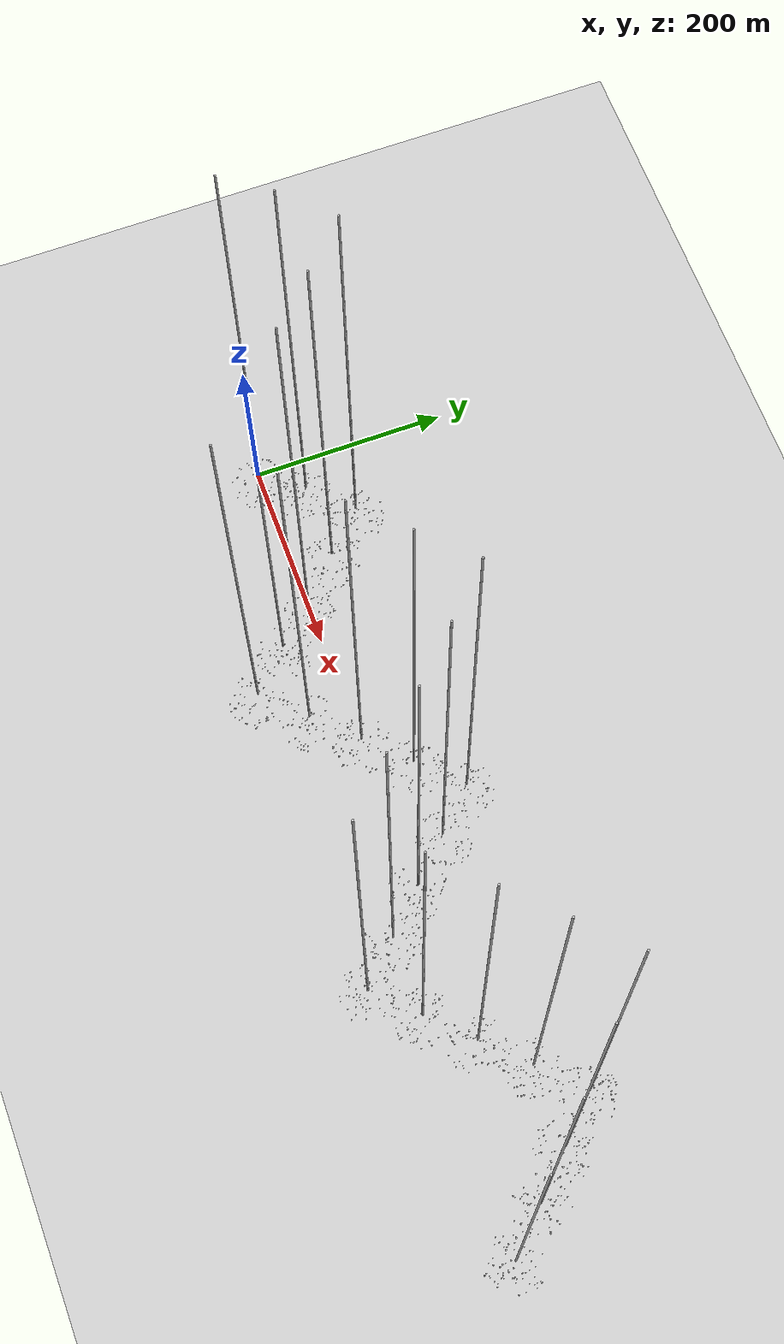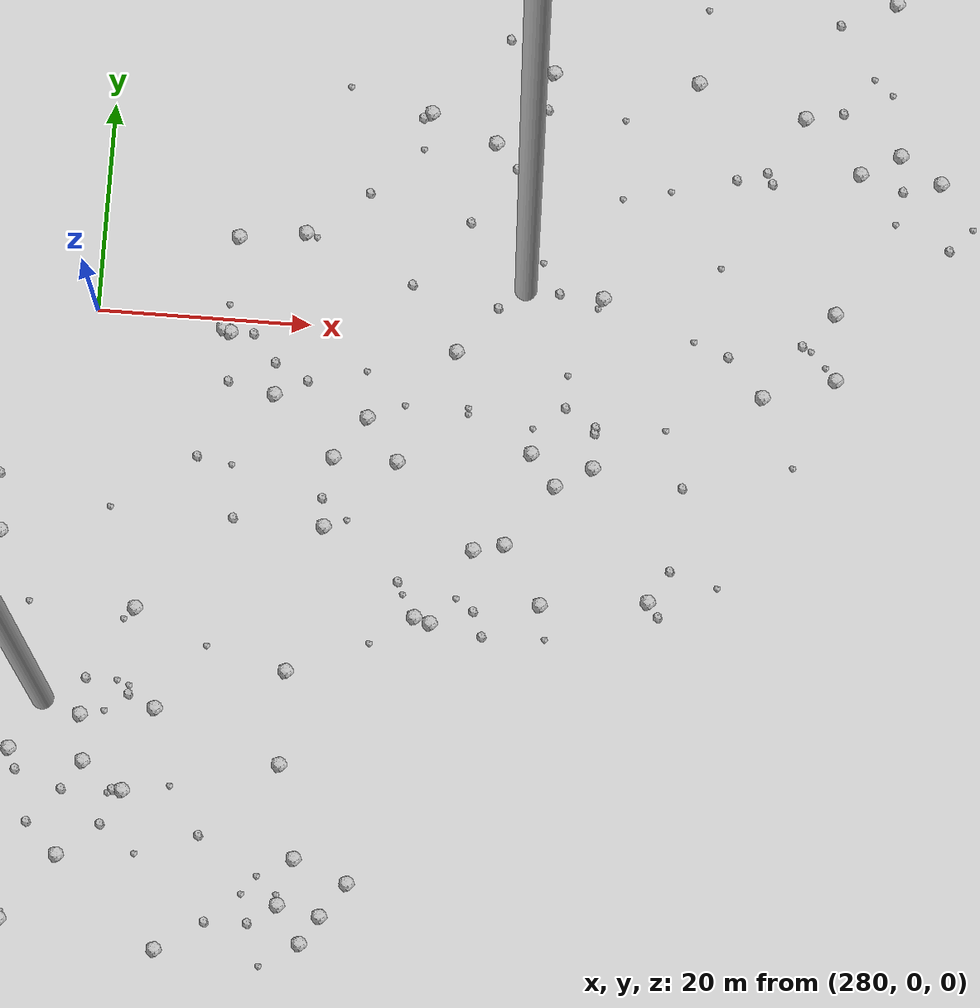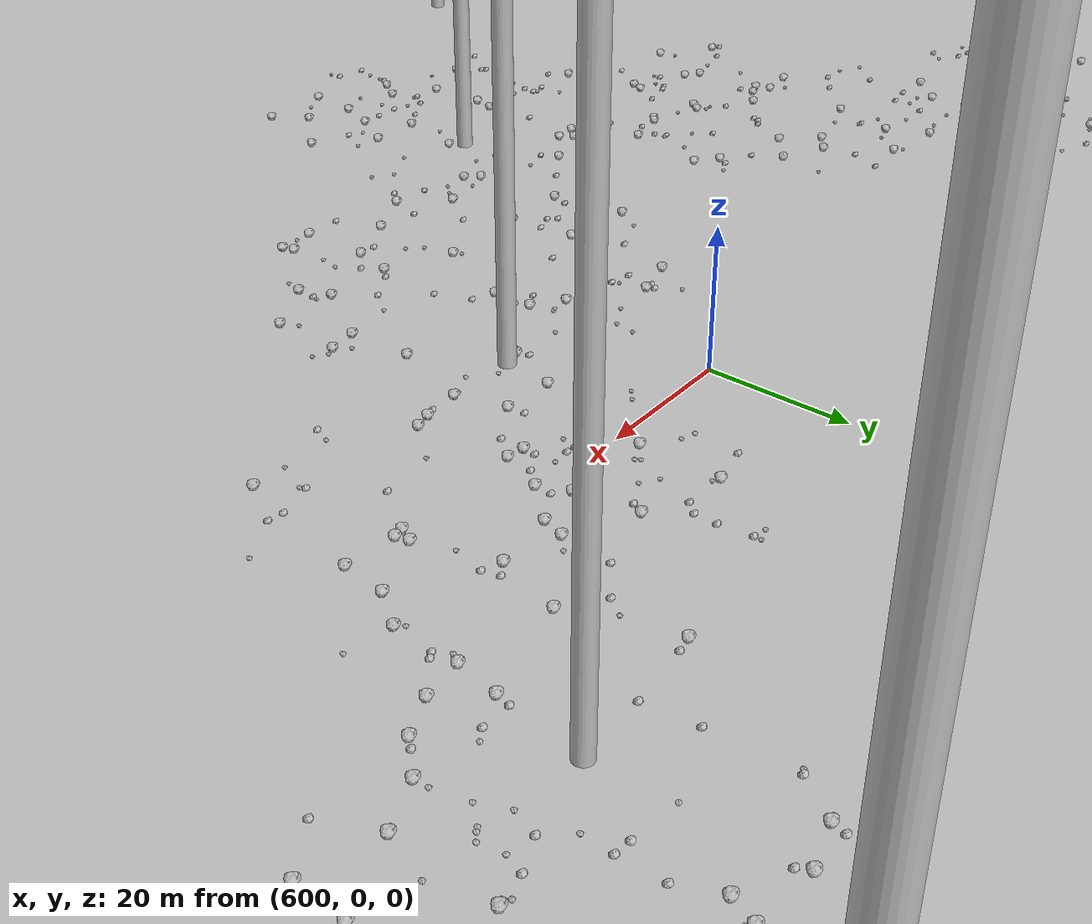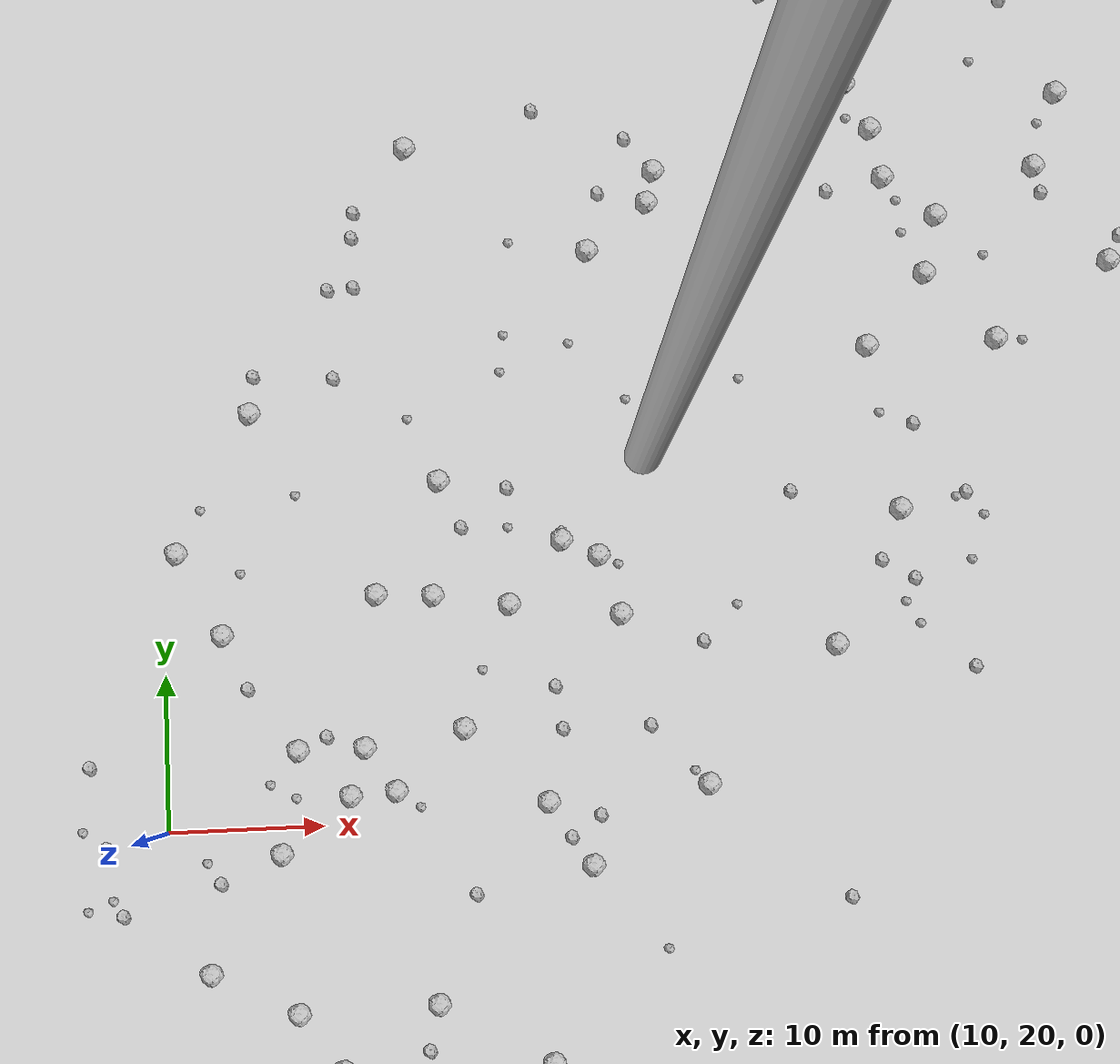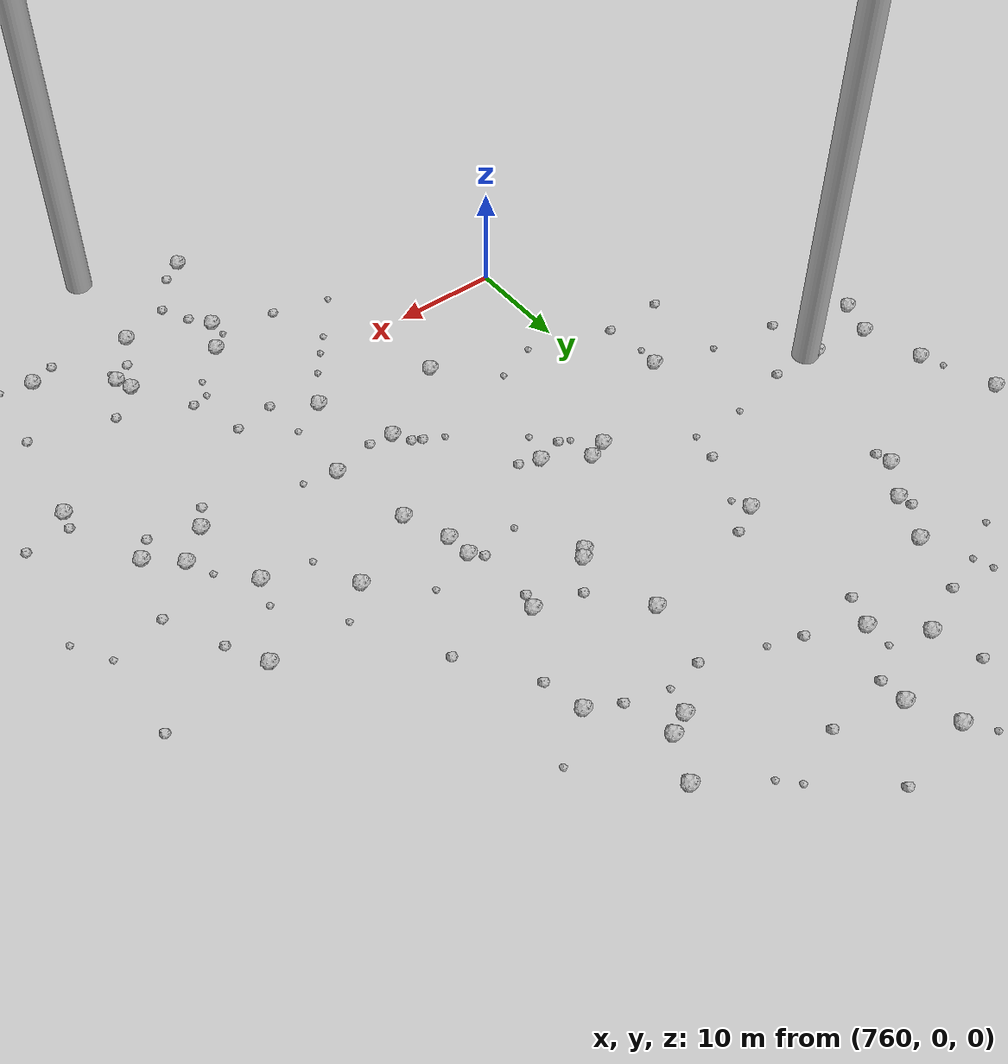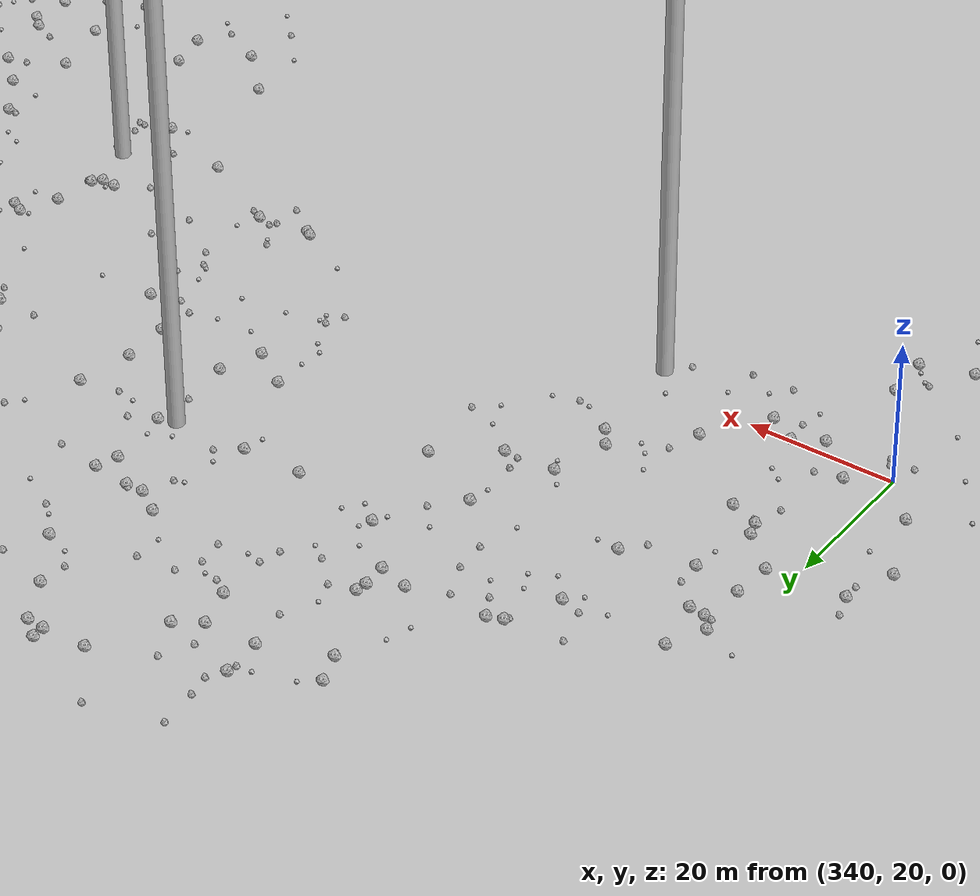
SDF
<sdf version="1.6">
 <world name="default">
  <include><uri>model://custom_ground</uri></include>
  <include><uri>model://sun</uri></include>
  <spherical_coordinates>
   <surface_model>EARTH_WGS84</surface_model>
   <latitude_deg>38.161479</latitude_deg>
   <longitude_deg>-122.454630</longitude_deg>
   <elevation>488.0</elevation>
   <heading_deg>90</heading_deg>
  </spherical_coordinates>
  <model name="rock1_0_0">
   <include><uri>model://rock1</uri><pose>-14.686883426534012 -5.121974331103381 0.5 0 0 0</pose></include>
  </model>
  <model name="rock1_0_1">
   <include><uri>model://rock1</uri><pose>18.44845788957044 24.84668019267062 0.5 0 0 0</pose></include>
  </model>
  <model name="rock1_0_2">
   <include><uri>model://rock1</uri><pose>22.723424589320345 24.84637767913226 0.5 0 0 0</pose></include>
  </model>
  <model name="rock1_0_3">
   <include><uri>model://rock1</uri><pose>18.385049536303285 -19.107027850705848 0.5 0 0 0</pose></include>
  </model>
  <model name="rock1_0_4">
   <include><uri>model://rock1</uri><pose>17.272927994177927 18.36429307804333 0.5 0 0 0</pose></include>
  </model>
  <model name="rock1_0_5">
   <include><uri>model://rock1</uri><pose>-12.898688267379745 -14.145573782720671 0.5 0 0 0</pose></include>
  </model>
  <model name="rock1_0_6">
   <include><uri>model://rock1</uri><pose>-10.859237089589636 17.574881942685394 0.5 0 0 0</pose></include>
  </model>
  <model name="rock1_0_7">
   <include><uri>model://rock1</uri><pose>-15.03161296842328 0.8191722254070122 0.5 0 0 0</pose></include>
  </model>
  <model name="rock1_0_8">
   <include><uri>model://rock1</uri><pose>12.646022537128836 11.09886134488469 0.5 0 0 0</pose></include>
  </model>
  <model name="rock1_0_9">
   <include><uri>model://rock1</uri><pose>23.723923990069487 -8.74464318667 0.5 0 0 0</pose></include>
  </model>
  <model name="rock1_0_10">
   <include><uri>model://rock1</uri><pose>-5.101441281046199 2.13738775532876 0.5 0 0 0</pose></include>
  </model>
  <model name="rock1_0_11">
   <include><uri>model://rock1</uri><pose>35.18490294055325 -4.400485530145023 0.5 0 0 0</pose></include>
  </model>
  <model name="rock1_0_12">
   <include><uri>model://rock1</uri><pose>34.188653660722046 -5.780355763638717 0.5 0 0 0</pose></include>
  </model>
  <model name="rock1_0_13">
   <include><uri>model://rock1</uri><pose>-9.15719178882611 -1.2442446593879524 0.5 0 0 0</pose></include>
  </model>
  <model name="rock1_0_14">
   <include><uri>model://rock1</uri><pose>5.428878922380235 -15.47611442327543 0.5 0 0 0</pose></include>
  </model>
  <model name="rock1_0_15">
   <include><uri>model://rock1</uri><pose>-12.807998798065247 15.963616218680102 0.5 0 0 0</pose></include>
  </model>
  <model name="rock1_0_16">
   <include><uri>model://rock1</uri><pose>28.1850645234086 -21.132892203986636 0.5 0 0 0</pose></include>
  </model>
  <model name="rock1_0_17">
   <include><uri>model://rock1</uri><pose>-11.066175104655095 -2.916529130183939 0.5 0 0 0</pose></include>
  </model>
  <model name="rock1_0_18">
   <include><uri>model://rock1</uri><pose>-5.068766604341533 -20.76686238187666 0.5 0 0 0</pose></include>
  </model>
  <model name="rock1_0_19">
   <include><uri>model://rock1</uri><pose>-6.077845796764308 20.574099110362774 0.5 0 0 0</pose></include>
  </model>
  <model name="rock1_0_20">
   <include><uri>model://rock1</uri><pose>-15.92588920117229 10.94150954879921 0.5 0 0 0</pose></include>
  </model>
  <model name="rock1_0_21">
   <include><uri>model://rock1</uri><pose>24.6003340826353 0.5965040615621184 0.5 0 0 0</pose></include>
  </model>
  <model name="rock1_0_22">
   <include><uri>model://rock1</uri><pose>33.10200444926732 3.606881371013337 0.5 0 0 0</pose></include>
  </model>
  <model name="rock1_0_23">
   <include><uri>model://rock1</uri><pose>18.105913490016697 8.44322066084181 0.5 0 0 0</pose></include>
  </model>
  <model name="rock1_0_24">
   <include><uri>model://rock1</uri><pose>33.954363821512835 4.792691685019037 0.5 0 0 0</pose></include>
  </model>
  <model name="rock1_0_25">
   <include><uri>model://rock1</uri><pose>20.774628095186067 4.866943027170464 0.5 0 0 0</pose></include>
  </model>
  <model name="rock1_0_26">
   <include><uri>model://rock1</uri><pose>26.904278136704406 8.684197022874685 0.5 0 0 0</pose></include>
  </model>
  <model name="rock2_0_0">
   <include><uri>model://rock2</uri><pose>26.19517962265713 5.828740338992645 0.3 0 0 0</pose></include>
  </model>
  <model name="rock2_0_1">
   <include><uri>model://rock2</uri><pose>5.6432172480243565 -11.431154947310329 0.3 0 0 0</pose></include>
  </model>
  <model name="rock2_0_2">
   <include><uri>model://rock2</uri><pose>15.287951338342523 28.8885248344194 0.3 0 0 0</pose></include>
  </model>
  <model name="rock2_0_3">
   <include><uri>model://rock2</uri><pose>27.266350797047508 -10.51954474120938 0.3 0 0 0</pose></include>
  </model>
  <model name="rock2_0_4">
   <include><uri>model://rock2</uri><pose>-5.216559491771749 -17.17220581488955 0.3 0 0 0</pose></include>
  </model>
  <model name="rock2_0_5">
   <include><uri>model://rock2</uri><pose>33.62130662885479 -14.942941511420447 0.3 0 0 0</pose></include>
  </model>
  <model name="rock2_0_6">
   <include><uri>model://rock2</uri><pose>29.491076786187953 15.356774064070429 0.3 0 0 0</pose></include>
  </model>
  <model name="rock2_0_7">
   <include><uri>model://rock2</uri><pose>39.010365961599256 -2.9380396803981377 0.3 0 0 0</pose></include>
  </model>
  <model name="rock2_0_8">
   <include><uri>model://rock2</uri><pose>-13.671278480627729 14.712906354892787 0.3 0 0 0</pose></include>
  </model>
  <model name="rock2_0_9">
   <include><uri>model://rock2</uri><pose>-2.558507230102922 -4.573843722872663 0.3 0 0 0</pose></include>
  </model>
  <model name="rock2_0_10">
   <include><uri>model://rock2</uri><pose>13.321585502002023 16.667461000000742 0.3 0 0 0</pose></include>
  </model>
  <model name="rock2_0_11">
   <include><uri>model://rock2</uri><pose>-3.205818590250143 15.524840774423247 0.3 0 0 0</pose></include>
  </model>
  <model name="rock2_0_12">
   <include><uri>model://rock2</uri><pose>32.01234685284783 -19.529843209027263 0.3 0 0 0</pose></include>
  </model>
  <model name="rock2_0_13">
   <include><uri>model://rock2</uri><pose>6.613916861757268 5.254394460918441 0.3 0 0 0</pose></include>
  </model>
  <model name="rock2_0_14">
   <include><uri>model://rock2</uri><pose>6.897182801944876 0.7778265092698184 0.3 0 0 0</pose></include>
  </model>
  <model name="rock2_0_15">
   <include><uri>model://rock2</uri><pose>14.881382020410761 -15.551248275708332 0.3 0 0 0</pose></include>
  </model>
  <model name="rock2_0_16">
   <include><uri>model://rock2</uri><pose>4.269196748945635 -15.816424115246193 0.3 0 0 0</pose></include>
  </model>
  <model name="rock2_0_17">
   <include><uri>model://rock2</uri><pose>7.0997190529504834 14.902067081411637 0.3 0 0 0</pose></include>
  </model>
  <model name="rock2_0_18">
   <include><uri>model://rock2</uri><pose>3.678059647779399 -14.586959060967569 0.3 0 0 0</pose></include>
  </model>
  <model name="rock2_0_19">
   <include><uri>model://rock2</uri><pose>20.276778931449662 25.639583338924623 0.3 0 0 0</pose></include>
  </model>
  <model name="rock2_0_20">
   <include><uri>model://rock2</uri><pose>0.8458467397211002 -15.072764444184905 0.3 0 0 0</pose></include>
  </model>
  <model name="rock2_0_21">
   <include><uri>model://rock2</uri><pose>12.260475872649323 -24.092908413220705 0.3 0 0 0</pose></include>
  </model>
  <model name="rock2_0_22">
   <include><uri>model://rock2</uri><pose>6.080677228420676 19.174088784017464 0.3 0 0 0</pose></include>
  </model>
  <model name="rock2_0_23">
   <include><uri>model://rock2</uri><pose>27.98559321421935 -11.829514530653725 0.3 0 0 0</pose></include>
  </model>
  <model name="rock2_0_24">
   <include><uri>model://rock2</uri><pose>17.397577481205943 -28.00283076915495 0.3 0 0 0</pose></include>
  </model>
  <model name="rock2_0_25">
   <include><uri>model://rock2</uri><pose>-11.52228017078977 6.1297204114515225 0.3 0 0 0</pose></include>
  </model>
  <model name="rock2_0_26">
   <include><uri>model://rock2</uri><pose>5.075450308498912 24.305940433753378 0.3 0 0 0</pose></include>
  </model>
  <model name="rock3_0_0">
   <include><uri>model://rock3</uri><pose>18.18725993649322 21.811939968821136 0.2 0 0 0</pose></include>
  </model>
  <model name="rock3_0_1">
   <include><uri>model://rock3</uri><pose>4.530480587117491 20.228970711086568 0.2 0 0 0</pose></include>
  </model>
  <model name="rock3_0_2">
   <include><uri>model://rock3</uri><pose>2.6205557790576215 -28.468492149981472 0.2 0 0 0</pose></include>
  </model>
  <model name="rock3_0_3">
   <include><uri>model://rock3</uri><pose>15.220146482534545 -10.676021506731018 0.2 0 0 0</pose></include>
  </model>
  <model name="rock3_0_4">
   <include><uri>model://rock3</uri><pose>-17.39105779597183 -5.837277256333195 0.2 0 0 0</pose></include>
  </model>
  <model name="rock3_0_5">
   <include><uri>model://rock3</uri><pose>-7.582317349411625 -0.232962474257274 0.2 0 0 0</pose></include>
  </model>
  <model name="rock3_0_6">
   <include><uri>model://rock3</uri><pose>13.103556903544664 -23.298954739088654 0.2 0 0 0</pose></include>
  </model>
  <model name="rock3_0_7">
   <include><uri>model://rock3</uri><pose>33.726139004685166 4.257296067754311 0.2 0 0 0</pose></include>
  </model>
  <model name="rock3_0_8">
   <include><uri>model://rock3</uri><pose>26.11473723362176 20.932834789684968 0.2 0 0 0</pose></include>
  </model>
  <model name="rock3_0_9">
   <include><uri>model://rock3</uri><pose>-3.0082891230609796 5.002453646325783 0.2 0 0 0</pose></include>
  </model>
  <model name="rock3_0_10">
   <include><uri>model://rock3</uri><pose>6.427068403908333 15.853623360443443 0.2 0 0 0</pose></include>
  </model>
  <model name="rock3_0_11">
   <include><uri>model://rock3</uri><pose>21.08297121034908 -25.0695684193497 0.2 0 0 0</pose></include>
  </model>
  <model name="rock3_0_12">
   <include><uri>model://rock3</uri><pose>-13.144017169455726 17.365732053875355 0.2 0 0 0</pose></include>
  </model>
  <model name="rock3_0_13">
   <include><uri>model://rock3</uri><pose>-1.638059972101857 -7.410896145408522 0.2 0 0 0</pose></include>
  </model>
  <model name="rock3_0_14">
   <include><uri>model://rock3</uri><pose>38.69272568033942 1.7345886323300483 0.2 0 0 0</pose></include>
  </model>
  <model name="rock3_0_15">
   <include><uri>model://rock3</uri><pose>-12.93714878698342 -8.692058098402057 0.2 0 0 0</pose></include>
  </model>
  <model name="rock3_0_16">
   <include><uri>model://rock3</uri><pose>4.8299276795263 15.240588604109497 0.2 0 0 0</pose></include>
  </model>
  <model name="rock3_0_17">
   <include><uri>model://rock3</uri><pose>-14.720552662689002 -15.313454968967552 0.2 0 0 0</pose></include>
  </model>
  <model name="rock3_0_18">
   <include><uri>model://rock3</uri><pose>2.2452894183503602 -15.900616237276948 0.2 0 0 0</pose></include>
  </model>
  <model name="rock3_0_19">
   <include><uri>model://rock3</uri><pose>17.31302321139475 -27.509959085218625 0.2 0 0 0</pose></include>
  </model>
  <model name="rock3_0_20">
   <include><uri>model://rock3</uri><pose>7.04676081903952 -24.93426742208191 0.2 0 0 0</pose></include>
  </model>
  <model name="rock3_0_21">
   <include><uri>model://rock3</uri><pose>12.436365555333907 17.97023671017959 0.2 0 0 0</pose></include>
  </model>
  <model name="rock3_0_22">
   <include><uri>model://rock3</uri><pose>26.28193562634454 -1.1693802535200888 0.2 0 0 0</pose></include>
  </model>
  <model name="rock3_0_23">
   <include><uri>model://rock3</uri><pose>9.98470837106347 -19.49167798233952 0.2 0 0 0</pose></include>
  </model>
  <model name="rock3_0_24">
   <include><uri>model://rock3</uri><pose>-1.8604686683837741 -27.272686790910868 0.2 0 0 0</pose></include>
  </model>
  <model name="rock3_0_25">
   <include><uri>model://rock3</uri><pose>34.96271251589837 -7.536459288131802 0.2 0 0 0</pose></include>
  </model>
  <model name="rock3_0_26">
   <include><uri>model://rock3</uri><pose>3.643171794103935 -16.844324681988006 0.2 0 0 0</pose></include>
  </model>
  <model name="rock1_1_0">
   <include><uri>model://rock1</uri><pose>42.47248235215038 59.82001834245835 0.5 0 0 0</pose></include>
  </model>
  <model name="rock1_1_1">
   <include><uri>model://rock1</uri><pose>58.20562522115904 60.87452309257886 0.5 0 0 0</pose></include>
  </model>
  <model name="rock1_1_2">
   <include><uri>model://rock1</uri><pose>32.31155257351733 33.62877996591534 0.5 0 0 0</pose></include>
  </model>
  <model name="rock1_1_3">
   <include><uri>model://rock1</uri><pose>26.579669740979583 64.18422528232745 0.5 0 0 0</pose></include>
  </model>
  <model name="rock1_1_4">
   <include><uri>model://rock1</uri><pose>23.74096207003068 34.60573267121204 0.5 0 0 0</pose></include>
  </model>
  <model name="rock1_1_5">
   <include><uri>model://rock1</uri><pose>28.02591993437091 41.826675687463386 0.5 0 0 0</pose></include>
  </model>
  <model name="rock1_1_6">
   <include><uri>model://rock1</uri><pose>56.47259338205611 49.56225245486903 0.5 0 0 0</pose></include>
  </model>
  <model name="rock1_1_7">
   <include><uri>model://rock1</uri><pose>29.1297704470631 25.810796552284252 0.5 0 0 0</pose></include>
  </model>
  <model name="rock1_1_8">
   <include><uri>model://rock1</uri><pose>21.742710002203644 21.83855696503018 0.5 0 0 0</pose></include>
  </model>
  <model name="rock1_1_9">
   <include><uri>model://rock1</uri><pose>10.91587166317845 37.78765306510189 0.5 0 0 0</pose></include>
  </model>
  <model name="rock1_1_10">
   <include><uri>model://rock1</uri><pose>24.656742990255303 22.044931383381872 0.5 0 0 0</pose></include>
  </model>
  <model name="rock1_1_11">
   <include><uri>model://rock1</uri><pose>57.957066539165965 38.745329876611734 0.5 0 0 0</pose></include>
  </model>
  <model name="rock1_1_12">
   <include><uri>model://rock1</uri><pose>38.38201475295759 56.717256039393234 0.5 0 0 0</pose></include>
  </model>
  <model name="rock1_1_13">
   <include><uri>model://rock1</uri><pose>15.859259197390186 46.769031838803905 0.5 0 0 0</pose></include>
  </model>
  <model name="rock1_1_14">
   <include><uri>model://rock1</uri><pose>44.60341494397061 21.667997483608186 0.5 0 0 0</pose></include>
  </model>
  <model name="rock1_1_15">
   <include><uri>model://rock1</uri><pose>64.95700778418103 49.703396256830736 0.5 0 0 0</pose></include>
  </model>
  <model name="rock1_1_16">
   <include><uri>model://rock1</uri><pose>43.02240320484526 61.95490414888829 0.5 0 0 0</pose></include>
  </model>
  <model name="rock1_1_17">
   <include><uri>model://rock1</uri><pose>53.28676446832574 30.161447191040402 0.5 0 0 0</pose></include>
  </model>
  <model name="rock1_1_18">
   <include><uri>model://rock1</uri><pose>38.23009486371121 36.56340887892414 0.5 0 0 0</pose></include>
  </model>
  <model name="rock1_1_19">
   <include><uri>model://rock1</uri><pose>36.98944903116025 16.879367251523067 0.5 0 0 0</pose></include>
  </model>
  <model name="rock1_1_20">
   <include><uri>model://rock1</uri><pose>35.859769395585744 37.64572173587766 0.5 0 0 0</pose></include>
  </model>
  <model name="rock1_1_21">
   <include><uri>model://rock1</uri><pose>60.55311667194196 54.272857599692635 0.5 0 0 0</pose></include>
  </model>
  <model name="rock1_1_22">
   <include><uri>model://rock1</uri><pose>13.775493482308015 32.383425931144906 0.5 0 0 0</pose></include>
  </model>
  <model name="rock1_1_23">
   <include><uri>model://rock1</uri><pose>27.415231393533933 34.401236551044505 0.5 0 0 0</pose></include>
  </model>
  <model name="rock1_1_24">
   <include><uri>model://rock1</uri><pose>39.50173395554065 32.70476468046292 0.5 0 0 0</pose></include>
  </model>
  <model name="rock1_1_25">
   <include><uri>model://rock1</uri><pose>61.539943262024906 58.132683724934445 0.5 0 0 0</pose></include>
  </model>
  <model name="rock1_1_26">
   <include><uri>model://rock1</uri><pose>34.31526253404368 20.945281981841656 0.5 0 0 0</pose></include>
  </model>
  <model name="rock2_1_0">
   <include><uri>model://rock2</uri><pose>21.36250304464757 48.915425335418185 0.3 0 0 0</pose></include>
  </model>
  <model name="rock2_1_1">
   <include><uri>model://rock2</uri><pose>59.16945996651576 44.325149052605305 0.3 0 0 0</pose></include>
  </model>
  <model name="rock2_1_2">
   <include><uri>model://rock2</uri><pose>62.14071745198724 28.36525250459587 0.3 0 0 0</pose></include>
  </model>
  <model name="rock2_1_3">
   <include><uri>model://rock2</uri><pose>37.60222707662666 19.969462230474505 0.3 0 0 0</pose></include>
  </model>
  <model name="rock2_1_4">
   <include><uri>model://rock2</uri><pose>16.130937079022942 49.23562391129496 0.3 0 0 0</pose></include>
  </model>
  <model name="rock2_1_5">
   <include><uri>model://rock2</uri><pose>44.72782062672796 30.7348983290521 0.3 0 0 0</pose></include>
  </model>
  <model name="rock2_1_6">
   <include><uri>model://rock2</uri><pose>54.415586204260585 60.133470413363824 0.3 0 0 0</pose></include>
  </model>
  <model name="rock2_1_7">
   <include><uri>model://rock2</uri><pose>56.5399685738618 35.47336754063939 0.3 0 0 0</pose></include>
  </model>
  <model name="rock2_1_8">
   <include><uri>model://rock2</uri><pose>23.01112443276978 59.98880150503025 0.3 0 0 0</pose></include>
  </model>
  <model name="rock2_1_9">
   <include><uri>model://rock2</uri><pose>62.28466361082526 39.67074648153819 0.3 0 0 0</pose></include>
  </model>
  <model name="rock2_1_10">
   <include><uri>model://rock2</uri><pose>58.62280471832751 34.20168914744148 0.3 0 0 0</pose></include>
  </model>
  <model name="rock2_1_11">
   <include><uri>model://rock2</uri><pose>29.370178676502327 38.74575260517103 0.3 0 0 0</pose></include>
  </model>
  <model name="rock2_1_12">
   <include><uri>model://rock2</uri><pose>39.25587794465294 60.62859456883788 0.3 0 0 0</pose></include>
  </model>
  <model name="rock2_1_13">
   <include><uri>model://rock2</uri><pose>41.06034193025939 25.499512500699275 0.3 0 0 0</pose></include>
  </model>
  <model name="rock2_1_14">
   <include><uri>model://rock2</uri><pose>22.867972530215447 54.94582028537812 0.3 0 0 0</pose></include>
  </model>
  <model name="rock2_1_15">
   <include><uri>model://rock2</uri><pose>35.896460043436875 38.09653047992003 0.3 0 0 0</pose></include>
  </model>
  <model name="rock2_1_16">
   <include><uri>model://rock2</uri><pose>32.41562199253986 41.20648158407357 0.3 0 0 0</pose></include>
  </model>
  <model name="rock2_1_17">
   <include><uri>model://rock2</uri><pose>41.18869421718764 64.28077958823543 0.3 0 0 0</pose></include>
  </model>
  <model name="rock2_1_18">
   <include><uri>model://rock2</uri><pose>35.10270894816795 66.46242960454178 0.3 0 0 0</pose></include>
  </model>
  <model name="rock2_1_19">
   <include><uri>model://rock2</uri><pose>53.254741094030614 14.174448873698477 0.3 0 0 0</pose></include>
  </model>
  <model name="rock2_1_20">
   <include><uri>model://rock2</uri><pose>35.41627844112701 25.525870588023015 0.3 0 0 0</pose></include>
  </model>
  <model name="rock2_1_21">
   <include><uri>model://rock2</uri><pose>44.58577262231437 49.983733005451384 0.3 0 0 0</pose></include>
  </model>
  <model name="rock2_1_22">
   <include><uri>model://rock2</uri><pose>22.843278133808184 58.29958277689246 0.3 0 0 0</pose></include>
  </model>
  <model name="rock2_1_23">
   <include><uri>model://rock2</uri><pose>50.89258137743171 40.18917243012962 0.3 0 0 0</pose></include>
  </model>
  <model name="rock2_1_24">
   <include><uri>model://rock2</uri><pose>35.69350775175258 18.64970174382814 0.3 0 0 0</pose></include>
  </model>
  <model name="rock2_1_25">
   <include><uri>model://rock2</uri><pose>21.15689139277563 54.829737211359976 0.3 0 0 0</pose></include>
  </model>
  <model name="rock2_1_26">
   <include><uri>model://rock2</uri><pose>35.05135895670461 28.2382458676876 0.3 0 0 0</pose></include>
  </model>
  <model name="rock3_1_0">
   <include><uri>model://rock3</uri><pose>57.921732082280734 32.7092111634429 0.2 0 0 0</pose></include>
  </model>
  <model name="rock3_1_1">
   <include><uri>model://rock3</uri><pose>32.376371005603545 38.616359372491324 0.2 0 0 0</pose></include>
  </model>
  <model name="rock3_1_2">
   <include><uri>model://rock3</uri><pose>39.438978329944476 35.94016881911908 0.2 0 0 0</pose></include>
  </model>
  <model name="rock3_1_3">
   <include><uri>model://rock3</uri><pose>30.38113782020159 29.476333413128526 0.2 0 0 0</pose></include>
  </model>
  <model name="rock3_1_4">
   <include><uri>model://rock3</uri><pose>66.72621931950455 49.57010915950152 0.2 0 0 0</pose></include>
  </model>
  <model name="rock3_1_5">
   <include><uri>model://rock3</uri><pose>47.00113649325984 33.00104434421999 0.2 0 0 0</pose></include>
  </model>
  <model name="rock3_1_6">
   <include><uri>model://rock3</uri><pose>14.948048729302181 36.32394588207586 0.2 0 0 0</pose></include>
  </model>
  <model name="rock3_1_7">
   <include><uri>model://rock3</uri><pose>41.46779521874819 11.443384145235296 0.2 0 0 0</pose></include>
  </model>
  <model name="rock3_1_8">
   <include><uri>model://rock3</uri><pose>63.3643699079244 38.15378525134342 0.2 0 0 0</pose></include>
  </model>
  <model name="rock3_1_9">
   <include><uri>model://rock3</uri><pose>62.38421003682838 35.25591906546089 0.2 0 0 0</pose></include>
  </model>
  <model name="rock3_1_10">
   <include><uri>model://rock3</uri><pose>26.09532793729262 46.01677133603944 0.2 0 0 0</pose></include>
  </model>
  <model name="rock3_1_11">
   <include><uri>model://rock3</uri><pose>42.58150097909175 44.219760340385534 0.2 0 0 0</pose></include>
  </model>
  <model name="rock3_1_12">
   <include><uri>model://rock3</uri><pose>47.9094516616373 47.77204719836833 0.2 0 0 0</pose></include>
  </model>
  <model name="rock3_1_13">
   <include><uri>model://rock3</uri><pose>12.435929428800748 40.56606132920085 0.2 0 0 0</pose></include>
  </model>
  <model name="rock3_1_14">
   <include><uri>model://rock3</uri><pose>33.192628973742174 57.530681363261714 0.2 0 0 0</pose></include>
  </model>
  <model name="rock3_1_15">
   <include><uri>model://rock3</uri><pose>16.55902029971661 22.72302925009316 0.2 0 0 0</pose></include>
  </model>
  <model name="rock3_1_16">
   <include><uri>model://rock3</uri><pose>18.64046061920346 41.287515358723724 0.2 0 0 0</pose></include>
  </model>
  <model name="rock3_1_17">
   <include><uri>model://rock3</uri><pose>58.77792826303138 31.262056179474715 0.2 0 0 0</pose></include>
  </model>
  <model name="rock3_1_18">
   <include><uri>model://rock3</uri><pose>36.8596326470433 50.60287804413587 0.2 0 0 0</pose></include>
  </model>
  <model name="rock3_1_19">
   <include><uri>model://rock3</uri><pose>40.4320413720522 46.731360488958394 0.2 0 0 0</pose></include>
  </model>
  <model name="rock3_1_20">
   <include><uri>model://rock3</uri><pose>61.64477513235472 39.39788259401226 0.2 0 0 0</pose></include>
  </model>
  <model name="rock3_1_21">
   <include><uri>model://rock3</uri><pose>59.235696276180754 57.12023848820233 0.2 0 0 0</pose></include>
  </model>
  <model name="rock3_1_22">
   <include><uri>model://rock3</uri><pose>43.15362684273781 47.96320484863871 0.2 0 0 0</pose></include>
  </model>
  <model name="rock3_1_23">
   <include><uri>model://rock3</uri><pose>43.72501063339669 22.50057117458541 0.2 0 0 0</pose></include>
  </model>
  <model name="rock3_1_24">
   <include><uri>model://rock3</uri><pose>32.26494253700616 48.88532305141149 0.2 0 0 0</pose></include>
  </model>
  <model name="rock3_1_25">
   <include><uri>model://rock3</uri><pose>56.998477962089915 45.12543780944303 0.2 0 0 0</pose></include>
  </model>
  <model name="rock3_1_26">
   <include><uri>model://rock3</uri><pose>32.589839631641276 51.332157955491255 0.2 0 0 0</pose></include>
  </model>
  <model name="rock1_2_0">
   <include><uri>model://rock1</uri><pose>80.59888050926759 75.55166808113412 0.5 0 0 0</pose></include>
  </model>
  <model name="rock1_2_1">
   <include><uri>model://rock1</uri><pose>56.060816199422376 67.3701398656433 0.5 0 0 0</pose></include>
  </model>
  <model name="rock1_2_2">
   <include><uri>model://rock1</uri><pose>80.49342930741119 93.84374516792019 0.5 0 0 0</pose></include>
  </model>
  <model name="rock1_2_3">
   <include><uri>model://rock1</uri><pose>55.27727268398097 84.42011350694267 0.5 0 0 0</pose></include>
  </model>
  <model name="rock1_2_4">
   <include><uri>model://rock1</uri><pose>90.39509680782365 90.8659624980422 0.5 0 0 0</pose></include>
  </model>
  <model name="rock1_2_5">
   <include><uri>model://rock1</uri><pose>62.94745384262303 82.97364119139667 0.5 0 0 0</pose></include>
  </model>
  <model name="rock1_2_6">
   <include><uri>model://rock1</uri><pose>57.3814698095694 82.41438992375171 0.5 0 0 0</pose></include>
  </model>
  <model name="rock1_2_7">
   <include><uri>model://rock1</uri><pose>77.96803586140736 69.46440965203716 0.5 0 0 0</pose></include>
  </model>
  <model name="rock1_2_8">
   <include><uri>model://rock1</uri><pose>72.73122669003396 54.600709179968085 0.5 0 0 0</pose></include>
  </model>
  <model name="rock1_2_9">
   <include><uri>model://rock1</uri><pose>90.3141365224172 93.04156135361384 0.5 0 0 0</pose></include>
  </model>
  <model name="rock1_2_10">
   <include><uri>model://rock1</uri><pose>108.02399680024936 73.17850316733966 0.5 0 0 0</pose></include>
  </model>
  <model name="rock1_2_11">
   <include><uri>model://rock1</uri><pose>79.64466154681617 98.84700552971867 0.5 0 0 0</pose></include>
  </model>
  <model name="rock1_2_12">
   <include><uri>model://rock1</uri><pose>55.08856714559602 95.37716180290582 0.5 0 0 0</pose></include>
  </model>
  <model name="rock1_2_13">
   <include><uri>model://rock1</uri><pose>73.12068293120802 109.13173136892769 0.5 0 0 0</pose></include>
  </model>
  <model name="rock1_2_14">
   <include><uri>model://rock1</uri><pose>65.03170989536284 99.28426635516887 0.5 0 0 0</pose></include>
  </model>
  <model name="rock1_2_15">
   <include><uri>model://rock1</uri><pose>93.66847268436976 103.9991035941991 0.5 0 0 0</pose></include>
  </model>
  <model name="rock1_2_16">
   <include><uri>model://rock1</uri><pose>57.58772057380575 64.20934967434091 0.5 0 0 0</pose></include>
  </model>
  <model name="rock1_2_17">
   <include><uri>model://rock1</uri><pose>70.09028002689709 66.16140277025042 0.5 0 0 0</pose></include>
  </model>
  <model name="rock1_2_18">
   <include><uri>model://rock1</uri><pose>68.27410757390953 61.1940309241252 0.5 0 0 0</pose></include>
  </model>
  <model name="rock1_2_19">
   <include><uri>model://rock1</uri><pose>105.44958836157525 95.07659123153255 0.5 0 0 0</pose></include>
  </model>
  <model name="rock1_2_20">
   <include><uri>model://rock1</uri><pose>88.27032750591391 64.10590146704185 0.5 0 0 0</pose></include>
  </model>
  <model name="rock1_2_21">
   <include><uri>model://rock1</uri><pose>101.61830412484483 89.21755696507965 0.5 0 0 0</pose></include>
  </model>
  <model name="rock1_2_22">
   <include><uri>model://rock1</uri><pose>50.82277298226891 74.01806122158956 0.5 0 0 0</pose></include>
  </model>
  <model name="rock1_2_23">
   <include><uri>model://rock1</uri><pose>94.29861614736743 75.8158573705714 0.5 0 0 0</pose></include>
  </model>
  <model name="rock1_2_24">
   <include><uri>model://rock1</uri><pose>66.40514213461454 97.1475385356363 0.5 0 0 0</pose></include>
  </model>
  <model name="rock1_2_25">
   <include><uri>model://rock1</uri><pose>83.42391510862572 106.81547122000984 0.5 0 0 0</pose></include>
  </model>
  <model name="rock1_2_26">
   <include><uri>model://rock1</uri><pose>65.87942850001502 81.89929395738226 0.5 0 0 0</pose></include>
  </model>
  <model name="rock2_2_0">
   <include><uri>model://rock2</uri><pose>81.10683462499215 68.45461641150776 0.3 0 0 0</pose></include>
  </model>
  <model name="rock2_2_1">
   <include><uri>model://rock2</uri><pose>72.21401580340734 73.92722866683602 0.3 0 0 0</pose></include>
  </model>
  <model name="rock2_2_2">
   <include><uri>model://rock2</uri><pose>57.09771333603156 75.52251820303933 0.3 0 0 0</pose></include>
  </model>
  <model name="rock2_2_3">
   <include><uri>model://rock2</uri><pose>80.94631105246494 88.70725500826492 0.3 0 0 0</pose></include>
  </model>
  <model name="rock2_2_4">
   <include><uri>model://rock2</uri><pose>74.73056764302062 79.43771295707931 0.3 0 0 0</pose></include>
  </model>
  <model name="rock2_2_5">
   <include><uri>model://rock2</uri><pose>70.25403775171291 76.58437703200441 0.3 0 0 0</pose></include>
  </model>
  <model name="rock2_2_6">
   <include><uri>model://rock2</uri><pose>66.85547246043494 72.83300300966732 0.3 0 0 0</pose></include>
  </model>
  <model name="rock2_2_7">
   <include><uri>model://rock2</uri><pose>80.9196930959802 56.57709624943462 0.3 0 0 0</pose></include>
  </model>
  <model name="rock2_2_8">
   <include><uri>model://rock2</uri><pose>76.26939324905199 80.32838080157532 0.3 0 0 0</pose></include>
  </model>
  <model name="rock2_2_9">
   <include><uri>model://rock2</uri><pose>84.73530425042526 76.28907353267228 0.3 0 0 0</pose></include>
  </model>
  <model name="rock2_2_10">
   <include><uri>model://rock2</uri><pose>75.66732921740376 92.73465878896064 0.3 0 0 0</pose></include>
  </model>
  <model name="rock2_2_11">
   <include><uri>model://rock2</uri><pose>68.66407350348301 59.43377152535197 0.3 0 0 0</pose></include>
  </model>
  <model name="rock2_2_12">
   <include><uri>model://rock2</uri><pose>85.36455745105958 71.79551956012675 0.3 0 0 0</pose></include>
  </model>
  <model name="rock2_2_13">
   <include><uri>model://rock2</uri><pose>106.01084302191917 70.94040066083409 0.3 0 0 0</pose></include>
  </model>
  <model name="rock2_2_14">
   <include><uri>model://rock2</uri><pose>86.97617734096015 72.50590424697033 0.3 0 0 0</pose></include>
  </model>
  <model name="rock2_2_15">
   <include><uri>model://rock2</uri><pose>92.48593585599924 97.72757278553429 0.3 0 0 0</pose></include>
  </model>
  <model name="rock2_2_16">
   <include><uri>model://rock2</uri><pose>82.39405682343141 57.7310075296001 0.3 0 0 0</pose></include>
  </model>
  <model name="rock2_2_17">
   <include><uri>model://rock2</uri><pose>74.97938949679514 90.74565474960299 0.3 0 0 0</pose></include>
  </model>
  <model name="rock2_2_18">
   <include><uri>model://rock2</uri><pose>56.35800322850774 72.8619815050904 0.3 0 0 0</pose></include>
  </model>
  <model name="rock2_2_19">
   <include><uri>model://rock2</uri><pose>101.58975689270437 63.432411167476644 0.3 0 0 0</pose></include>
  </model>
  <model name="rock2_2_20">
   <include><uri>model://rock2</uri><pose>86.20324782906523 107.47866934940473 0.3 0 0 0</pose></include>
  </model>
  <model name="rock2_2_21">
   <include><uri>model://rock2</uri><pose>97.28756172739276 101.7413040070762 0.3 0 0 0</pose></include>
  </model>
  <model name="rock2_2_22">
   <include><uri>model://rock2</uri><pose>72.2145428048592 83.06549848506324 0.3 0 0 0</pose></include>
  </model>
  <model name="rock2_2_23">
   <include><uri>model://rock2</uri><pose>67.03358819184714 86.57119181917112 0.3 0 0 0</pose></include>
  </model>
  <model name="rock2_2_24">
   <include><uri>model://rock2</uri><pose>96.91603463179928 97.94933320763525 0.3 0 0 0</pose></include>
  </model>
  <model name="rock2_2_25">
   <include><uri>model://rock2</uri><pose>56.13293935393334 74.4808542516161 0.3 0 0 0</pose></include>
  </model>
  <model name="rock2_2_26">
   <include><uri>model://rock2</uri><pose>73.62263085185681 56.298747824342655 0.3 0 0 0</pose></include>
  </model>
  <model name="rock3_2_0">
   <include><uri>model://rock3</uri><pose>83.22290003280142 77.50389073037354 0.2 0 0 0</pose></include>
  </model>
  <model name="rock3_2_1">
   <include><uri>model://rock3</uri><pose>84.20574883825356 58.289001461167175 0.2 0 0 0</pose></include>
  </model>
  <model name="rock3_2_2">
   <include><uri>model://rock3</uri><pose>73.1912226040447 84.59759008009107 0.2 0 0 0</pose></include>
  </model>
  <model name="rock3_2_3">
   <include><uri>model://rock3</uri><pose>82.18755313894539 80.78345729981093 0.2 0 0 0</pose></include>
  </model>
  <model name="rock3_2_4">
   <include><uri>model://rock3</uri><pose>100.74070124622102 82.67249363953735 0.2 0 0 0</pose></include>
  </model>
  <model name="rock3_2_5">
   <include><uri>model://rock3</uri><pose>68.78931979795877 64.18139179042446 0.2 0 0 0</pose></include>
  </model>
  <model name="rock3_2_6">
   <include><uri>model://rock3</uri><pose>56.05709984699025 65.06567095828402 0.2 0 0 0</pose></include>
  </model>
  <model name="rock3_2_7">
   <include><uri>model://rock3</uri><pose>79.18433690724557 54.77894642993743 0.2 0 0 0</pose></include>
  </model>
  <model name="rock3_2_8">
   <include><uri>model://rock3</uri><pose>67.7390660864393 92.54982331687387 0.2 0 0 0</pose></include>
  </model>
  <model name="rock3_2_9">
   <include><uri>model://rock3</uri><pose>88.32696982923972 103.14058155484118 0.2 0 0 0</pose></include>
  </model>
  <model name="rock3_2_10">
   <include><uri>model://rock3</uri><pose>64.55216224369308 55.37198086713214 0.2 0 0 0</pose></include>
  </model>
  <model name="rock3_2_11">
   <include><uri>model://rock3</uri><pose>50.990771527582226 82.32109529540031 0.2 0 0 0</pose></include>
  </model>
  <model name="rock3_2_12">
   <include><uri>model://rock3</uri><pose>73.62504257263166 89.48682103107566 0.2 0 0 0</pose></include>
  </model>
  <model name="rock3_2_13">
   <include><uri>model://rock3</uri><pose>64.54663925356671 68.65003947257715 0.2 0 0 0</pose></include>
  </model>
  <model name="rock3_2_14">
   <include><uri>model://rock3</uri><pose>55.42263587540999 93.0259154418876 0.2 0 0 0</pose></include>
  </model>
  <model name="rock3_2_15">
   <include><uri>model://rock3</uri><pose>89.40980174560741 99.67420902222506 0.2 0 0 0</pose></include>
  </model>
  <model name="rock3_2_16">
   <include><uri>model://rock3</uri><pose>66.19051346882287 88.56348047580875 0.2 0 0 0</pose></include>
  </model>
  <model name="rock3_2_17">
   <include><uri>model://rock3</uri><pose>67.81072932503432 82.23287230491376 0.2 0 0 0</pose></include>
  </model>
  <model name="rock3_2_18">
   <include><uri>model://rock3</uri><pose>94.68670068291688 66.35884406938433 0.2 0 0 0</pose></include>
  </model>
  <model name="rock3_2_19">
   <include><uri>model://rock3</uri><pose>59.0259229299305 59.305843155249214 0.2 0 0 0</pose></include>
  </model>
  <model name="rock3_2_20">
   <include><uri>model://rock3</uri><pose>56.58920415520136 90.75479510679355 0.2 0 0 0</pose></include>
  </model>
  <model name="rock3_2_21">
   <include><uri>model://rock3</uri><pose>89.46405818473083 96.11377625195087 0.2 0 0 0</pose></include>
  </model>
  <model name="rock3_2_22">
   <include><uri>model://rock3</uri><pose>79.68488497761349 53.012383175684526 0.2 0 0 0</pose></include>
  </model>
  <model name="rock3_2_23">
   <include><uri>model://rock3</uri><pose>80.95743005262905 89.75452447531063 0.2 0 0 0</pose></include>
  </model>
  <model name="rock3_2_24">
   <include><uri>model://rock3</uri><pose>77.34319620790906 97.14425031065772 0.2 0 0 0</pose></include>
  </model>
  <model name="rock3_2_25">
   <include><uri>model://rock3</uri><pose>81.49272877415689 51.094921674967736 0.2 0 0 0</pose></include>
  </model>
  <model name="rock3_2_26">
   <include><uri>model://rock3</uri><pose>57.944491509754144 82.53069134868844 0.2 0 0 0</pose></include>
  </model>
  <model name="rock1_3_0">
   <include><uri>model://rock1</uri><pose>124.8453603185454 58.88722120956344 0.5 0 0 0</pose></include>
  </model>
  <model name="rock1_3_1">
   <include><uri>model://rock1</uri><pose>91.4792943868476 46.48073062103907 0.5 0 0 0</pose></include>
  </model>
  <model name="rock1_3_2">
   <include><uri>model://rock1</uri><pose>122.41544811819223 46.856846510350024 0.5 0 0 0</pose></include>
  </model>
  <model name="rock1_3_3">
   <include><uri>model://rock1</uri><pose>99.11181051018134 32.966911403312665 0.5 0 0 0</pose></include>
  </model>
  <model name="rock1_3_4">
   <include><uri>model://rock1</uri><pose>124.35283126273464 28.633446324887302 0.5 0 0 0</pose></include>
  </model>
  <model name="rock1_3_5">
   <include><uri>model://rock1</uri><pose>105.930757179049 64.92389746695548 0.5 0 0 0</pose></include>
  </model>
  <model name="rock1_3_6">
   <include><uri>model://rock1</uri><pose>121.72558733567598 20.82486881049798 0.5 0 0 0</pose></include>
  </model>
  <model name="rock1_3_7">
   <include><uri>model://rock1</uri><pose>131.73386554925148 51.129593636302864 0.5 0 0 0</pose></include>
  </model>
  <model name="rock1_3_8">
   <include><uri>model://rock1</uri><pose>148.82430668742916 32.64544564746484 0.5 0 0 0</pose></include>
  </model>
  <model name="rock1_3_9">
   <include><uri>model://rock1</uri><pose>129.97639970760477 25.718252364220962 0.5 0 0 0</pose></include>
  </model>
  <model name="rock1_3_10">
   <include><uri>model://rock1</uri><pose>130.2022124781938 20.93160992013955 0.5 0 0 0</pose></include>
  </model>
  <model name="rock1_3_11">
   <include><uri>model://rock1</uri><pose>94.63282622334486 35.05689967862928 0.5 0 0 0</pose></include>
  </model>
  <model name="rock1_3_12">
   <include><uri>model://rock1</uri><pose>134.14080966212498 63.53984276188776 0.5 0 0 0</pose></include>
  </model>
  <model name="rock1_3_13">
   <include><uri>model://rock1</uri><pose>129.04753665233932 25.906696404193546 0.5 0 0 0</pose></include>
  </model>
  <model name="rock1_3_14">
   <include><uri>model://rock1</uri><pose>148.7965902676076 41.2533018884272 0.5 0 0 0</pose></include>
  </model>
  <model name="rock1_3_15">
   <include><uri>model://rock1</uri><pose>107.22911754055494 66.31824575639341 0.5 0 0 0</pose></include>
  </model>
  <model name="rock1_3_16">
   <include><uri>model://rock1</uri><pose>97.92732393499458 20.5932775632744 0.5 0 0 0</pose></include>
  </model>
  <model name="rock1_3_17">
   <include><uri>model://rock1</uri><pose>121.82971201086086 19.884678564411285 0.5 0 0 0</pose></include>
  </model>
  <model name="rock1_3_18">
   <include><uri>model://rock1</uri><pose>109.23249749693255 39.69013811954191 0.5 0 0 0</pose></include>
  </model>
  <model name="rock1_3_19">
   <include><uri>model://rock1</uri><pose>132.730956757148 40.02440715146095 0.5 0 0 0</pose></include>
  </model>
  <model name="rock1_3_20">
   <include><uri>model://rock1</uri><pose>97.53505162235535 22.8706123381183 0.5 0 0 0</pose></include>
  </model>
  <model name="rock1_3_21">
   <include><uri>model://rock1</uri><pose>121.43931586158145 19.65678486945447 0.5 0 0 0</pose></include>
  </model>
  <model name="rock1_3_22">
   <include><uri>model://rock1</uri><pose>147.81765436832768 48.616046764459675 0.5 0 0 0</pose></include>
  </model>
  <model name="rock1_3_23">
   <include><uri>model://rock1</uri><pose>145.73628395476482 47.19079716065323 0.5 0 0 0</pose></include>
  </model>
  <model name="rock1_3_24">
   <include><uri>model://rock1</uri><pose>109.59862733989357 58.91389559968475 0.5 0 0 0</pose></include>
  </model>
  <model name="rock1_3_25">
   <include><uri>model://rock1</uri><pose>131.77868574829895 46.12239899904269 0.5 0 0 0</pose></include>
  </model>
  <model name="rock1_3_26">
   <include><uri>model://rock1</uri><pose>110.96334842644292 51.09311785636201 0.5 0 0 0</pose></include>
  </model>
  <model name="rock2_3_0">
   <include><uri>model://rock2</uri><pose>145.3056446623945 46.47303335405027 0.3 0 0 0</pose></include>
  </model>
  <model name="rock2_3_1">
   <include><uri>model://rock2</uri><pose>144.19038328294693 51.49729201502094 0.3 0 0 0</pose></include>
  </model>
  <model name="rock2_3_2">
   <include><uri>model://rock2</uri><pose>103.56506277299901 61.18132805816542 0.3 0 0 0</pose></include>
  </model>
  <model name="rock2_3_3">
   <include><uri>model://rock2</uri><pose>93.42239751665709 30.253017685620737 0.3 0 0 0</pose></include>
  </model>
  <model name="rock2_3_4">
   <include><uri>model://rock2</uri><pose>125.15886923073975 49.69840027963041 0.3 0 0 0</pose></include>
  </model>
  <model name="rock2_3_5">
   <include><uri>model://rock2</uri><pose>102.23838880251209 20.524109158076165 0.3 0 0 0</pose></include>
  </model>
  <model name="rock2_3_6">
   <include><uri>model://rock2</uri><pose>93.19620763306091 41.646097667805904 0.3 0 0 0</pose></include>
  </model>
  <model name="rock2_3_7">
   <include><uri>model://rock2</uri><pose>123.52088225139939 59.53279198881091 0.3 0 0 0</pose></include>
  </model>
  <model name="rock2_3_8">
   <include><uri>model://rock2</uri><pose>107.95652415672419 62.93302009186796 0.3 0 0 0</pose></include>
  </model>
  <model name="rock2_3_9">
   <include><uri>model://rock2</uri><pose>122.93837703201143 28.768981974483225 0.3 0 0 0</pose></include>
  </model>
  <model name="rock2_3_10">
   <include><uri>model://rock2</uri><pose>134.3467009796138 22.070398747976363 0.3 0 0 0</pose></include>
  </model>
  <model name="rock2_3_11">
   <include><uri>model://rock2</uri><pose>96.27888416985583 31.8301800996756 0.3 0 0 0</pose></include>
  </model>
  <model name="rock2_3_12">
   <include><uri>model://rock2</uri><pose>93.52203863698696 48.83363523776595 0.3 0 0 0</pose></include>
  </model>
  <model name="rock2_3_13">
   <include><uri>model://rock2</uri><pose>138.91665270974025 18.501216266605606 0.3 0 0 0</pose></include>
  </model>
  <model name="rock2_3_14">
   <include><uri>model://rock2</uri><pose>138.86822255027784 33.217555244553914 0.3 0 0 0</pose></include>
  </model>
  <model name="rock2_3_15">
   <include><uri>model://rock2</uri><pose>102.32124825028498 28.133115748798396 0.3 0 0 0</pose></include>
  </model>
  <model name="rock2_3_16">
   <include><uri>model://rock2</uri><pose>131.50681290427684 61.03844602526922 0.3 0 0 0</pose></include>
  </model>
  <model name="rock2_3_17">
   <include><uri>model://rock2</uri><pose>116.9644772048794 51.81122476296964 0.3 0 0 0</pose></include>
  </model>
  <model name="rock2_3_18">
   <include><uri>model://rock2</uri><pose>149.9165203181142 38.46655417323566 0.3 0 0 0</pose></include>
  </model>
  <model name="rock2_3_19">
   <include><uri>model://rock2</uri><pose>128.91267281549162 25.13011897674852 0.3 0 0 0</pose></include>
  </model>
  <model name="rock2_3_20">
   <include><uri>model://rock2</uri><pose>101.53246654793794 32.45161391775156 0.3 0 0 0</pose></include>
  </model>
  <model name="rock2_3_21">
   <include><uri>model://rock2</uri><pose>106.05526989581776 50.80780286641957 0.3 0 0 0</pose></include>
  </model>
  <model name="rock2_3_22">
   <include><uri>model://rock2</uri><pose>127.64864214354888 31.66789849084841 0.3 0 0 0</pose></include>
  </model>
  <model name="rock2_3_23">
   <include><uri>model://rock2</uri><pose>102.20353741426872 33.48549481513716 0.3 0 0 0</pose></include>
  </model>
  <model name="rock2_3_24">
   <include><uri>model://rock2</uri><pose>108.6418585258075 21.473645522028825 0.3 0 0 0</pose></include>
  </model>
  <model name="rock2_3_25">
   <include><uri>model://rock2</uri><pose>101.20397325125163 51.002611428374806 0.3 0 0 0</pose></include>
  </model>
  <model name="rock2_3_26">
   <include><uri>model://rock2</uri><pose>106.93880348445282 22.030103770093383 0.3 0 0 0</pose></include>
  </model>
  <model name="rock3_3_0">
   <include><uri>model://rock3</uri><pose>147.63289352879272 32.991187302015945 0.2 0 0 0</pose></include>
  </model>
  <model name="rock3_3_1">
   <include><uri>model://rock3</uri><pose>110.45228934867237 66.55305223457464 0.2 0 0 0</pose></include>
  </model>
  <model name="rock3_3_2">
   <include><uri>model://rock3</uri><pose>119.66996366291121 53.76374103269243 0.2 0 0 0</pose></include>
  </model>
  <model name="rock3_3_3">
   <include><uri>model://rock3</uri><pose>141.41280678163037 34.0344568053841 0.2 0 0 0</pose></include>
  </model>
  <model name="rock3_3_4">
   <include><uri>model://rock3</uri><pose>132.26802018449683 51.270769256135466 0.2 0 0 0</pose></include>
  </model>
  <model name="rock3_3_5">
   <include><uri>model://rock3</uri><pose>141.48343927344743 35.03688350787726 0.2 0 0 0</pose></include>
  </model>
  <model name="rock3_3_6">
   <include><uri>model://rock3</uri><pose>135.0773736734869 54.30010133109705 0.2 0 0 0</pose></include>
  </model>
  <model name="rock3_3_7">
   <include><uri>model://rock3</uri><pose>143.05672676581105 37.2006853785424 0.2 0 0 0</pose></include>
  </model>
  <model name="rock3_3_8">
   <include><uri>model://rock3</uri><pose>128.72955848523293 14.805367717505769 0.2 0 0 0</pose></include>
  </model>
  <model name="rock3_3_9">
   <include><uri>model://rock3</uri><pose>147.01539121387464 51.9580690870184 0.2 0 0 0</pose></include>
  </model>
  <model name="rock3_3_10">
   <include><uri>model://rock3</uri><pose>142.75554560651454 47.03731444405293 0.2 0 0 0</pose></include>
  </model>
  <model name="rock3_3_11">
   <include><uri>model://rock3</uri><pose>106.30689820650119 65.74703251714661 0.2 0 0 0</pose></include>
  </model>
  <model name="rock3_3_12">
   <include><uri>model://rock3</uri><pose>102.15286071106408 49.040059594378796 0.2 0 0 0</pose></include>
  </model>
  <model name="rock3_3_13">
   <include><uri>model://rock3</uri><pose>126.56145827493083 51.80443853431258 0.2 0 0 0</pose></include>
  </model>
  <model name="rock3_3_14">
   <include><uri>model://rock3</uri><pose>143.478687653857 21.861183794901844 0.2 0 0 0</pose></include>
  </model>
  <model name="rock3_3_15">
   <include><uri>model://rock3</uri><pose>114.39215131003407 68.97888166785978 0.2 0 0 0</pose></include>
  </model>
  <model name="rock3_3_16">
   <include><uri>model://rock3</uri><pose>97.75349714932688 39.99047365474557 0.2 0 0 0</pose></include>
  </model>
  <model name="rock3_3_17">
   <include><uri>model://rock3</uri><pose>108.43196445275399 19.472392147186305 0.2 0 0 0</pose></include>
  </model>
  <model name="rock3_3_18">
   <include><uri>model://rock3</uri><pose>109.10782312825746 55.478906402155815 0.2 0 0 0</pose></include>
  </model>
  <model name="rock3_3_19">
   <include><uri>model://rock3</uri><pose>143.80922317417696 29.661222546715663 0.2 0 0 0</pose></include>
  </model>
  <model name="rock3_3_20">
   <include><uri>model://rock3</uri><pose>110.26113986988337 20.02602404328433 0.2 0 0 0</pose></include>
  </model>
  <model name="rock3_3_21">
   <include><uri>model://rock3</uri><pose>94.45215233070056 32.43682315650051 0.2 0 0 0</pose></include>
  </model>
  <model name="rock3_3_22">
   <include><uri>model://rock3</uri><pose>112.04880216997711 44.96875881769895 0.2 0 0 0</pose></include>
  </model>
  <model name="rock3_3_23">
   <include><uri>model://rock3</uri><pose>113.91338109160907 52.13328325229719 0.2 0 0 0</pose></include>
  </model>
  <model name="rock3_3_24">
   <include><uri>model://rock3</uri><pose>113.2994928679635 27.891544659027794 0.2 0 0 0</pose></include>
  </model>
  <model name="rock3_3_25">
   <include><uri>model://rock3</uri><pose>118.90983190383368 14.378066926164394 0.2 0 0 0</pose></include>
  </model>
  <model name="rock3_3_26">
   <include><uri>model://rock3</uri><pose>103.54465670858181 52.56092214513295 0.2 0 0 0</pose></include>
  </model>
  <model name="rock1_4_0">
   <include><uri>model://rock1</uri><pose>136.97143047308586 -2.393419993806315 0.5 0 0 0</pose></include>
  </model>
  <model name="rock1_4_1">
   <include><uri>model://rock1</uri><pose>183.15198337294774 -12.172039137791238 0.5 0 0 0</pose></include>
  </model>
  <model name="rock1_4_2">
   <include><uri>model://rock1</uri><pose>152.1884645664684 5.954055306885088 0.5 0 0 0</pose></include>
  </model>
  <model name="rock1_4_3">
   <include><uri>model://rock1</uri><pose>172.97773350308384 22.22649503897989 0.5 0 0 0</pose></include>
  </model>
  <model name="rock1_4_4">
   <include><uri>model://rock1</uri><pose>155.38054955474232 -23.6185326073959 0.5 0 0 0</pose></include>
  </model>
  <model name="rock1_4_5">
   <include><uri>model://rock1</uri><pose>168.64894218942067 8.122303560546477 0.5 0 0 0</pose></include>
  </model>
  <model name="rock1_4_6">
   <include><uri>model://rock1</uri><pose>168.1587840115917 -16.07176750604564 0.5 0 0 0</pose></include>
  </model>
  <model name="rock1_4_7">
   <include><uri>model://rock1</uri><pose>150.69076219743613 26.848458774539132 0.5 0 0 0</pose></include>
  </model>
  <model name="rock1_4_8">
   <include><uri>model://rock1</uri><pose>177.45857553676151 2.371713717193437 0.5 0 0 0</pose></include>
  </model>
  <model name="rock1_4_9">
   <include><uri>model://rock1</uri><pose>185.23222316435408 -4.4830483587517165 0.5 0 0 0</pose></include>
  </model>
  <model name="rock1_4_10">
   <include><uri>model://rock1</uri><pose>176.50612193948422 -8.047587136999347 0.5 0 0 0</pose></include>
  </model>
  <model name="rock1_4_11">
   <include><uri>model://rock1</uri><pose>159.16492608686022 -2.6505198050790675 0.5 0 0 0</pose></include>
  </model>
  <model name="rock1_4_12">
   <include><uri>model://rock1</uri><pose>155.5535802853821 23.64288896782456 0.5 0 0 0</pose></include>
  </model>
  <model name="rock1_4_13">
   <include><uri>model://rock1</uri><pose>147.0953029671909 -2.4401874263989782 0.5 0 0 0</pose></include>
  </model>
  <model name="rock1_4_14">
   <include><uri>model://rock1</uri><pose>169.49992034625092 -3.6025622594120925 0.5 0 0 0</pose></include>
  </model>
  <model name="rock1_4_15">
   <include><uri>model://rock1</uri><pose>146.4039239751047 -6.8838476678823355 0.5 0 0 0</pose></include>
  </model>
  <model name="rock1_4_16">
   <include><uri>model://rock1</uri><pose>172.89520160477812 23.817160764243994 0.5 0 0 0</pose></include>
  </model>
  <model name="rock1_4_17">
   <include><uri>model://rock1</uri><pose>131.7930418724886 3.2455193306946057 0.5 0 0 0</pose></include>
  </model>
  <model name="rock1_4_18">
   <include><uri>model://rock1</uri><pose>178.51153755498265 -10.143636341561272 0.5 0 0 0</pose></include>
  </model>
  <model name="rock1_4_19">
   <include><uri>model://rock1</uri><pose>173.4956189619664 18.515337999639293 0.5 0 0 0</pose></include>
  </model>
  <model name="rock1_4_20">
   <include><uri>model://rock1</uri><pose>159.04711098938344 20.879184162399312 0.5 0 0 0</pose></include>
  </model>
  <model name="rock1_4_21">
   <include><uri>model://rock1</uri><pose>130.5319164327278 -2.3401602847836678 0.5 0 0 0</pose></include>
  </model>
  <model name="rock1_4_22">
   <include><uri>model://rock1</uri><pose>186.43352787743035 3.957588945761131 0.5 0 0 0</pose></include>
  </model>
  <model name="rock1_4_23">
   <include><uri>model://rock1</uri><pose>178.78550783009015 17.514338969084015 0.5 0 0 0</pose></include>
  </model>
  <model name="rock1_4_24">
   <include><uri>model://rock1</uri><pose>178.27557758013907 -0.6461952361102483 0.5 0 0 0</pose></include>
  </model>
  <model name="rock1_4_25">
   <include><uri>model://rock1</uri><pose>152.30518339516556 3.703670648485641 0.5 0 0 0</pose></include>
  </model>
  <model name="rock1_4_26">
   <include><uri>model://rock1</uri><pose>160.7674901920502 13.208018236112096 0.5 0 0 0</pose></include>
  </model>
  <model name="rock2_4_0">
   <include><uri>model://rock2</uri><pose>179.59522024302746 -17.60139865387149 0.3 0 0 0</pose></include>
  </model>
  <model name="rock2_4_1">
   <include><uri>model://rock2</uri><pose>161.47918002486534 -17.487887022996453 0.3 0 0 0</pose></include>
  </model>
  <model name="rock2_4_2">
   <include><uri>model://rock2</uri><pose>152.16100510440327 22.520194015762357 0.3 0 0 0</pose></include>
  </model>
  <model name="rock2_4_3">
   <include><uri>model://rock2</uri><pose>172.3910335317057 13.92678503931802 0.3 0 0 0</pose></include>
  </model>
  <model name="rock2_4_4">
   <include><uri>model://rock2</uri><pose>148.08488668691587 26.998654411051625 0.3 0 0 0</pose></include>
  </model>
  <model name="rock2_4_5">
   <include><uri>model://rock2</uri><pose>165.00236419392778 21.753339492643626 0.3 0 0 0</pose></include>
  </model>
  <model name="rock2_4_6">
   <include><uri>model://rock2</uri><pose>152.37580656946517 12.138117136647459 0.3 0 0 0</pose></include>
  </model>
  <model name="rock2_4_7">
   <include><uri>model://rock2</uri><pose>173.15913714372493 -17.03436627861344 0.3 0 0 0</pose></include>
  </model>
  <model name="rock2_4_8">
   <include><uri>model://rock2</uri><pose>131.74189024798684 6.806562206567413 0.3 0 0 0</pose></include>
  </model>
  <model name="rock2_4_9">
   <include><uri>model://rock2</uri><pose>162.21446150948674 -17.710447147729283 0.3 0 0 0</pose></include>
  </model>
  <model name="rock2_4_10">
   <include><uri>model://rock2</uri><pose>158.57225541588056 10.945746271342124 0.3 0 0 0</pose></include>
  </model>
  <model name="rock2_4_11">
   <include><uri>model://rock2</uri><pose>170.28481186911029 -22.646294794700303 0.3 0 0 0</pose></include>
  </model>
  <model name="rock2_4_12">
   <include><uri>model://rock2</uri><pose>167.33035572703642 -8.022797759857411 0.3 0 0 0</pose></include>
  </model>
  <model name="rock2_4_13">
   <include><uri>model://rock2</uri><pose>177.150062048374 15.145448189425629 0.3 0 0 0</pose></include>
  </model>
  <model name="rock2_4_14">
   <include><uri>model://rock2</uri><pose>162.01340775309498 28.557732090383695 0.3 0 0 0</pose></include>
  </model>
  <model name="rock2_4_15">
   <include><uri>model://rock2</uri><pose>181.71382739297496 0.7910624361434628 0.3 0 0 0</pose></include>
  </model>
  <model name="rock2_4_16">
   <include><uri>model://rock2</uri><pose>147.82859059505853 -18.24135548775329 0.3 0 0 0</pose></include>
  </model>
  <model name="rock2_4_17">
   <include><uri>model://rock2</uri><pose>162.2489011131499 4.258374786849657 0.3 0 0 0</pose></include>
  </model>
  <model name="rock2_4_18">
   <include><uri>model://rock2</uri><pose>149.36566814195345 3.2275015956112725 0.3 0 0 0</pose></include>
  </model>
  <model name="rock2_4_19">
   <include><uri>model://rock2</uri><pose>133.2745984230813 -2.276462206432363 0.3 0 0 0</pose></include>
  </model>
  <model name="rock2_4_20">
   <include><uri>model://rock2</uri><pose>152.99659061894047 -23.18378860204691 0.3 0 0 0</pose></include>
  </model>
  <model name="rock2_4_21">
   <include><uri>model://rock2</uri><pose>155.01621309916476 -0.3624994227074687 0.3 0 0 0</pose></include>
  </model>
  <model name="rock2_4_22">
   <include><uri>model://rock2</uri><pose>151.7951004504843 8.262033135675686 0.3 0 0 0</pose></include>
  </model>
  <model name="rock2_4_23">
   <include><uri>model://rock2</uri><pose>175.91154135250358 3.4746054077939448 0.3 0 0 0</pose></include>
  </model>
  <model name="rock2_4_24">
   <include><uri>model://rock2</uri><pose>165.3695736163619 -22.96072301741772 0.3 0 0 0</pose></include>
  </model>
  <model name="rock2_4_25">
   <include><uri>model://rock2</uri><pose>156.5386002380433 14.880769010181218 0.3 0 0 0</pose></include>
  </model>
  <model name="rock2_4_26">
   <include><uri>model://rock2</uri><pose>140.65201542935787 11.81199254333989 0.3 0 0 0</pose></include>
  </model>
  <model name="rock3_4_0">
   <include><uri>model://rock3</uri><pose>147.41700151888944 -12.227740789883441 0.2 0 0 0</pose></include>
  </model>
  <model name="rock3_4_1">
   <include><uri>model://rock3</uri><pose>148.22504024928648 11.181638756197273 0.2 0 0 0</pose></include>
  </model>
  <model name="rock3_4_2">
   <include><uri>model://rock3</uri><pose>172.52040065739652 12.15233771699885 0.2 0 0 0</pose></include>
  </model>
  <model name="rock3_4_3">
   <include><uri>model://rock3</uri><pose>158.88862745345915 15.065486766732363 0.2 0 0 0</pose></include>
  </model>
  <model name="rock3_4_4">
   <include><uri>model://rock3</uri><pose>168.5627905983069 24.089330715107252 0.2 0 0 0</pose></include>
  </model>
  <model name="rock3_4_5">
   <include><uri>model://rock3</uri><pose>179.68759986498125 -17.20562023185859 0.2 0 0 0</pose></include>
  </model>
  <model name="rock3_4_6">
   <include><uri>model://rock3</uri><pose>131.61921669788785 6.479959916132771 0.2 0 0 0</pose></include>
  </model>
  <model name="rock3_4_7">
   <include><uri>model://rock3</uri><pose>152.02856391373302 -17.560401506651058 0.2 0 0 0</pose></include>
  </model>
  <model name="rock3_4_8">
   <include><uri>model://rock3</uri><pose>170.43650781364352 23.075864849359938 0.2 0 0 0</pose></include>
  </model>
  <model name="rock3_4_9">
   <include><uri>model://rock3</uri><pose>154.86129020234583 -2.5416601120676354 0.2 0 0 0</pose></include>
  </model>
  <model name="rock3_4_10">
   <include><uri>model://rock3</uri><pose>167.1079209300038 22.51684492165252 0.2 0 0 0</pose></include>
  </model>
  <model name="rock3_4_11">
   <include><uri>model://rock3</uri><pose>154.37828643406408 -3.466237683647396 0.2 0 0 0</pose></include>
  </model>
  <model name="rock3_4_12">
   <include><uri>model://rock3</uri><pose>171.63951979271957 -17.246707700914392 0.2 0 0 0</pose></include>
  </model>
  <model name="rock3_4_13">
   <include><uri>model://rock3</uri><pose>168.36023178481923 10.554201933055467 0.2 0 0 0</pose></include>
  </model>
  <model name="rock3_4_14">
   <include><uri>model://rock3</uri><pose>159.9017320545164 -17.356650020571557 0.2 0 0 0</pose></include>
  </model>
  <model name="rock3_4_15">
   <include><uri>model://rock3</uri><pose>187.54636044632767 2.094795043295939 0.2 0 0 0</pose></include>
  </model>
  <model name="rock3_4_16">
   <include><uri>model://rock3</uri><pose>183.8073008139905 14.184077597612657 0.2 0 0 0</pose></include>
  </model>
  <model name="rock3_4_17">
   <include><uri>model://rock3</uri><pose>148.6868614008527 9.076412327435662 0.2 0 0 0</pose></include>
  </model>
  <model name="rock3_4_18">
   <include><uri>model://rock3</uri><pose>154.47123075513065 -5.156932314268506 0.2 0 0 0</pose></include>
  </model>
  <model name="rock3_4_19">
   <include><uri>model://rock3</uri><pose>131.68988625310217 1.9074818022010902 0.2 0 0 0</pose></include>
  </model>
  <model name="rock3_4_20">
   <include><uri>model://rock3</uri><pose>160.61202456133228 -3.6532201857858198 0.2 0 0 0</pose></include>
  </model>
  <model name="rock3_4_21">
   <include><uri>model://rock3</uri><pose>155.13869991809395 16.763668652670866 0.2 0 0 0</pose></include>
  </model>
  <model name="rock3_4_22">
   <include><uri>model://rock3</uri><pose>183.23165524090956 4.811282284998043 0.2 0 0 0</pose></include>
  </model>
  <model name="rock3_4_23">
   <include><uri>model://rock3</uri><pose>178.36826966625142 -9.594726661415464 0.2 0 0 0</pose></include>
  </model>
  <model name="rock3_4_24">
   <include><uri>model://rock3</uri><pose>163.84108798132763 23.979997528097343 0.2 0 0 0</pose></include>
  </model>
  <model name="rock3_4_25">
   <include><uri>model://rock3</uri><pose>134.42300067356797 -10.69619822014991 0.2 0 0 0</pose></include>
  </model>
  <model name="rock3_4_26">
   <include><uri>model://rock3</uri><pose>134.37527854960902 -1.5803679104766317 0.2 0 0 0</pose></include>
  </model>
  <model name="rock1_5_0">
   <include><uri>model://rock1</uri><pose>215.0843827958001 -60.575427404631625 0.5 0 0 0</pose></include>
  </model>
  <model name="rock1_5_1">
   <include><uri>model://rock1</uri><pose>173.17972696349005 -33.71740937571052 0.5 0 0 0</pose></include>
  </model>
  <model name="rock1_5_2">
   <include><uri>model://rock1</uri><pose>190.4689237753179 -36.66724987530633 0.5 0 0 0</pose></include>
  </model>
  <model name="rock1_5_3">
   <include><uri>model://rock1</uri><pose>226.7867333061796 -36.48326507967043 0.5 0 0 0</pose></include>
  </model>
  <model name="rock1_5_4">
   <include><uri>model://rock1</uri><pose>202.03801166299746 -37.825274861570705 0.5 0 0 0</pose></include>
  </model>
  <model name="rock1_5_5">
   <include><uri>model://rock1</uri><pose>196.96444261927763 -53.98436081573215 0.5 0 0 0</pose></include>
  </model>
  <model name="rock1_5_6">
   <include><uri>model://rock1</uri><pose>211.25219160414696 -20.335016911427353 0.5 0 0 0</pose></include>
  </model>
  <model name="rock1_5_7">
   <include><uri>model://rock1</uri><pose>208.5948706542757 -27.86516143266349 0.5 0 0 0</pose></include>
  </model>
  <model name="rock1_5_8">
   <include><uri>model://rock1</uri><pose>219.13643903773783 -57.244461013942505 0.5 0 0 0</pose></include>
  </model>
  <model name="rock1_5_9">
   <include><uri>model://rock1</uri><pose>196.3902609693639 -41.150831873796626 0.5 0 0 0</pose></include>
  </model>
  <model name="rock1_5_10">
   <include><uri>model://rock1</uri><pose>218.5519982835441 -26.948419934847955 0.5 0 0 0</pose></include>
  </model>
  <model name="rock1_5_11">
   <include><uri>model://rock1</uri><pose>204.89375627102612 -25.803705088577168 0.5 0 0 0</pose></include>
  </model>
  <model name="rock1_5_12">
   <include><uri>model://rock1</uri><pose>177.35676529221197 -32.53641554796188 0.5 0 0 0</pose></include>
  </model>
  <model name="rock1_5_13">
   <include><uri>model://rock1</uri><pose>193.70192987462576 -44.940898244117115 0.5 0 0 0</pose></include>
  </model>
  <model name="rock1_5_14">
   <include><uri>model://rock1</uri><pose>192.71454312963607 -65.6540785383282 0.5 0 0 0</pose></include>
  </model>
  <model name="rock1_5_15">
   <include><uri>model://rock1</uri><pose>180.0573878342486 -57.67519632878709 0.5 0 0 0</pose></include>
  </model>
  <model name="rock1_5_16">
   <include><uri>model://rock1</uri><pose>211.92655071980778 -61.81656043736611 0.5 0 0 0</pose></include>
  </model>
  <model name="rock1_5_17">
   <include><uri>model://rock1</uri><pose>208.61351048842246 -35.447214527903675 0.5 0 0 0</pose></include>
  </model>
  <model name="rock1_5_18">
   <include><uri>model://rock1</uri><pose>201.72001104440415 -43.139207570513044 0.5 0 0 0</pose></include>
  </model>
  <model name="rock1_5_19">
   <include><uri>model://rock1</uri><pose>191.97364000750545 -22.825744927072606 0.5 0 0 0</pose></include>
  </model>
  <model name="rock1_5_20">
   <include><uri>model://rock1</uri><pose>192.58620005625292 -64.36413102463585 0.5 0 0 0</pose></include>
  </model>
  <model name="rock1_5_21">
   <include><uri>model://rock1</uri><pose>206.12885762053014 -48.26656921088949 0.5 0 0 0</pose></include>
  </model>
  <model name="rock1_5_22">
   <include><uri>model://rock1</uri><pose>213.6858556070516 -38.699560230922955 0.5 0 0 0</pose></include>
  </model>
  <model name="rock1_5_23">
   <include><uri>model://rock1</uri><pose>217.4334702518547 -20.04410175946979 0.5 0 0 0</pose></include>
  </model>
  <model name="rock1_5_24">
   <include><uri>model://rock1</uri><pose>208.13517210742117 -48.36758080401409 0.5 0 0 0</pose></include>
  </model>
  <model name="rock1_5_25">
   <include><uri>model://rock1</uri><pose>208.51414534926442 -32.14412710811911 0.5 0 0 0</pose></include>
  </model>
  <model name="rock1_5_26">
   <include><uri>model://rock1</uri><pose>196.7667128117106 -29.986681607936077 0.5 0 0 0</pose></include>
  </model>
  <model name="rock2_5_0">
   <include><uri>model://rock2</uri><pose>203.25356878063602 -68.57654445535778 0.3 0 0 0</pose></include>
  </model>
  <model name="rock2_5_1">
   <include><uri>model://rock2</uri><pose>187.56784721735832 -14.635948718329715 0.3 0 0 0</pose></include>
  </model>
  <model name="rock2_5_2">
   <include><uri>model://rock2</uri><pose>197.2703208857049 -62.655668151997766 0.3 0 0 0</pose></include>
  </model>
  <model name="rock2_5_3">
   <include><uri>model://rock2</uri><pose>198.08424735085114 -49.718883979551066 0.3 0 0 0</pose></include>
  </model>
  <model name="rock2_5_4">
   <include><uri>model://rock2</uri><pose>210.31307150164736 -19.695980506945233 0.3 0 0 0</pose></include>
  </model>
  <model name="rock2_5_5">
   <include><uri>model://rock2</uri><pose>203.64580559358075 -61.653518925914774 0.3 0 0 0</pose></include>
  </model>
  <model name="rock2_5_6">
   <include><uri>model://rock2</uri><pose>207.75563969897232 -65.83615621214639 0.3 0 0 0</pose></include>
  </model>
  <model name="rock2_5_7">
   <include><uri>model://rock2</uri><pose>187.87276999846554 -59.204704579871134 0.3 0 0 0</pose></include>
  </model>
  <model name="rock2_5_8">
   <include><uri>model://rock2</uri><pose>212.64609674719645 -29.43797496357879 0.3 0 0 0</pose></include>
  </model>
  <model name="rock2_5_9">
   <include><uri>model://rock2</uri><pose>201.37934023847393 -37.54681998155641 0.3 0 0 0</pose></include>
  </model>
  <model name="rock2_5_10">
   <include><uri>model://rock2</uri><pose>222.65961156837008 -39.05438040726327 0.3 0 0 0</pose></include>
  </model>
  <model name="rock2_5_11">
   <include><uri>model://rock2</uri><pose>202.87160869303057 -42.41590759510923 0.3 0 0 0</pose></include>
  </model>
  <model name="rock2_5_12">
   <include><uri>model://rock2</uri><pose>188.50348954492884 -32.258253569736404 0.3 0 0 0</pose></include>
  </model>
  <model name="rock2_5_13">
   <include><uri>model://rock2</uri><pose>206.25029298579906 -25.897454087834134 0.3 0 0 0</pose></include>
  </model>
  <model name="rock2_5_14">
   <include><uri>model://rock2</uri><pose>198.14091292536085 -52.994996747126216 0.3 0 0 0</pose></include>
  </model>
  <model name="rock2_5_15">
   <include><uri>model://rock2</uri><pose>188.23317008198924 -44.259374172469734 0.3 0 0 0</pose></include>
  </model>
  <model name="rock2_5_16">
   <include><uri>model://rock2</uri><pose>214.64883894603466 -30.492262826748522 0.3 0 0 0</pose></include>
  </model>
  <model name="rock2_5_17">
   <include><uri>model://rock2</uri><pose>202.68572478078215 -24.545340689062144 0.3 0 0 0</pose></include>
  </model>
  <model name="rock2_5_18">
   <include><uri>model://rock2</uri><pose>188.70505610957855 -13.412259589113944 0.3 0 0 0</pose></include>
  </model>
  <model name="rock2_5_19">
   <include><uri>model://rock2</uri><pose>221.94733752183708 -20.458679340323485 0.3 0 0 0</pose></include>
  </model>
  <model name="rock2_5_20">
   <include><uri>model://rock2</uri><pose>186.0712082326038 -44.22181653852647 0.3 0 0 0</pose></include>
  </model>
  <model name="rock2_5_21">
   <include><uri>model://rock2</uri><pose>200.02498649878626 -48.21982946999164 0.3 0 0 0</pose></include>
  </model>
  <model name="rock2_5_22">
   <include><uri>model://rock2</uri><pose>174.9011041442813 -25.773759291765273 0.3 0 0 0</pose></include>
  </model>
  <model name="rock2_5_23">
   <include><uri>model://rock2</uri><pose>209.97784897423875 -44.11610368139126 0.3 0 0 0</pose></include>
  </model>
  <model name="rock2_5_24">
   <include><uri>model://rock2</uri><pose>207.331066971632 -62.45871042164638 0.3 0 0 0</pose></include>
  </model>
  <model name="rock2_5_25">
   <include><uri>model://rock2</uri><pose>191.6138916721751 -53.21117004467777 0.3 0 0 0</pose></include>
  </model>
  <model name="rock2_5_26">
   <include><uri>model://rock2</uri><pose>192.40726160904734 -62.14512242517604 0.3 0 0 0</pose></include>
  </model>
  <model name="rock3_5_0">
   <include><uri>model://rock3</uri><pose>210.1935566227405 -36.0966539831915 0.2 0 0 0</pose></include>
  </model>
  <model name="rock3_5_1">
   <include><uri>model://rock3</uri><pose>195.4772374729302 -26.922130293666775 0.2 0 0 0</pose></include>
  </model>
  <model name="rock3_5_2">
   <include><uri>model://rock3</uri><pose>187.7790312859058 -46.67586101631751 0.2 0 0 0</pose></include>
  </model>
  <model name="rock3_5_3">
   <include><uri>model://rock3</uri><pose>209.39113920391586 -48.54611507117406 0.2 0 0 0</pose></include>
  </model>
  <model name="rock3_5_4">
   <include><uri>model://rock3</uri><pose>205.94783091140914 -12.738842287683283 0.2 0 0 0</pose></include>
  </model>
  <model name="rock3_5_5">
   <include><uri>model://rock3</uri><pose>171.73513805354514 -34.76286798391679 0.2 0 0 0</pose></include>
  </model>
  <model name="rock3_5_6">
   <include><uri>model://rock3</uri><pose>200.07512179684608 -14.5583824623601 0.2 0 0 0</pose></include>
  </model>
  <model name="rock3_5_7">
   <include><uri>model://rock3</uri><pose>187.36950367553428 -47.3682226348414 0.2 0 0 0</pose></include>
  </model>
  <model name="rock3_5_8">
   <include><uri>model://rock3</uri><pose>179.16754274425978 -35.78969352318179 0.2 0 0 0</pose></include>
  </model>
  <model name="rock3_5_9">
   <include><uri>model://rock3</uri><pose>187.77711283516382 -20.015168187856446 0.2 0 0 0</pose></include>
  </model>
  <model name="rock3_5_10">
   <include><uri>model://rock3</uri><pose>198.5525537223388 -35.43274579407581 0.2 0 0 0</pose></include>
  </model>
  <model name="rock3_5_11">
   <include><uri>model://rock3</uri><pose>188.10832708644747 -18.029233386719987 0.2 0 0 0</pose></include>
  </model>
  <model name="rock3_5_12">
   <include><uri>model://rock3</uri><pose>206.70978243365892 -15.918585447648944 0.2 0 0 0</pose></include>
  </model>
  <model name="rock3_5_13">
   <include><uri>model://rock3</uri><pose>177.55342105283577 -21.43068435896243 0.2 0 0 0</pose></include>
  </model>
  <model name="rock3_5_14">
   <include><uri>model://rock3</uri><pose>213.28116254704113 -65.65020085788987 0.2 0 0 0</pose></include>
  </model>
  <model name="rock3_5_15">
   <include><uri>model://rock3</uri><pose>211.49457943994472 -27.14711269054822 0.2 0 0 0</pose></include>
  </model>
  <model name="rock3_5_16">
   <include><uri>model://rock3</uri><pose>198.0697739265072 -51.97096955925405 0.2 0 0 0</pose></include>
  </model>
  <model name="rock3_5_17">
   <include><uri>model://rock3</uri><pose>226.54697348548424 -35.21442966151921 0.2 0 0 0</pose></include>
  </model>
  <model name="rock3_5_18">
   <include><uri>model://rock3</uri><pose>197.41082887714578 -11.311580467256647 0.2 0 0 0</pose></include>
  </model>
  <model name="rock3_5_19">
   <include><uri>model://rock3</uri><pose>204.5879131764351 -30.586667646969026 0.2 0 0 0</pose></include>
  </model>
  <model name="rock3_5_20">
   <include><uri>model://rock3</uri><pose>188.83970527409096 -24.066665863667204 0.2 0 0 0</pose></include>
  </model>
  <model name="rock3_5_21">
   <include><uri>model://rock3</uri><pose>174.97972324601537 -23.75040563652975 0.2 0 0 0</pose></include>
  </model>
  <model name="rock3_5_22">
   <include><uri>model://rock3</uri><pose>210.2707166350941 -54.05390612970412 0.2 0 0 0</pose></include>
  </model>
  <model name="rock3_5_23">
   <include><uri>model://rock3</uri><pose>215.29920211902845 -50.60681170848517 0.2 0 0 0</pose></include>
  </model>
  <model name="rock3_5_24">
   <include><uri>model://rock3</uri><pose>213.7616607479561 -57.07395320926129 0.2 0 0 0</pose></include>
  </model>
  <model name="rock3_5_25">
   <include><uri>model://rock3</uri><pose>170.2292920198258 -40.27081847445312 0.2 0 0 0</pose></include>
  </model>
  <model name="rock3_5_26">
   <include><uri>model://rock3</uri><pose>200.6543653446227 -51.87341050957315 0.2 0 0 0</pose></include>
  </model>
  <model name="rock1_6_0">
   <include><uri>model://rock1</uri><pose>239.35318659007038 -104.73732072145619 0.5 0 0 0</pose></include>
  </model>
  <model name="rock1_6_1">
   <include><uri>model://rock1</uri><pose>245.1549135730353 -91.59588322033494 0.5 0 0 0</pose></include>
  </model>
  <model name="rock1_6_2">
   <include><uri>model://rock1</uri><pose>225.63941203883624 -101.44047445247473 0.5 0 0 0</pose></include>
  </model>
  <model name="rock1_6_3">
   <include><uri>model://rock1</uri><pose>247.81767093756847 -56.940260163583595 0.5 0 0 0</pose></include>
  </model>
  <model name="rock1_6_4">
   <include><uri>model://rock1</uri><pose>242.7637550968262 -86.0328290620715 0.5 0 0 0</pose></include>
  </model>
  <model name="rock1_6_5">
   <include><uri>model://rock1</uri><pose>235.61501382272633 -100.29887291824856 0.5 0 0 0</pose></include>
  </model>
  <model name="rock1_6_6">
   <include><uri>model://rock1</uri><pose>243.08518990363905 -70.85137607669444 0.5 0 0 0</pose></include>
  </model>
  <model name="rock1_6_7">
   <include><uri>model://rock1</uri><pose>262.46876687859714 -78.76502163907368 0.5 0 0 0</pose></include>
  </model>
  <model name="rock1_6_8">
   <include><uri>model://rock1</uri><pose>221.29470756329556 -74.42186016583956 0.5 0 0 0</pose></include>
  </model>
  <model name="rock1_6_9">
   <include><uri>model://rock1</uri><pose>266.9599876677732 -92.34881430563362 0.5 0 0 0</pose></include>
  </model>
  <model name="rock1_6_10">
   <include><uri>model://rock1</uri><pose>230.20509079724124 -77.1136156330839 0.5 0 0 0</pose></include>
  </model>
  <model name="rock1_6_11">
   <include><uri>model://rock1</uri><pose>261.9065853182823 -87.58245898338889 0.5 0 0 0</pose></include>
  </model>
  <model name="rock1_6_12">
   <include><uri>model://rock1</uri><pose>257.10257540745994 -72.11447908480902 0.5 0 0 0</pose></include>
  </model>
  <model name="rock1_6_13">
   <include><uri>model://rock1</uri><pose>250.43659437084852 -53.805577876647675 0.5 0 0 0</pose></include>
  </model>
  <model name="rock1_6_14">
   <include><uri>model://rock1</uri><pose>249.15359546284168 -75.15614182077672 0.5 0 0 0</pose></include>
  </model>
  <model name="rock1_6_15">
   <include><uri>model://rock1</uri><pose>240.8607454261179 -109.9871277264663 0.5 0 0 0</pose></include>
  </model>
  <model name="rock1_6_16">
   <include><uri>model://rock1</uri><pose>260.2535784288143 -78.37717183380624 0.5 0 0 0</pose></include>
  </model>
  <model name="rock1_6_17">
   <include><uri>model://rock1</uri><pose>233.36120972105772 -108.59944352035056 0.5 0 0 0</pose></include>
  </model>
  <model name="rock1_6_18">
   <include><uri>model://rock1</uri><pose>228.2168739823848 -71.46999541576142 0.5 0 0 0</pose></include>
  </model>
  <model name="rock1_6_19">
   <include><uri>model://rock1</uri><pose>238.8215536302352 -106.17287021893232 0.5 0 0 0</pose></include>
  </model>
  <model name="rock1_6_20">
   <include><uri>model://rock1</uri><pose>249.0157401074108 -93.28662996954256 0.5 0 0 0</pose></include>
  </model>
  <model name="rock1_6_21">
   <include><uri>model://rock1</uri><pose>211.36958030944012 -88.43590708142797 0.5 0 0 0</pose></include>
  </model>
  <model name="rock1_6_22">
   <include><uri>model://rock1</uri><pose>258.8026703668987 -99.51187750037646 0.5 0 0 0</pose></include>
  </model>
  <model name="rock1_6_23">
   <include><uri>model://rock1</uri><pose>245.37844625176527 -60.57404597174037 0.5 0 0 0</pose></include>
  </model>
  <model name="rock1_6_24">
   <include><uri>model://rock1</uri><pose>236.50133789609313 -71.5494941251336 0.5 0 0 0</pose></include>
  </model>
  <model name="rock1_6_25">
   <include><uri>model://rock1</uri><pose>262.5376935055488 -80.19888864051671 0.5 0 0 0</pose></include>
  </model>
  <model name="rock1_6_26">
   <include><uri>model://rock1</uri><pose>259.467099724033 -86.80395958865205 0.5 0 0 0</pose></include>
  </model>
  <model name="rock2_6_0">
   <include><uri>model://rock2</uri><pose>251.65282571193413 -102.62065278063066 0.3 0 0 0</pose></include>
  </model>
  <model name="rock2_6_1">
   <include><uri>model://rock2</uri><pose>242.05979518286233 -65.47490140336086 0.3 0 0 0</pose></include>
  </model>
  <model name="rock2_6_2">
   <include><uri>model://rock2</uri><pose>252.0552086496701 -73.15939622556843 0.3 0 0 0</pose></include>
  </model>
  <model name="rock2_6_3">
   <include><uri>model://rock2</uri><pose>258.2779101979986 -78.83629499054652 0.3 0 0 0</pose></include>
  </model>
  <model name="rock2_6_4">
   <include><uri>model://rock2</uri><pose>256.0638558758262 -69.96363825950095 0.3 0 0 0</pose></include>
  </model>
  <model name="rock2_6_5">
   <include><uri>model://rock2</uri><pose>249.3200417190424 -77.76066561498807 0.3 0 0 0</pose></include>
  </model>
  <model name="rock2_6_6">
   <include><uri>model://rock2</uri><pose>231.0018672664312 -92.72942620794134 0.3 0 0 0</pose></include>
  </model>
  <model name="rock2_6_7">
   <include><uri>model://rock2</uri><pose>243.23684401477396 -88.47994886151238 0.3 0 0 0</pose></include>
  </model>
  <model name="rock2_6_8">
   <include><uri>model://rock2</uri><pose>262.55625873442597 -92.52701641344447 0.3 0 0 0</pose></include>
  </model>
  <model name="rock2_6_9">
   <include><uri>model://rock2</uri><pose>253.11544678384476 -54.655722084859164 0.3 0 0 0</pose></include>
  </model>
  <model name="rock2_6_10">
   <include><uri>model://rock2</uri><pose>243.6641713710833 -74.63572133608879 0.3 0 0 0</pose></include>
  </model>
  <model name="rock2_6_11">
   <include><uri>model://rock2</uri><pose>223.13577507659963 -58.624379890309335 0.3 0 0 0</pose></include>
  </model>
  <model name="rock2_6_12">
   <include><uri>model://rock2</uri><pose>235.3210972977222 -63.98192742045571 0.3 0 0 0</pose></include>
  </model>
  <model name="rock2_6_13">
   <include><uri>model://rock2</uri><pose>227.60354209244275 -77.88938896153402 0.3 0 0 0</pose></include>
  </model>
  <model name="rock2_6_14">
   <include><uri>model://rock2</uri><pose>240.39135240118128 -68.91831385160548 0.3 0 0 0</pose></include>
  </model>
  <model name="rock2_6_15">
   <include><uri>model://rock2</uri><pose>238.51409432006773 -97.84637098163044 0.3 0 0 0</pose></include>
  </model>
  <model name="rock2_6_16">
   <include><uri>model://rock2</uri><pose>239.89267425923714 -54.70710110571471 0.3 0 0 0</pose></include>
  </model>
  <model name="rock2_6_17">
   <include><uri>model://rock2</uri><pose>220.53096556697236 -85.98418955922777 0.3 0 0 0</pose></include>
  </model>
  <model name="rock2_6_18">
   <include><uri>model://rock2</uri><pose>217.5208787088272 -72.20017769201056 0.3 0 0 0</pose></include>
  </model>
  <model name="rock2_6_19">
   <include><uri>model://rock2</uri><pose>226.7434940838331 -95.57961858615131 0.3 0 0 0</pose></include>
  </model>
  <model name="rock2_6_20">
   <include><uri>model://rock2</uri><pose>259.76437081079956 -79.92006805961326 0.3 0 0 0</pose></include>
  </model>
  <model name="rock2_6_21">
   <include><uri>model://rock2</uri><pose>252.12103808172714 -59.16715141661982 0.3 0 0 0</pose></include>
  </model>
  <model name="rock2_6_22">
   <include><uri>model://rock2</uri><pose>248.25151771914545 -108.44607202856817 0.3 0 0 0</pose></include>
  </model>
  <model name="rock2_6_23">
   <include><uri>model://rock2</uri><pose>221.16010466060087 -82.85877729421284 0.3 0 0 0</pose></include>
  </model>
  <model name="rock2_6_24">
   <include><uri>model://rock2</uri><pose>265.70484968827634 -90.84049762432716 0.3 0 0 0</pose></include>
  </model>
  <model name="rock2_6_25">
   <include><uri>model://rock2</uri><pose>257.7649668224956 -100.70197194256208 0.3 0 0 0</pose></include>
  </model>
  <model name="rock2_6_26">
   <include><uri>model://rock2</uri><pose>219.59285312869332 -91.17387262254096 0.3 0 0 0</pose></include>
  </model>
  <model name="rock3_6_0">
   <include><uri>model://rock3</uri><pose>244.51928905883534 -61.49101471185102 0.2 0 0 0</pose></include>
  </model>
  <model name="rock3_6_1">
   <include><uri>model://rock3</uri><pose>260.3255042370865 -70.60536428110821 0.2 0 0 0</pose></include>
  </model>
  <model name="rock3_6_2">
   <include><uri>model://rock3</uri><pose>254.89085761956727 -78.71740632558328 0.2 0 0 0</pose></include>
  </model>
  <model name="rock3_6_3">
   <include><uri>model://rock3</uri><pose>230.00920377369675 -72.12707246930451 0.2 0 0 0</pose></include>
  </model>
  <model name="rock3_6_4">
   <include><uri>model://rock3</uri><pose>245.46340396702752 -87.33885083004557 0.2 0 0 0</pose></include>
  </model>
  <model name="rock3_6_5">
   <include><uri>model://rock3</uri><pose>240.0399930268188 -95.32902199627607 0.2 0 0 0</pose></include>
  </model>
  <model name="rock3_6_6">
   <include><uri>model://rock3</uri><pose>260.7522262966273 -71.89042168535603 0.2 0 0 0</pose></include>
  </model>
  <model name="rock3_6_7">
   <include><uri>model://rock3</uri><pose>252.5044270576828 -105.02823147219068 0.2 0 0 0</pose></include>
  </model>
  <model name="rock3_6_8">
   <include><uri>model://rock3</uri><pose>268.1722946311044 -86.0348782078313 0.2 0 0 0</pose></include>
  </model>
  <model name="rock3_6_9">
   <include><uri>model://rock3</uri><pose>218.03471428676852 -81.97461880645562 0.2 0 0 0</pose></include>
  </model>
  <model name="rock3_6_10">
   <include><uri>model://rock3</uri><pose>211.81587160781143 -74.23219309573415 0.2 0 0 0</pose></include>
  </model>
  <model name="rock3_6_11">
   <include><uri>model://rock3</uri><pose>230.98927848487727 -106.64227865482187 0.2 0 0 0</pose></include>
  </model>
  <model name="rock3_6_12">
   <include><uri>model://rock3</uri><pose>232.792503508459 -72.61953840329844 0.2 0 0 0</pose></include>
  </model>
  <model name="rock3_6_13">
   <include><uri>model://rock3</uri><pose>238.6910498191107 -108.36885741679554 0.2 0 0 0</pose></include>
  </model>
  <model name="rock3_6_14">
   <include><uri>model://rock3</uri><pose>219.2363742422724 -81.24840591995931 0.2 0 0 0</pose></include>
  </model>
  <model name="rock3_6_15">
   <include><uri>model://rock3</uri><pose>249.27574613223237 -83.9526193863044 0.2 0 0 0</pose></include>
  </model>
  <model name="rock3_6_16">
   <include><uri>model://rock3</uri><pose>238.6195994801366 -95.30304964808857 0.2 0 0 0</pose></include>
  </model>
  <model name="rock3_6_17">
   <include><uri>model://rock3</uri><pose>259.51407351294375 -100.99393702950816 0.2 0 0 0</pose></include>
  </model>
  <model name="rock3_6_18">
   <include><uri>model://rock3</uri><pose>224.6519206943871 -92.90345068515747 0.2 0 0 0</pose></include>
  </model>
  <model name="rock3_6_19">
   <include><uri>model://rock3</uri><pose>267.4055946513245 -72.20952848852365 0.2 0 0 0</pose></include>
  </model>
  <model name="rock3_6_20">
   <include><uri>model://rock3</uri><pose>241.64035705545012 -84.47744500178995 0.2 0 0 0</pose></include>
  </model>
  <model name="rock3_6_21">
   <include><uri>model://rock3</uri><pose>250.56565497649257 -102.16381863996908 0.2 0 0 0</pose></include>
  </model>
  <model name="rock3_6_22">
   <include><uri>model://rock3</uri><pose>229.83139953016297 -78.92383747227547 0.2 0 0 0</pose></include>
  </model>
  <model name="rock3_6_23">
   <include><uri>model://rock3</uri><pose>242.83542897187692 -80.9249186045148 0.2 0 0 0</pose></include>
  </model>
  <model name="rock3_6_24">
   <include><uri>model://rock3</uri><pose>213.56310420263415 -93.00832864087343 0.2 0 0 0</pose></include>
  </model>
  <model name="rock3_6_25">
   <include><uri>model://rock3</uri><pose>267.17041777470814 -67.9508655210461 0.2 0 0 0</pose></include>
  </model>
  <model name="rock3_6_26">
   <include><uri>model://rock3</uri><pose>239.84528758725023 -54.39955064059037 0.2 0 0 0</pose></include>
  </model>
  <model name="rock1_7_0">
   <include><uri>model://rock1</uri><pose>300.3317130349769 -41.70072014959764 0.5 0 0 0</pose></include>
  </model>
  <model name="rock1_7_1">
   <include><uri>model://rock1</uri><pose>262.23866000553716 -50.20751324707041 0.5 0 0 0</pose></include>
  </model>
  <model name="rock1_7_2">
   <include><uri>model://rock1</uri><pose>302.352991952762 -50.2989502531304 0.5 0 0 0</pose></include>
  </model>
  <model name="rock1_7_3">
   <include><uri>model://rock1</uri><pose>291.45383332158843 -66.48238608088408 0.5 0 0 0</pose></include>
  </model>
  <model name="rock1_7_4">
   <include><uri>model://rock1</uri><pose>272.7680651318541 -21.60628005871225 0.5 0 0 0</pose></include>
  </model>
  <model name="rock1_7_5">
   <include><uri>model://rock1</uri><pose>305.0999276906722 -55.43159088297775 0.5 0 0 0</pose></include>
  </model>
  <model name="rock1_7_6">
   <include><uri>model://rock1</uri><pose>286.0879911646092 -45.09431319375672 0.5 0 0 0</pose></include>
  </model>
  <model name="rock1_7_7">
   <include><uri>model://rock1</uri><pose>256.4650087067571 -22.835540023183995 0.5 0 0 0</pose></include>
  </model>
  <model name="rock1_7_8">
   <include><uri>model://rock1</uri><pose>301.16839776036824 -54.662515697397225 0.5 0 0 0</pose></include>
  </model>
  <model name="rock1_7_9">
   <include><uri>model://rock1</uri><pose>307.3715648631834 -52.24159492082278 0.5 0 0 0</pose></include>
  </model>
  <model name="rock1_7_10">
   <include><uri>model://rock1</uri><pose>256.0378398447722 -33.287478731083134 0.5 0 0 0</pose></include>
  </model>
  <model name="rock1_7_11">
   <include><uri>model://rock1</uri><pose>290.2429833134928 -59.49835783722669 0.5 0 0 0</pose></include>
  </model>
  <model name="rock1_7_12">
   <include><uri>model://rock1</uri><pose>285.8687443929329 -28.019159334142884 0.5 0 0 0</pose></include>
  </model>
  <model name="rock1_7_13">
   <include><uri>model://rock1</uri><pose>271.75540204417575 -33.720347159865184 0.5 0 0 0</pose></include>
  </model>
  <model name="rock1_7_14">
   <include><uri>model://rock1</uri><pose>260.064895687146 -19.03761042749384 0.5 0 0 0</pose></include>
  </model>
  <model name="rock1_7_15">
   <include><uri>model://rock1</uri><pose>275.81935289993913 -57.67133432660795 0.5 0 0 0</pose></include>
  </model>
  <model name="rock1_7_16">
   <include><uri>model://rock1</uri><pose>265.2942959322257 -36.11385330321536 0.5 0 0 0</pose></include>
  </model>
  <model name="rock1_7_17">
   <include><uri>model://rock1</uri><pose>300.25046377533675 -32.961998720013895 0.5 0 0 0</pose></include>
  </model>
  <model name="rock1_7_18">
   <include><uri>model://rock1</uri><pose>274.2206355547154 -61.71540542940221 0.5 0 0 0</pose></include>
  </model>
  <model name="rock1_7_19">
   <include><uri>model://rock1</uri><pose>288.477793896225 -37.28133223699445 0.5 0 0 0</pose></include>
  </model>
  <model name="rock1_7_20">
   <include><uri>model://rock1</uri><pose>282.2366459487191 -42.627753655253755 0.5 0 0 0</pose></include>
  </model>
  <model name="rock1_7_21">
   <include><uri>model://rock1</uri><pose>254.48479874432397 -33.30549734171891 0.5 0 0 0</pose></include>
  </model>
  <model name="rock1_7_22">
   <include><uri>model://rock1</uri><pose>303.44502745949285 -58.062746353865954 0.5 0 0 0</pose></include>
  </model>
  <model name="rock1_7_23">
   <include><uri>model://rock1</uri><pose>275.1519011639957 -67.12829310583055 0.5 0 0 0</pose></include>
  </model>
  <model name="rock1_7_24">
   <include><uri>model://rock1</uri><pose>275.34122493849264 -41.90530012433159 0.5 0 0 0</pose></include>
  </model>
  <model name="rock1_7_25">
   <include><uri>model://rock1</uri><pose>281.63040916961967 -38.32609330191237 0.5 0 0 0</pose></include>
  </model>
  <model name="rock1_7_26">
   <include><uri>model://rock1</uri><pose>280.5695185850145 -51.44185963923594 0.5 0 0 0</pose></include>
  </model>
  <model name="rock2_7_0">
   <include><uri>model://rock2</uri><pose>257.5096652658913 -45.062583033159626 0.3 0 0 0</pose></include>
  </model>
  <model name="rock2_7_1">
   <include><uri>model://rock2</uri><pose>273.8701189023294 -67.17508614719627 0.3 0 0 0</pose></include>
  </model>
  <model name="rock2_7_2">
   <include><uri>model://rock2</uri><pose>275.8114048925042 -57.09592536802272 0.3 0 0 0</pose></include>
  </model>
  <model name="rock2_7_3">
   <include><uri>model://rock2</uri><pose>272.5654258540323 -68.46597666186554 0.3 0 0 0</pose></include>
  </model>
  <model name="rock2_7_4">
   <include><uri>model://rock2</uri><pose>277.52284201070114 -48.55107100735526 0.3 0 0 0</pose></include>
  </model>
  <model name="rock2_7_5">
   <include><uri>model://rock2</uri><pose>272.2686811386252 -16.12636665990714 0.3 0 0 0</pose></include>
  </model>
  <model name="rock2_7_6">
   <include><uri>model://rock2</uri><pose>269.2296670321456 -34.99462491877744 0.3 0 0 0</pose></include>
  </model>
  <model name="rock2_7_7">
   <include><uri>model://rock2</uri><pose>271.2944096796714 -66.18062726823744 0.3 0 0 0</pose></include>
  </model>
  <model name="rock2_7_8">
   <include><uri>model://rock2</uri><pose>294.5760944241929 -56.64034679031455 0.3 0 0 0</pose></include>
  </model>
  <model name="rock2_7_9">
   <include><uri>model://rock2</uri><pose>272.67300019196233 -45.365052427143254 0.3 0 0 0</pose></include>
  </model>
  <model name="rock2_7_10">
   <include><uri>model://rock2</uri><pose>253.95142248448403 -50.9471315004417 0.3 0 0 0</pose></include>
  </model>
  <model name="rock2_7_11">
   <include><uri>model://rock2</uri><pose>270.5317239399932 -65.92719553904827 0.3 0 0 0</pose></include>
  </model>
  <model name="rock2_7_12">
   <include><uri>model://rock2</uri><pose>276.06060482031927 -43.778742996593635 0.3 0 0 0</pose></include>
  </model>
  <model name="rock2_7_13">
   <include><uri>model://rock2</uri><pose>280.4583710274903 -45.31790878359158 0.3 0 0 0</pose></include>
  </model>
  <model name="rock2_7_14">
   <include><uri>model://rock2</uri><pose>271.82249707756154 -35.289706500835614 0.3 0 0 0</pose></include>
  </model>
  <model name="rock2_7_15">
   <include><uri>model://rock2</uri><pose>285.1377053880176 -45.05679303386747 0.3 0 0 0</pose></include>
  </model>
  <model name="rock2_7_16">
   <include><uri>model://rock2</uri><pose>281.8614634141015 -34.85317965288543 0.3 0 0 0</pose></include>
  </model>
  <model name="rock2_7_17">
   <include><uri>model://rock2</uri><pose>285.910168398595 -36.08402952325278 0.3 0 0 0</pose></include>
  </model>
  <model name="rock2_7_18">
   <include><uri>model://rock2</uri><pose>253.0453390681304 -30.037062871081446 0.3 0 0 0</pose></include>
  </model>
  <model name="rock2_7_19">
   <include><uri>model://rock2</uri><pose>293.4191488274511 -48.71886765263052 0.3 0 0 0</pose></include>
  </model>
  <model name="rock2_7_20">
   <include><uri>model://rock2</uri><pose>262.446066479389 -63.318957644914434 0.3 0 0 0</pose></include>
  </model>
  <model name="rock2_7_21">
   <include><uri>model://rock2</uri><pose>270.0125049250677 -35.52513008107587 0.3 0 0 0</pose></include>
  </model>
  <model name="rock2_7_22">
   <include><uri>model://rock2</uri><pose>294.2110065760527 -18.892914102728547 0.3 0 0 0</pose></include>
  </model>
  <model name="rock2_7_23">
   <include><uri>model://rock2</uri><pose>284.30757582451946 -48.313249843777456 0.3 0 0 0</pose></include>
  </model>
  <model name="rock2_7_24">
   <include><uri>model://rock2</uri><pose>290.3988249278231 -13.27078903843394 0.3 0 0 0</pose></include>
  </model>
  <model name="rock2_7_25">
   <include><uri>model://rock2</uri><pose>273.6321748917068 -40.36110954745922 0.3 0 0 0</pose></include>
  </model>
  <model name="rock2_7_26">
   <include><uri>model://rock2</uri><pose>298.52038900826267 -56.491124458323334 0.3 0 0 0</pose></include>
  </model>
  <model name="rock3_7_0">
   <include><uri>model://rock3</uri><pose>256.51661492535914 -29.79695538495666 0.2 0 0 0</pose></include>
  </model>
  <model name="rock3_7_1">
   <include><uri>model://rock3</uri><pose>256.51148666079007 -25.125125629033995 0.2 0 0 0</pose></include>
  </model>
  <model name="rock3_7_2">
   <include><uri>model://rock3</uri><pose>299.0172558204847 -52.10409127627865 0.2 0 0 0</pose></include>
  </model>
  <model name="rock3_7_3">
   <include><uri>model://rock3</uri><pose>290.40537598978784 -44.36086456190864 0.2 0 0 0</pose></include>
  </model>
  <model name="rock3_7_4">
   <include><uri>model://rock3</uri><pose>297.7249069672681 -53.85975630758461 0.2 0 0 0</pose></include>
  </model>
  <model name="rock3_7_5">
   <include><uri>model://rock3</uri><pose>307.70628577430205 -29.81089774250227 0.2 0 0 0</pose></include>
  </model>
  <model name="rock3_7_6">
   <include><uri>model://rock3</uri><pose>285.892874674921 -35.29246976278534 0.2 0 0 0</pose></include>
  </model>
  <model name="rock3_7_7">
   <include><uri>model://rock3</uri><pose>256.01521980238863 -44.8084148081032 0.2 0 0 0</pose></include>
  </model>
  <model name="rock3_7_8">
   <include><uri>model://rock3</uri><pose>273.3893530158184 -49.535218933344126 0.2 0 0 0</pose></include>
  </model>
  <model name="rock3_7_9">
   <include><uri>model://rock3</uri><pose>299.83216012566623 -60.344865316095365 0.2 0 0 0</pose></include>
  </model>
  <model name="rock3_7_10">
   <include><uri>model://rock3</uri><pose>283.79035124569526 -37.794596520429025 0.2 0 0 0</pose></include>
  </model>
  <model name="rock3_7_11">
   <include><uri>model://rock3</uri><pose>287.65131046888274 -50.82901672128604 0.2 0 0 0</pose></include>
  </model>
  <model name="rock3_7_12">
   <include><uri>model://rock3</uri><pose>282.7175286630591 -18.612381380600546 0.2 0 0 0</pose></include>
  </model>
  <model name="rock3_7_13">
   <include><uri>model://rock3</uri><pose>257.2987852267532 -32.86027788376263 0.2 0 0 0</pose></include>
  </model>
  <model name="rock3_7_14">
   <include><uri>model://rock3</uri><pose>284.7215179740798 -45.39990663174129 0.2 0 0 0</pose></include>
  </model>
  <model name="rock3_7_15">
   <include><uri>model://rock3</uri><pose>300.9481711697388 -53.700997267819695 0.2 0 0 0</pose></include>
  </model>
  <model name="rock3_7_16">
   <include><uri>model://rock3</uri><pose>264.4040590637274 -48.90749526775006 0.2 0 0 0</pose></include>
  </model>
  <model name="rock3_7_17">
   <include><uri>model://rock3</uri><pose>284.73430733685785 -34.86968359735729 0.2 0 0 0</pose></include>
  </model>
  <model name="rock3_7_18">
   <include><uri>model://rock3</uri><pose>261.2496591532289 -49.27679163518016 0.2 0 0 0</pose></include>
  </model>
  <model name="rock3_7_19">
   <include><uri>model://rock3</uri><pose>292.73291209390163 -31.086702264182506 0.2 0 0 0</pose></include>
  </model>
  <model name="rock3_7_20">
   <include><uri>model://rock3</uri><pose>275.98254476672315 -28.016168617982864 0.2 0 0 0</pose></include>
  </model>
  <model name="rock3_7_21">
   <include><uri>model://rock3</uri><pose>270.18135489915187 -58.34794845416668 0.2 0 0 0</pose></include>
  </model>
  <model name="rock3_7_22">
   <include><uri>model://rock3</uri><pose>262.5586768592983 -50.66181779490648 0.2 0 0 0</pose></include>
  </model>
  <model name="rock3_7_23">
   <include><uri>model://rock3</uri><pose>284.85660120095065 -29.09716253898219 0.2 0 0 0</pose></include>
  </model>
  <model name="rock3_7_24">
   <include><uri>model://rock3</uri><pose>270.17611929540567 -54.4607083501003 0.2 0 0 0</pose></include>
  </model>
  <model name="rock3_7_25">
   <include><uri>model://rock3</uri><pose>273.20346321039517 -50.76471941917446 0.2 0 0 0</pose></include>
  </model>
  <model name="rock3_7_26">
   <include><uri>model://rock3</uri><pose>263.2949250815304 -17.236257638396772 0.2 0 0 0</pose></include>
  </model>
  <model name="rock1_8_0">
   <include><uri>model://rock1</uri><pose>323.8866357739969 -13.850243885117141 0.5 0 0 0</pose></include>
  </model>
  <model name="rock1_8_1">
   <include><uri>model://rock1</uri><pose>303.0950979578744 -12.542664102125435 0.5 0 0 0</pose></include>
  </model>
  <model name="rock1_8_2">
   <include><uri>model://rock1</uri><pose>327.28395962906717 -11.868110142390439 0.5 0 0 0</pose></include>
  </model>
  <model name="rock1_8_3">
   <include><uri>model://rock1</uri><pose>309.07094505615225 -12.541299442239008 0.5 0 0 0</pose></include>
  </model>
  <model name="rock1_8_4">
   <include><uri>model://rock1</uri><pose>334.88477910550796 25.92149908022843 0.5 0 0 0</pose></include>
  </model>
  <model name="rock1_8_5">
   <include><uri>model://rock1</uri><pose>342.644594038876 -4.034866469246481 0.5 0 0 0</pose></include>
  </model>
  <model name="rock1_8_6">
   <include><uri>model://rock1</uri><pose>302.7001501873018 -19.142324397302836 0.5 0 0 0</pose></include>
  </model>
  <model name="rock1_8_7">
   <include><uri>model://rock1</uri><pose>309.900688128657 21.22968011731099 0.5 0 0 0</pose></include>
  </model>
  <model name="rock1_8_8">
   <include><uri>model://rock1</uri><pose>349.38941051033254 -1.9311204121274557 0.5 0 0 0</pose></include>
  </model>
  <model name="rock1_8_9">
   <include><uri>model://rock1</uri><pose>298.949012890361 8.760612578591221 0.5 0 0 0</pose></include>
  </model>
  <model name="rock1_8_10">
   <include><uri>model://rock1</uri><pose>349.01689342152383 4.404672883338407 0.5 0 0 0</pose></include>
  </model>
  <model name="rock1_8_11">
   <include><uri>model://rock1</uri><pose>292.567742407323 -1.2810279100932433 0.5 0 0 0</pose></include>
  </model>
  <model name="rock1_8_12">
   <include><uri>model://rock1</uri><pose>316.7201167367431 -20.406621106495233 0.5 0 0 0</pose></include>
  </model>
  <model name="rock1_8_13">
   <include><uri>model://rock1</uri><pose>321.46522909081943 -10.887882432500902 0.5 0 0 0</pose></include>
  </model>
  <model name="rock1_8_14">
   <include><uri>model://rock1</uri><pose>316.16626336178734 18.721465838822823 0.5 0 0 0</pose></include>
  </model>
  <model name="rock1_8_15">
   <include><uri>model://rock1</uri><pose>327.21929879600793 4.3889547597992475 0.5 0 0 0</pose></include>
  </model>
  <model name="rock1_8_16">
   <include><uri>model://rock1</uri><pose>291.9408482372379 -0.9456915397719037 0.5 0 0 0</pose></include>
  </model>
  <model name="rock1_8_17">
   <include><uri>model://rock1</uri><pose>333.2177456856844 -24.165213715446903 0.5 0 0 0</pose></include>
  </model>
  <model name="rock1_8_18">
   <include><uri>model://rock1</uri><pose>321.1492875052562 25.955697305801735 0.5 0 0 0</pose></include>
  </model>
  <model name="rock1_8_19">
   <include><uri>model://rock1</uri><pose>297.16363307575557 -6.934780584735705 0.5 0 0 0</pose></include>
  </model>
  <model name="rock1_8_20">
   <include><uri>model://rock1</uri><pose>313.19585703431284 -27.54595569507854 0.5 0 0 0</pose></include>
  </model>
  <model name="rock1_8_21">
   <include><uri>model://rock1</uri><pose>313.8444043583979 -1.672423371797823 0.5 0 0 0</pose></include>
  </model>
  <model name="rock1_8_22">
   <include><uri>model://rock1</uri><pose>311.7173812152063 -27.082109854678457 0.5 0 0 0</pose></include>
  </model>
  <model name="rock1_8_23">
   <include><uri>model://rock1</uri><pose>319.58972786918747 -19.690255786713053 0.5 0 0 0</pose></include>
  </model>
  <model name="rock1_8_24">
   <include><uri>model://rock1</uri><pose>305.9865451310205 -8.54387250808464 0.5 0 0 0</pose></include>
  </model>
  <model name="rock1_8_25">
   <include><uri>model://rock1</uri><pose>323.2335615897341 -25.142069345437594 0.5 0 0 0</pose></include>
  </model>
  <model name="rock1_8_26">
   <include><uri>model://rock1</uri><pose>292.68244959765894 7.933030606781728 0.5 0 0 0</pose></include>
  </model>
  <model name="rock2_8_0">
   <include><uri>model://rock2</uri><pose>346.0799580933703 1.1959230693376348 0.3 0 0 0</pose></include>
  </model>
  <model name="rock2_8_1">
   <include><uri>model://rock2</uri><pose>339.0032652202797 16.808449302167055 0.3 0 0 0</pose></include>
  </model>
  <model name="rock2_8_2">
   <include><uri>model://rock2</uri><pose>339.22128550021284 -0.3395417258861855 0.3 0 0 0</pose></include>
  </model>
  <model name="rock2_8_3">
   <include><uri>model://rock2</uri><pose>324.3690410111684 -6.298005990907928 0.3 0 0 0</pose></include>
  </model>
  <model name="rock2_8_4">
   <include><uri>model://rock2</uri><pose>317.11360527093336 -26.122530778426956 0.3 0 0 0</pose></include>
  </model>
  <model name="rock2_8_5">
   <include><uri>model://rock2</uri><pose>292.7257286339399 -5.929893371338686 0.3 0 0 0</pose></include>
  </model>
  <model name="rock2_8_6">
   <include><uri>model://rock2</uri><pose>323.0812522020517 4.619771147365384 0.3 0 0 0</pose></include>
  </model>
  <model name="rock2_8_7">
   <include><uri>model://rock2</uri><pose>320.8082225243162 22.386727126897654 0.3 0 0 0</pose></include>
  </model>
  <model name="rock2_8_8">
   <include><uri>model://rock2</uri><pose>314.3061973783513 10.908423326238186 0.3 0 0 0</pose></include>
  </model>
  <model name="rock2_8_9">
   <include><uri>model://rock2</uri><pose>309.7110058958609 21.508446407260543 0.3 0 0 0</pose></include>
  </model>
  <model name="rock2_8_10">
   <include><uri>model://rock2</uri><pose>335.7076707502599 -13.160682298804325 0.3 0 0 0</pose></include>
  </model>
  <model name="rock2_8_11">
   <include><uri>model://rock2</uri><pose>317.42230245935366 2.8309932878649846 0.3 0 0 0</pose></include>
  </model>
  <model name="rock2_8_12">
   <include><uri>model://rock2</uri><pose>300.13852282502074 -5.394718366579674 0.3 0 0 0</pose></include>
  </model>
  <model name="rock2_8_13">
   <include><uri>model://rock2</uri><pose>335.04841810938683 -21.09157750951834 0.3 0 0 0</pose></include>
  </model>
  <model name="rock2_8_14">
   <include><uri>model://rock2</uri><pose>327.23111466510943 -8.504805379570342 0.3 0 0 0</pose></include>
  </model>
  <model name="rock2_8_15">
   <include><uri>model://rock2</uri><pose>334.19897905176043 -25.470408678715167 0.3 0 0 0</pose></include>
  </model>
  <model name="rock2_8_16">
   <include><uri>model://rock2</uri><pose>294.74873862183335 -1.2286243626613107 0.3 0 0 0</pose></include>
  </model>
  <model name="rock2_8_17">
   <include><uri>model://rock2</uri><pose>318.27580053962015 16.404423771985 0.3 0 0 0</pose></include>
  </model>
  <model name="rock2_8_18">
   <include><uri>model://rock2</uri><pose>302.33612594685354 -16.438587415300034 0.3 0 0 0</pose></include>
  </model>
  <model name="rock2_8_19">
   <include><uri>model://rock2</uri><pose>318.0607885518666 -28.44759012613481 0.3 0 0 0</pose></include>
  </model>
  <model name="rock2_8_20">
   <include><uri>model://rock2</uri><pose>309.2507309393241 4.516912636687103 0.3 0 0 0</pose></include>
  </model>
  <model name="rock2_8_21">
   <include><uri>model://rock2</uri><pose>309.08474865812616 20.760038151735777 0.3 0 0 0</pose></include>
  </model>
  <model name="rock2_8_22">
   <include><uri>model://rock2</uri><pose>304.63707696531316 13.084951470638522 0.3 0 0 0</pose></include>
  </model>
  <model name="rock2_8_23">
   <include><uri>model://rock2</uri><pose>309.9321296529302 -23.826363749963512 0.3 0 0 0</pose></include>
  </model>
  <model name="rock2_8_24">
   <include><uri>model://rock2</uri><pose>296.99274053557826 -3.8609417385555247 0.3 0 0 0</pose></include>
  </model>
  <model name="rock2_8_25">
   <include><uri>model://rock2</uri><pose>327.2664916618552 -7.971190604090911 0.3 0 0 0</pose></include>
  </model>
  <model name="rock2_8_26">
   <include><uri>model://rock2</uri><pose>316.81574606595177 29.001536509832007 0.3 0 0 0</pose></include>
  </model>
  <model name="rock3_8_0">
   <include><uri>model://rock3</uri><pose>348.35893970713147 -0.7682103030330438 0.2 0 0 0</pose></include>
  </model>
  <model name="rock3_8_1">
   <include><uri>model://rock3</uri><pose>346.90953461043114 0.7141916189692346 0.2 0 0 0</pose></include>
  </model>
  <model name="rock3_8_2">
   <include><uri>model://rock3</uri><pose>328.1510575230979 21.837394683141056 0.2 0 0 0</pose></include>
  </model>
  <model name="rock3_8_3">
   <include><uri>model://rock3</uri><pose>335.9053273951902 0.8613518808796314 0.2 0 0 0</pose></include>
  </model>
  <model name="rock3_8_4">
   <include><uri>model://rock3</uri><pose>332.8848851004558 15.217940757609412 0.2 0 0 0</pose></include>
  </model>
  <model name="rock3_8_5">
   <include><uri>model://rock3</uri><pose>310.46462046777054 -25.003468474995515 0.2 0 0 0</pose></include>
  </model>
  <model name="rock3_8_6">
   <include><uri>model://rock3</uri><pose>309.34310994030915 17.69876523620907 0.2 0 0 0</pose></include>
  </model>
  <model name="rock3_8_7">
   <include><uri>model://rock3</uri><pose>324.3469940502432 -3.1805983345503215 0.2 0 0 0</pose></include>
  </model>
  <model name="rock3_8_8">
   <include><uri>model://rock3</uri><pose>293.67245547097576 -13.860177113697247 0.2 0 0 0</pose></include>
  </model>
  <model name="rock3_8_9">
   <include><uri>model://rock3</uri><pose>328.3873778807901 14.188000149332076 0.2 0 0 0</pose></include>
  </model>
  <model name="rock3_8_10">
   <include><uri>model://rock3</uri><pose>326.73807277195715 3.4342205974319597 0.2 0 0 0</pose></include>
  </model>
  <model name="rock3_8_11">
   <include><uri>model://rock3</uri><pose>339.51018807594653 -22.384865241586425 0.2 0 0 0</pose></include>
  </model>
  <model name="rock3_8_12">
   <include><uri>model://rock3</uri><pose>304.7708988163727 -18.367081765085178 0.2 0 0 0</pose></include>
  </model>
  <model name="rock3_8_13">
   <include><uri>model://rock3</uri><pose>309.3918879880639 -7.107213001159472 0.2 0 0 0</pose></include>
  </model>
  <model name="rock3_8_14">
   <include><uri>model://rock3</uri><pose>323.86143787677355 -28.321780600579167 0.2 0 0 0</pose></include>
  </model>
  <model name="rock3_8_15">
   <include><uri>model://rock3</uri><pose>315.3096476122507 -7.522297742077605 0.2 0 0 0</pose></include>
  </model>
  <model name="rock3_8_16">
   <include><uri>model://rock3</uri><pose>321.3455357208445 7.482841035602391 0.2 0 0 0</pose></include>
  </model>
  <model name="rock3_8_17">
   <include><uri>model://rock3</uri><pose>333.8160514396379 -7.792213683292729 0.2 0 0 0</pose></include>
  </model>
  <model name="rock3_8_18">
   <include><uri>model://rock3</uri><pose>315.43776070517697 -25.0317759754038 0.2 0 0 0</pose></include>
  </model>
  <model name="rock3_8_19">
   <include><uri>model://rock3</uri><pose>315.28313332840526 -6.937650708634131 0.2 0 0 0</pose></include>
  </model>
  <model name="rock3_8_20">
   <include><uri>model://rock3</uri><pose>299.92481340722355 8.454174784907295 0.2 0 0 0</pose></include>
  </model>
  <model name="rock3_8_21">
   <include><uri>model://rock3</uri><pose>305.58763445813514 -4.093019954879466 0.2 0 0 0</pose></include>
  </model>
  <model name="rock3_8_22">
   <include><uri>model://rock3</uri><pose>345.8457085052476 -10.537990374639964 0.2 0 0 0</pose></include>
  </model>
  <model name="rock3_8_23">
   <include><uri>model://rock3</uri><pose>338.0278459786079 8.124648012722773 0.2 0 0 0</pose></include>
  </model>
  <model name="rock3_8_24">
   <include><uri>model://rock3</uri><pose>321.4143755431649 -8.464207215920396 0.2 0 0 0</pose></include>
  </model>
  <model name="rock3_8_25">
   <include><uri>model://rock3</uri><pose>302.030321197937 23.30887088169387 0.2 0 0 0</pose></include>
  </model>
  <model name="rock3_8_26">
   <include><uri>model://rock3</uri><pose>292.26035365913714 1.3975821036321427 0.2 0 0 0</pose></include>
  </model>
  <model name="rock1_9_0">
   <include><uri>model://rock1</uri><pose>346.9660063494221 54.070165862520724 0.5 0 0 0</pose></include>
  </model>
  <model name="rock1_9_1">
   <include><uri>model://rock1</uri><pose>343.51205144482117 43.17969430114901 0.5 0 0 0</pose></include>
  </model>
  <model name="rock1_9_2">
   <include><uri>model://rock1</uri><pose>345.1375847246565 23.192005875866805 0.5 0 0 0</pose></include>
  </model>
  <model name="rock1_9_3">
   <include><uri>model://rock1</uri><pose>372.03278675111386 33.80339622394189 0.5 0 0 0</pose></include>
  </model>
  <model name="rock1_9_4">
   <include><uri>model://rock1</uri><pose>350.4795865413182 47.23636939387191 0.5 0 0 0</pose></include>
  </model>
  <model name="rock1_9_5">
   <include><uri>model://rock1</uri><pose>333.20693572226224 42.26502429281889 0.5 0 0 0</pose></include>
  </model>
  <model name="rock1_9_6">
   <include><uri>model://rock1</uri><pose>353.1497141035465 35.02555967186686 0.5 0 0 0</pose></include>
  </model>
  <model name="rock1_9_7">
   <include><uri>model://rock1</uri><pose>388.7193745273393 47.15282155489602 0.5 0 0 0</pose></include>
  </model>
  <model name="rock1_9_8">
   <include><uri>model://rock1</uri><pose>379.1634366222032 52.02658973017523 0.5 0 0 0</pose></include>
  </model>
  <model name="rock1_9_9">
   <include><uri>model://rock1</uri><pose>354.29808987388645 20.165475639561016 0.5 0 0 0</pose></include>
  </model>
  <model name="rock1_9_10">
   <include><uri>model://rock1</uri><pose>359.6255331043698 49.81536562581575 0.5 0 0 0</pose></include>
  </model>
  <model name="rock1_9_11">
   <include><uri>model://rock1</uri><pose>343.20290765587333 56.3322389177145 0.5 0 0 0</pose></include>
  </model>
  <model name="rock1_9_12">
   <include><uri>model://rock1</uri><pose>350.60725619948215 18.12004877359572 0.5 0 0 0</pose></include>
  </model>
  <model name="rock1_9_13">
   <include><uri>model://rock1</uri><pose>363.8817909922823 25.65084273679509 0.5 0 0 0</pose></include>
  </model>
  <model name="rock1_9_14">
   <include><uri>model://rock1</uri><pose>344.7464699492154 54.376480291394856 0.5 0 0 0</pose></include>
  </model>
  <model name="rock1_9_15">
   <include><uri>model://rock1</uri><pose>348.4383277482591 38.61508189333223 0.5 0 0 0</pose></include>
  </model>
  <model name="rock1_9_16">
   <include><uri>model://rock1</uri><pose>349.1019573160222 36.552785493132234 0.5 0 0 0</pose></include>
  </model>
  <model name="rock1_9_17">
   <include><uri>model://rock1</uri><pose>365.19519197406566 68.74129667552461 0.5 0 0 0</pose></include>
  </model>
  <model name="rock1_9_18">
   <include><uri>model://rock1</uri><pose>343.95252758583024 48.5364941631497 0.5 0 0 0</pose></include>
  </model>
  <model name="rock1_9_19">
   <include><uri>model://rock1</uri><pose>363.1956077850865 68.02029619139117 0.5 0 0 0</pose></include>
  </model>
  <model name="rock1_9_20">
   <include><uri>model://rock1</uri><pose>345.60925363206087 61.27642894834445 0.5 0 0 0</pose></include>
  </model>
  <model name="rock1_9_21">
   <include><uri>model://rock1</uri><pose>330.830328041036 35.62589138313169 0.5 0 0 0</pose></include>
  </model>
  <model name="rock1_9_22">
   <include><uri>model://rock1</uri><pose>358.22714398280436 17.709124915611596 0.5 0 0 0</pose></include>
  </model>
  <model name="rock1_9_23">
   <include><uri>model://rock1</uri><pose>359.77416327375516 61.20209830296246 0.5 0 0 0</pose></include>
  </model>
  <model name="rock1_9_24">
   <include><uri>model://rock1</uri><pose>381.2779999142897 41.769754927027904 0.5 0 0 0</pose></include>
  </model>
  <model name="rock1_9_25">
   <include><uri>model://rock1</uri><pose>374.33077389355276 41.43204349424939 0.5 0 0 0</pose></include>
  </model>
  <model name="rock1_9_26">
   <include><uri>model://rock1</uri><pose>373.80330468394897 31.274737586657505 0.5 0 0 0</pose></include>
  </model>
  <model name="rock2_9_0">
   <include><uri>model://rock2</uri><pose>379.5465656368763 28.080365878123185 0.3 0 0 0</pose></include>
  </model>
  <model name="rock2_9_1">
   <include><uri>model://rock2</uri><pose>382.678432282882 55.741743036987465 0.3 0 0 0</pose></include>
  </model>
  <model name="rock2_9_2">
   <include><uri>model://rock2</uri><pose>372.8091682376365 62.95894938043032 0.3 0 0 0</pose></include>
  </model>
  <model name="rock2_9_3">
   <include><uri>model://rock2</uri><pose>348.66723319761434 23.972833323375017 0.3 0 0 0</pose></include>
  </model>
  <model name="rock2_9_4">
   <include><uri>model://rock2</uri><pose>350.30697933367986 50.59569362961702 0.3 0 0 0</pose></include>
  </model>
  <model name="rock2_9_5">
   <include><uri>model://rock2</uri><pose>379.24190377331934 41.93307804667493 0.3 0 0 0</pose></include>
  </model>
  <model name="rock2_9_6">
   <include><uri>model://rock2</uri><pose>365.0468937039143 11.478497679051195 0.3 0 0 0</pose></include>
  </model>
  <model name="rock2_9_7">
   <include><uri>model://rock2</uri><pose>370.84829718462066 67.67083049859485 0.3 0 0 0</pose></include>
  </model>
  <model name="rock2_9_8">
   <include><uri>model://rock2</uri><pose>362.8394360096621 67.39899628031694 0.3 0 0 0</pose></include>
  </model>
  <model name="rock2_9_9">
   <include><uri>model://rock2</uri><pose>333.25536017240313 39.941399227115184 0.3 0 0 0</pose></include>
  </model>
  <model name="rock2_9_10">
   <include><uri>model://rock2</uri><pose>342.36178743891037 16.653696349823335 0.3 0 0 0</pose></include>
  </model>
  <model name="rock2_9_11">
   <include><uri>model://rock2</uri><pose>341.8508814648872 17.7010417526779 0.3 0 0 0</pose></include>
  </model>
  <model name="rock2_9_12">
   <include><uri>model://rock2</uri><pose>347.92966665605246 32.6158766314917 0.3 0 0 0</pose></include>
  </model>
  <model name="rock2_9_13">
   <include><uri>model://rock2</uri><pose>354.67251360811173 16.748452153475004 0.3 0 0 0</pose></include>
  </model>
  <model name="rock2_9_14">
   <include><uri>model://rock2</uri><pose>343.71747915699365 54.45089356278289 0.3 0 0 0</pose></include>
  </model>
  <model name="rock2_9_15">
   <include><uri>model://rock2</uri><pose>359.33425715177947 11.330294716506145 0.3 0 0 0</pose></include>
  </model>
  <model name="rock2_9_16">
   <include><uri>model://rock2</uri><pose>356.8587200383657 62.060599917940124 0.3 0 0 0</pose></include>
  </model>
  <model name="rock2_9_17">
   <include><uri>model://rock2</uri><pose>349.6317611792496 35.885153910427434 0.3 0 0 0</pose></include>
  </model>
  <model name="rock2_9_18">
   <include><uri>model://rock2</uri><pose>366.8140446188005 65.61070634033221 0.3 0 0 0</pose></include>
  </model>
  <model name="rock2_9_19">
   <include><uri>model://rock2</uri><pose>365.39458099063984 29.92258651552272 0.3 0 0 0</pose></include>
  </model>
  <model name="rock2_9_20">
   <include><uri>model://rock2</uri><pose>332.1569035987799 45.37891075054516 0.3 0 0 0</pose></include>
  </model>
  <model name="rock2_9_21">
   <include><uri>model://rock2</uri><pose>373.0968701308233 58.53681111321216 0.3 0 0 0</pose></include>
  </model>
  <model name="rock2_9_22">
   <include><uri>model://rock2</uri><pose>357.2258911658626 47.0709081416613 0.3 0 0 0</pose></include>
  </model>
  <model name="rock2_9_23">
   <include><uri>model://rock2</uri><pose>355.4552942214506 67.24052131183356 0.3 0 0 0</pose></include>
  </model>
  <model name="rock2_9_24">
   <include><uri>model://rock2</uri><pose>372.08533023232735 14.33882287831465 0.3 0 0 0</pose></include>
  </model>
  <model name="rock2_9_25">
   <include><uri>model://rock2</uri><pose>378.9090708064542 44.084319536940384 0.3 0 0 0</pose></include>
  </model>
  <model name="rock2_9_26">
   <include><uri>model://rock2</uri><pose>389.6394280259859 36.682513874397216 0.3 0 0 0</pose></include>
  </model>
  <model name="rock3_9_0">
   <include><uri>model://rock3</uri><pose>368.5685796617422 62.83315573650776 0.2 0 0 0</pose></include>
  </model>
  <model name="rock3_9_1">
   <include><uri>model://rock3</uri><pose>362.61953299878144 49.423936644457726 0.2 0 0 0</pose></include>
  </model>
  <model name="rock3_9_2">
   <include><uri>model://rock3</uri><pose>365.7111370445374 16.166381329353136 0.2 0 0 0</pose></include>
  </model>
  <model name="rock3_9_3">
   <include><uri>model://rock3</uri><pose>367.2998633862005 32.2884063987437 0.2 0 0 0</pose></include>
  </model>
  <model name="rock3_9_4">
   <include><uri>model://rock3</uri><pose>375.07141925975884 39.55488240024982 0.2 0 0 0</pose></include>
  </model>
  <model name="rock3_9_5">
   <include><uri>model://rock3</uri><pose>364.5565814247143 61.84330446652481 0.2 0 0 0</pose></include>
  </model>
  <model name="rock3_9_6">
   <include><uri>model://rock3</uri><pose>378.0420205574235 28.257214520610543 0.2 0 0 0</pose></include>
  </model>
  <model name="rock3_9_7">
   <include><uri>model://rock3</uri><pose>351.40750538240354 27.50970377759897 0.2 0 0 0</pose></include>
  </model>
  <model name="rock3_9_8">
   <include><uri>model://rock3</uri><pose>385.63585864254713 37.91409274488115 0.2 0 0 0</pose></include>
  </model>
  <model name="rock3_9_9">
   <include><uri>model://rock3</uri><pose>362.6186854777069 57.69991867588456 0.2 0 0 0</pose></include>
  </model>
  <model name="rock3_9_10">
   <include><uri>model://rock3</uri><pose>357.88267084928316 59.222924855011804 0.2 0 0 0</pose></include>
  </model>
  <model name="rock3_9_11">
   <include><uri>model://rock3</uri><pose>353.89215717993886 60.426345163734126 0.2 0 0 0</pose></include>
  </model>
  <model name="rock3_9_12">
   <include><uri>model://rock3</uri><pose>335.36486639744845 33.22506619345475 0.2 0 0 0</pose></include>
  </model>
  <model name="rock3_9_13">
   <include><uri>model://rock3</uri><pose>353.1970845260081 26.07588577054338 0.2 0 0 0</pose></include>
  </model>
  <model name="rock3_9_14">
   <include><uri>model://rock3</uri><pose>368.71566773246525 30.864608379418197 0.2 0 0 0</pose></include>
  </model>
  <model name="rock3_9_15">
   <include><uri>model://rock3</uri><pose>386.9695792865123 34.21647191017823 0.2 0 0 0</pose></include>
  </model>
  <model name="rock3_9_16">
   <include><uri>model://rock3</uri><pose>372.4977621344302 43.45466219881766 0.2 0 0 0</pose></include>
  </model>
  <model name="rock3_9_17">
   <include><uri>model://rock3</uri><pose>371.64997965195766 53.001818853510045 0.2 0 0 0</pose></include>
  </model>
  <model name="rock3_9_18">
   <include><uri>model://rock3</uri><pose>382.9762417631251 28.965569410711364 0.2 0 0 0</pose></include>
  </model>
  <model name="rock3_9_19">
   <include><uri>model://rock3</uri><pose>371.8735838167255 20.71762331320692 0.2 0 0 0</pose></include>
  </model>
  <model name="rock3_9_20">
   <include><uri>model://rock3</uri><pose>378.62316222587225 48.992308074156185 0.2 0 0 0</pose></include>
  </model>
  <model name="rock3_9_21">
   <include><uri>model://rock3</uri><pose>365.704527329027 59.36175834318429 0.2 0 0 0</pose></include>
  </model>
  <model name="rock3_9_22">
   <include><uri>model://rock3</uri><pose>365.6618384601695 35.11381627713894 0.2 0 0 0</pose></include>
  </model>
  <model name="rock3_9_23">
   <include><uri>model://rock3</uri><pose>354.13220598938796 13.538685442245253 0.2 0 0 0</pose></include>
  </model>
  <model name="rock3_9_24">
   <include><uri>model://rock3</uri><pose>361.42842035400946 13.512473758550875 0.2 0 0 0</pose></include>
  </model>
  <model name="rock3_9_25">
   <include><uri>model://rock3</uri><pose>350.12695768537486 43.51293548418067 0.2 0 0 0</pose></include>
  </model>
  <model name="rock3_9_26">
   <include><uri>model://rock3</uri><pose>338.42452127453384 58.3645744977869 0.2 0 0 0</pose></include>
  </model>
  <model name="rock1_10_0">
   <include><uri>model://rock1</uri><pose>412.0363187748028 72.81233001141392 0.5 0 0 0</pose></include>
  </model>
  <model name="rock1_10_1">
   <include><uri>model://rock1</uri><pose>383.7857884249086 87.71406100373969 0.5 0 0 0</pose></include>
  </model>
  <model name="rock1_10_2">
   <include><uri>model://rock1</uri><pose>414.44793562446444 72.80904723484775 0.5 0 0 0</pose></include>
  </model>
  <model name="rock1_10_3">
   <include><uri>model://rock1</uri><pose>405.37845328173535 99.24142059968912 0.5 0 0 0</pose></include>
  </model>
  <model name="rock1_10_4">
   <include><uri>model://rock1</uri><pose>373.6826303727487 88.49171231255596 0.5 0 0 0</pose></include>
  </model>
  <model name="rock1_10_5">
   <include><uri>model://rock1</uri><pose>420.56772968298526 93.70229048045644 0.5 0 0 0</pose></include>
  </model>
  <model name="rock1_10_6">
   <include><uri>model://rock1</uri><pose>407.1948794386703 59.33433855456561 0.5 0 0 0</pose></include>
  </model>
  <model name="rock1_10_7">
   <include><uri>model://rock1</uri><pose>415.8212697320625 85.50223087792799 0.5 0 0 0</pose></include>
  </model>
  <model name="rock1_10_8">
   <include><uri>model://rock1</uri><pose>399.4189207189553 99.07414910685205 0.5 0 0 0</pose></include>
  </model>
  <model name="rock1_10_9">
   <include><uri>model://rock1</uri><pose>408.72303614598343 75.0422152582552 0.5 0 0 0</pose></include>
  </model>
  <model name="rock1_10_10">
   <include><uri>model://rock1</uri><pose>423.28810439533146 91.21058673996933 0.5 0 0 0</pose></include>
  </model>
  <model name="rock1_10_11">
   <include><uri>model://rock1</uri><pose>379.9164580382973 71.75578257444478 0.5 0 0 0</pose></include>
  </model>
  <model name="rock1_10_12">
   <include><uri>model://rock1</uri><pose>392.379215936336 82.49801864972483 0.5 0 0 0</pose></include>
  </model>
  <model name="rock1_10_13">
   <include><uri>model://rock1</uri><pose>375.1612989907719 84.28260076607685 0.5 0 0 0</pose></include>
  </model>
  <model name="rock1_10_14">
   <include><uri>model://rock1</uri><pose>407.8574820178007 98.95397003493008 0.5 0 0 0</pose></include>
  </model>
  <model name="rock1_10_15">
   <include><uri>model://rock1</uri><pose>386.30308443164915 61.85987303427621 0.5 0 0 0</pose></include>
  </model>
  <model name="rock1_10_16">
   <include><uri>model://rock1</uri><pose>380.11096561511096 68.38024060193817 0.5 0 0 0</pose></include>
  </model>
  <model name="rock1_10_17">
   <include><uri>model://rock1</uri><pose>380.14705862652875 73.3677095143918 0.5 0 0 0</pose></include>
  </model>
  <model name="rock1_10_18">
   <include><uri>model://rock1</uri><pose>410.99797251093395 92.9593548600674 0.5 0 0 0</pose></include>
  </model>
  <model name="rock1_10_19">
   <include><uri>model://rock1</uri><pose>394.0681198759452 90.11396321560056 0.5 0 0 0</pose></include>
  </model>
  <model name="rock1_10_20">
   <include><uri>model://rock1</uri><pose>405.3475055017983 101.01614606673841 0.5 0 0 0</pose></include>
  </model>
  <model name="rock1_10_21">
   <include><uri>model://rock1</uri><pose>418.67328457646306 69.23085413472516 0.5 0 0 0</pose></include>
  </model>
  <model name="rock1_10_22">
   <include><uri>model://rock1</uri><pose>398.97153855794886 59.31305101627059 0.5 0 0 0</pose></include>
  </model>
  <model name="rock1_10_23">
   <include><uri>model://rock1</uri><pose>383.50321718757226 93.31857277042543 0.5 0 0 0</pose></include>
  </model>
  <model name="rock1_10_24">
   <include><uri>model://rock1</uri><pose>419.7009693125543 72.15630857919336 0.5 0 0 0</pose></include>
  </model>
  <model name="rock1_10_25">
   <include><uri>model://rock1</uri><pose>375.95420854295577 69.63367970448142 0.5 0 0 0</pose></include>
  </model>
  <model name="rock1_10_26">
   <include><uri>model://rock1</uri><pose>390.7787638072069 87.99574018900597 0.5 0 0 0</pose></include>
  </model>
  <model name="rock2_10_0">
   <include><uri>model://rock2</uri><pose>410.2004254594273 61.45286270753336 0.3 0 0 0</pose></include>
  </model>
  <model name="rock2_10_1">
   <include><uri>model://rock2</uri><pose>419.901189548607 81.10131882040866 0.3 0 0 0</pose></include>
  </model>
  <model name="rock2_10_2">
   <include><uri>model://rock2</uri><pose>384.3216492025871 98.6642207603252 0.3 0 0 0</pose></include>
  </model>
  <model name="rock2_10_3">
   <include><uri>model://rock2</uri><pose>410.31984385705806 68.92842205187141 0.3 0 0 0</pose></include>
  </model>
  <model name="rock2_10_4">
   <include><uri>model://rock2</uri><pose>383.49676328166146 74.26970865731423 0.3 0 0 0</pose></include>
  </model>
  <model name="rock2_10_5">
   <include><uri>model://rock2</uri><pose>386.9403831087096 70.80771588133024 0.3 0 0 0</pose></include>
  </model>
  <model name="rock2_10_6">
   <include><uri>model://rock2</uri><pose>384.7636134529502 81.81540365990841 0.3 0 0 0</pose></include>
  </model>
  <model name="rock2_10_7">
   <include><uri>model://rock2</uri><pose>393.5189789804472 106.74711936588095 0.3 0 0 0</pose></include>
  </model>
  <model name="rock2_10_8">
   <include><uri>model://rock2</uri><pose>397.99863368947575 79.21835192876101 0.3 0 0 0</pose></include>
  </model>
  <model name="rock2_10_9">
   <include><uri>model://rock2</uri><pose>414.04192490245714 73.09363115480785 0.3 0 0 0</pose></include>
  </model>
  <model name="rock2_10_10">
   <include><uri>model://rock2</uri><pose>418.4332170235472 90.71542770646442 0.3 0 0 0</pose></include>
  </model>
  <model name="rock2_10_11">
   <include><uri>model://rock2</uri><pose>408.55040000448685 105.32752410534161 0.3 0 0 0</pose></include>
  </model>
  <model name="rock2_10_12">
   <include><uri>model://rock2</uri><pose>419.26839712006097 100.77601557612911 0.3 0 0 0</pose></include>
  </model>
  <model name="rock2_10_13">
   <include><uri>model://rock2</uri><pose>383.81175540089146 104.13686978133836 0.3 0 0 0</pose></include>
  </model>
  <model name="rock2_10_14">
   <include><uri>model://rock2</uri><pose>429.6127963808874 81.14926304811696 0.3 0 0 0</pose></include>
  </model>
  <model name="rock2_10_15">
   <include><uri>model://rock2</uri><pose>392.48293518791866 75.46315903321681 0.3 0 0 0</pose></include>
  </model>
  <model name="rock2_10_16">
   <include><uri>model://rock2</uri><pose>425.8994266240545 70.95719569003184 0.3 0 0 0</pose></include>
  </model>
  <model name="rock2_10_17">
   <include><uri>model://rock2</uri><pose>398.4715282863107 75.61250164928938 0.3 0 0 0</pose></include>
  </model>
  <model name="rock2_10_18">
   <include><uri>model://rock2</uri><pose>394.5364707629842 80.93946914365907 0.3 0 0 0</pose></include>
  </model>
  <model name="rock2_10_19">
   <include><uri>model://rock2</uri><pose>391.5869877470043 95.56417925263044 0.3 0 0 0</pose></include>
  </model>
  <model name="rock2_10_20">
   <include><uri>model://rock2</uri><pose>383.1954742868668 91.92104406215242 0.3 0 0 0</pose></include>
  </model>
  <model name="rock2_10_21">
   <include><uri>model://rock2</uri><pose>410.53470767177794 89.02901956204863 0.3 0 0 0</pose></include>
  </model>
  <model name="rock2_10_22">
   <include><uri>model://rock2</uri><pose>399.6565179310429 82.26389262105147 0.3 0 0 0</pose></include>
  </model>
  <model name="rock2_10_23">
   <include><uri>model://rock2</uri><pose>404.8591558907433 82.75642970790891 0.3 0 0 0</pose></include>
  </model>
  <model name="rock2_10_24">
   <include><uri>model://rock2</uri><pose>389.43621068847074 91.59209793144143 0.3 0 0 0</pose></include>
  </model>
  <model name="rock2_10_25">
   <include><uri>model://rock2</uri><pose>391.6966225604482 72.59134977193705 0.3 0 0 0</pose></include>
  </model>
  <model name="rock2_10_26">
   <include><uri>model://rock2</uri><pose>384.88212881971793 95.49754150952188 0.3 0 0 0</pose></include>
  </model>
  <model name="rock3_10_0">
   <include><uri>model://rock3</uri><pose>376.03881460048393 90.08361562253815 0.2 0 0 0</pose></include>
  </model>
  <model name="rock3_10_1">
   <include><uri>model://rock3</uri><pose>387.10868344571713 63.286194667528314 0.2 0 0 0</pose></include>
  </model>
  <model name="rock3_10_2">
   <include><uri>model://rock3</uri><pose>418.7482455186234 63.36525677318992 0.2 0 0 0</pose></include>
  </model>
  <model name="rock3_10_3">
   <include><uri>model://rock3</uri><pose>404.7638399455233 78.7911353179551 0.2 0 0 0</pose></include>
  </model>
  <model name="rock3_10_4">
   <include><uri>model://rock3</uri><pose>396.4506630509704 80.61434602276957 0.2 0 0 0</pose></include>
  </model>
  <model name="rock3_10_5">
   <include><uri>model://rock3</uri><pose>383.4589229147811 92.72503065642799 0.2 0 0 0</pose></include>
  </model>
  <model name="rock3_10_6">
   <include><uri>model://rock3</uri><pose>389.02000811984715 59.447281212619565 0.2 0 0 0</pose></include>
  </model>
  <model name="rock3_10_7">
   <include><uri>model://rock3</uri><pose>389.09440298662247 69.17364316003241 0.2 0 0 0</pose></include>
  </model>
  <model name="rock3_10_8">
   <include><uri>model://rock3</uri><pose>384.8503104836822 66.2455563857958 0.2 0 0 0</pose></include>
  </model>
  <model name="rock3_10_9">
   <include><uri>model://rock3</uri><pose>424.6556551315988 78.2722161381364 0.2 0 0 0</pose></include>
  </model>
  <model name="rock3_10_10">
   <include><uri>model://rock3</uri><pose>406.65962185252073 56.32380131696836 0.2 0 0 0</pose></include>
  </model>
  <model name="rock3_10_11">
   <include><uri>model://rock3</uri><pose>381.2422642127397 91.606632146115 0.2 0 0 0</pose></include>
  </model>
  <model name="rock3_10_12">
   <include><uri>model://rock3</uri><pose>408.0249787453653 106.11923572758096 0.2 0 0 0</pose></include>
  </model>
  <model name="rock3_10_13">
   <include><uri>model://rock3</uri><pose>379.57264715499343 71.382554467233 0.2 0 0 0</pose></include>
  </model>
  <model name="rock3_10_14">
   <include><uri>model://rock3</uri><pose>418.4654244005494 82.32893389619707 0.2 0 0 0</pose></include>
  </model>
  <model name="rock3_10_15">
   <include><uri>model://rock3</uri><pose>415.9730459022254 62.02576431104182 0.2 0 0 0</pose></include>
  </model>
  <model name="rock3_10_16">
   <include><uri>model://rock3</uri><pose>380.1407205675138 58.74438766393861 0.2 0 0 0</pose></include>
  </model>
  <model name="rock3_10_17">
   <include><uri>model://rock3</uri><pose>382.542593302705 77.31523796141516 0.2 0 0 0</pose></include>
  </model>
  <model name="rock3_10_18">
   <include><uri>model://rock3</uri><pose>385.36740975755066 59.98991715716418 0.2 0 0 0</pose></include>
  </model>
  <model name="rock3_10_19">
   <include><uri>model://rock3</uri><pose>408.833084619818 63.209567576328 0.2 0 0 0</pose></include>
  </model>
  <model name="rock3_10_20">
   <include><uri>model://rock3</uri><pose>414.89134661244634 104.0112698846817 0.2 0 0 0</pose></include>
  </model>
  <model name="rock3_10_21">
   <include><uri>model://rock3</uri><pose>371.07929781009426 75.0939994204171 0.2 0 0 0</pose></include>
  </model>
  <model name="rock3_10_22">
   <include><uri>model://rock3</uri><pose>412.42139574927745 86.66678493852595 0.2 0 0 0</pose></include>
  </model>
  <model name="rock3_10_23">
   <include><uri>model://rock3</uri><pose>394.5696706766311 74.89561851266328 0.2 0 0 0</pose></include>
  </model>
  <model name="rock3_10_24">
   <include><uri>model://rock3</uri><pose>372.1156661247258 78.39888504287018 0.2 0 0 0</pose></include>
  </model>
  <model name="rock3_10_25">
   <include><uri>model://rock3</uri><pose>409.09929951392803 68.37147675706824 0.2 0 0 0</pose></include>
  </model>
  <model name="rock3_10_26">
   <include><uri>model://rock3</uri><pose>390.7768881159044 61.71198027899007 0.2 0 0 0</pose></include>
  </model>
  <model name="rock1_11_0">
   <include><uri>model://rock1</uri><pose>459.1678445012352 24.534048403604583 0.5 0 0 0</pose></include>
  </model>
  <model name="rock1_11_1">
   <include><uri>model://rock1</uri><pose>432.2583408813463 59.715018709735276 0.5 0 0 0</pose></include>
  </model>
  <model name="rock1_11_2">
   <include><uri>model://rock1</uri><pose>428.18001281361313 18.23731963305625 0.5 0 0 0</pose></include>
  </model>
  <model name="rock1_11_3">
   <include><uri>model://rock1</uri><pose>463.57049450977416 57.56550418036836 0.5 0 0 0</pose></include>
  </model>
  <model name="rock1_11_4">
   <include><uri>model://rock1</uri><pose>447.97578372319975 57.0804308676131 0.5 0 0 0</pose></include>
  </model>
  <model name="rock1_11_5">
   <include><uri>model://rock1</uri><pose>453.680306157389 65.15412852774728 0.5 0 0 0</pose></include>
  </model>
  <model name="rock1_11_6">
   <include><uri>model://rock1</uri><pose>456.09194478049864 23.668880739466793 0.5 0 0 0</pose></include>
  </model>
  <model name="rock1_11_7">
   <include><uri>model://rock1</uri><pose>436.6588252282221 40.36041851684983 0.5 0 0 0</pose></include>
  </model>
  <model name="rock1_11_8">
   <include><uri>model://rock1</uri><pose>447.5696568445075 12.475498287579532 0.5 0 0 0</pose></include>
  </model>
  <model name="rock1_11_9">
   <include><uri>model://rock1</uri><pose>430.7791557320794 45.53940737475577 0.5 0 0 0</pose></include>
  </model>
  <model name="rock1_11_10">
   <include><uri>model://rock1</uri><pose>457.9501049252717 62.40560312355268 0.5 0 0 0</pose></include>
  </model>
  <model name="rock1_11_11">
   <include><uri>model://rock1</uri><pose>428.9332276143212 17.776986054595554 0.5 0 0 0</pose></include>
  </model>
  <model name="rock1_11_12">
   <include><uri>model://rock1</uri><pose>460.0812263249841 30.325758887502786 0.5 0 0 0</pose></include>
  </model>
  <model name="rock1_11_13">
   <include><uri>model://rock1</uri><pose>417.3960759056855 42.52426415348058 0.5 0 0 0</pose></include>
  </model>
  <model name="rock1_11_14">
   <include><uri>model://rock1</uri><pose>435.9460912860811 18.67791581354154 0.5 0 0 0</pose></include>
  </model>
  <model name="rock1_11_15">
   <include><uri>model://rock1</uri><pose>464.075283149502 34.24417066782954 0.5 0 0 0</pose></include>
  </model>
  <model name="rock1_11_16">
   <include><uri>model://rock1</uri><pose>419.5228616081694 60.456507893771175 0.5 0 0 0</pose></include>
  </model>
  <model name="rock1_11_17">
   <include><uri>model://rock1</uri><pose>458.10595720556734 23.458090938814237 0.5 0 0 0</pose></include>
  </model>
  <model name="rock1_11_18">
   <include><uri>model://rock1</uri><pose>457.9882766554673 48.07637434817458 0.5 0 0 0</pose></include>
  </model>
  <model name="rock1_11_19">
   <include><uri>model://rock1</uri><pose>430.6151200426101 52.180787352542225 0.5 0 0 0</pose></include>
  </model>
  <model name="rock1_11_20">
   <include><uri>model://rock1</uri><pose>451.57606353281807 52.0330076431107 0.5 0 0 0</pose></include>
  </model>
  <model name="rock1_11_21">
   <include><uri>model://rock1</uri><pose>467.62700317332525 49.890817942897606 0.5 0 0 0</pose></include>
  </model>
  <model name="rock1_11_22">
   <include><uri>model://rock1</uri><pose>462.44721765365057 35.1469429942136 0.5 0 0 0</pose></include>
  </model>
  <model name="rock1_11_23">
   <include><uri>model://rock1</uri><pose>419.5860868821488 48.13194860513134 0.5 0 0 0</pose></include>
  </model>
  <model name="rock1_11_24">
   <include><uri>model://rock1</uri><pose>466.0079417163379 39.19007322272158 0.5 0 0 0</pose></include>
  </model>
  <model name="rock1_11_25">
   <include><uri>model://rock1</uri><pose>456.5565277451097 55.036085811034 0.5 0 0 0</pose></include>
  </model>
  <model name="rock1_11_26">
   <include><uri>model://rock1</uri><pose>412.0715631641303 46.209022987352505 0.5 0 0 0</pose></include>
  </model>
  <model name="rock2_11_0">
   <include><uri>model://rock2</uri><pose>431.42203574673624 23.01141446019158 0.3 0 0 0</pose></include>
  </model>
  <model name="rock2_11_1">
   <include><uri>model://rock2</uri><pose>413.58886403887306 30.29201173727241 0.3 0 0 0</pose></include>
  </model>
  <model name="rock2_11_2">
   <include><uri>model://rock2</uri><pose>437.2315327501836 34.23376817400111 0.3 0 0 0</pose></include>
  </model>
  <model name="rock2_11_3">
   <include><uri>model://rock2</uri><pose>436.99665143511425 68.444423687358 0.3 0 0 0</pose></include>
  </model>
  <model name="rock2_11_4">
   <include><uri>model://rock2</uri><pose>455.09434964684704 49.609871714098816 0.3 0 0 0</pose></include>
  </model>
  <model name="rock2_11_5">
   <include><uri>model://rock2</uri><pose>422.91112979816563 62.037668986062606 0.3 0 0 0</pose></include>
  </model>
  <model name="rock2_11_6">
   <include><uri>model://rock2</uri><pose>430.20883308123433 40.64975769399066 0.3 0 0 0</pose></include>
  </model>
  <model name="rock2_11_7">
   <include><uri>model://rock2</uri><pose>426.9672878235018 58.65160435498474 0.3 0 0 0</pose></include>
  </model>
  <model name="rock2_11_8">
   <include><uri>model://rock2</uri><pose>449.59522141293655 56.812865709822475 0.3 0 0 0</pose></include>
  </model>
  <model name="rock2_11_9">
   <include><uri>model://rock2</uri><pose>432.64468489667274 39.178062607812635 0.3 0 0 0</pose></include>
  </model>
  <model name="rock2_11_10">
   <include><uri>model://rock2</uri><pose>436.7508888385003 28.902162614292056 0.3 0 0 0</pose></include>
  </model>
  <model name="rock2_11_11">
   <include><uri>model://rock2</uri><pose>445.88045279592893 52.188738311242695 0.3 0 0 0</pose></include>
  </model>
  <model name="rock2_11_12">
   <include><uri>model://rock2</uri><pose>459.6787692212736 24.614490536730536 0.3 0 0 0</pose></include>
  </model>
  <model name="rock2_11_13">
   <include><uri>model://rock2</uri><pose>418.97493678250436 55.048705164454674 0.3 0 0 0</pose></include>
  </model>
  <model name="rock2_11_14">
   <include><uri>model://rock2</uri><pose>433.30276999378333 18.422097936413167 0.3 0 0 0</pose></include>
  </model>
  <model name="rock2_11_15">
   <include><uri>model://rock2</uri><pose>433.88556025261204 19.252432058720874 0.3 0 0 0</pose></include>
  </model>
  <model name="rock2_11_16">
   <include><uri>model://rock2</uri><pose>451.88468165217705 21.234068412370952 0.3 0 0 0</pose></include>
  </model>
  <model name="rock2_11_17">
   <include><uri>model://rock2</uri><pose>435.24622224544015 31.242268996374186 0.3 0 0 0</pose></include>
  </model>
  <model name="rock2_11_18">
   <include><uri>model://rock2</uri><pose>414.8115480166789 32.67179138638142 0.3 0 0 0</pose></include>
  </model>
  <model name="rock2_11_19">
   <include><uri>model://rock2</uri><pose>443.078510700359 24.2548715924707 0.3 0 0 0</pose></include>
  </model>
  <model name="rock2_11_20">
   <include><uri>model://rock2</uri><pose>431.46773582938886 43.749030501259604 0.3 0 0 0</pose></include>
  </model>
  <model name="rock2_11_21">
   <include><uri>model://rock2</uri><pose>452.8612790982108 49.64626885905583 0.3 0 0 0</pose></include>
  </model>
  <model name="rock2_11_22">
   <include><uri>model://rock2</uri><pose>433.031313920722 14.552969658167 0.3 0 0 0</pose></include>
  </model>
  <model name="rock2_11_23">
   <include><uri>model://rock2</uri><pose>449.48927014010843 56.71564953872599 0.3 0 0 0</pose></include>
  </model>
  <model name="rock2_11_24">
   <include><uri>model://rock2</uri><pose>454.3624732967069 14.92201793259209 0.3 0 0 0</pose></include>
  </model>
  <model name="rock2_11_25">
   <include><uri>model://rock2</uri><pose>445.1256382252998 29.508892417145386 0.3 0 0 0</pose></include>
  </model>
  <model name="rock2_11_26">
   <include><uri>model://rock2</uri><pose>437.4932250426615 17.802836327359685 0.3 0 0 0</pose></include>
  </model>
  <model name="rock3_11_0">
   <include><uri>model://rock3</uri><pose>421.4692794922714 39.286701274481146 0.2 0 0 0</pose></include>
  </model>
  <model name="rock3_11_1">
   <include><uri>model://rock3</uri><pose>461.18296170131333 34.810077572906145 0.2 0 0 0</pose></include>
  </model>
  <model name="rock3_11_2">
   <include><uri>model://rock3</uri><pose>463.74889210939324 30.377161852835194 0.2 0 0 0</pose></include>
  </model>
  <model name="rock3_11_3">
   <include><uri>model://rock3</uri><pose>420.3366455276189 33.54698173117688 0.2 0 0 0</pose></include>
  </model>
  <model name="rock3_11_4">
   <include><uri>model://rock3</uri><pose>413.0487711675273 36.61511547928036 0.2 0 0 0</pose></include>
  </model>
  <model name="rock3_11_5">
   <include><uri>model://rock3</uri><pose>433.8353150527102 34.03928544107636 0.2 0 0 0</pose></include>
  </model>
  <model name="rock3_11_6">
   <include><uri>model://rock3</uri><pose>426.76085818261475 34.21846188907833 0.2 0 0 0</pose></include>
  </model>
  <model name="rock3_11_7">
   <include><uri>model://rock3</uri><pose>463.72548433275045 52.302465027173234 0.2 0 0 0</pose></include>
  </model>
  <model name="rock3_11_8">
   <include><uri>model://rock3</uri><pose>424.44736811374906 59.04861949161339 0.2 0 0 0</pose></include>
  </model>
  <model name="rock3_11_9">
   <include><uri>model://rock3</uri><pose>461.4390547162361 54.64254864414198 0.2 0 0 0</pose></include>
  </model>
  <model name="rock3_11_10">
   <include><uri>model://rock3</uri><pose>432.122783513222 21.95014443942766 0.2 0 0 0</pose></include>
  </model>
  <model name="rock3_11_11">
   <include><uri>model://rock3</uri><pose>464.7652074611172 36.387172634163754 0.2 0 0 0</pose></include>
  </model>
  <model name="rock3_11_12">
   <include><uri>model://rock3</uri><pose>447.5077429714813 63.825029950225144 0.2 0 0 0</pose></include>
  </model>
  <model name="rock3_11_13">
   <include><uri>model://rock3</uri><pose>456.93933573377166 24.299146251067896 0.2 0 0 0</pose></include>
  </model>
  <model name="rock3_11_14">
   <include><uri>model://rock3</uri><pose>465.56214800077703 42.835158440461505 0.2 0 0 0</pose></include>
  </model>
  <model name="rock3_11_15">
   <include><uri>model://rock3</uri><pose>411.7194122018681 38.04189058802713 0.2 0 0 0</pose></include>
  </model>
  <model name="rock3_11_16">
   <include><uri>model://rock3</uri><pose>465.28952368533965 44.14253527561366 0.2 0 0 0</pose></include>
  </model>
  <model name="rock3_11_17">
   <include><uri>model://rock3</uri><pose>420.8451227535946 22.04459769028663 0.2 0 0 0</pose></include>
  </model>
  <model name="rock3_11_18">
   <include><uri>model://rock3</uri><pose>456.49741906795737 41.31703698832288 0.2 0 0 0</pose></include>
  </model>
  <model name="rock3_11_19">
   <include><uri>model://rock3</uri><pose>415.8508901230428 32.46395758831187 0.2 0 0 0</pose></include>
  </model>
  <model name="rock3_11_20">
   <include><uri>model://rock3</uri><pose>412.0724011763577 41.24310883347732 0.2 0 0 0</pose></include>
  </model>
  <model name="rock3_11_21">
   <include><uri>model://rock3</uri><pose>437.3006693008551 21.56891466513833 0.2 0 0 0</pose></include>
  </model>
  <model name="rock3_11_22">
   <include><uri>model://rock3</uri><pose>426.5051299680363 39.55170091856938 0.2 0 0 0</pose></include>
  </model>
  <model name="rock3_11_23">
   <include><uri>model://rock3</uri><pose>435.36479686840505 66.47902121614615 0.2 0 0 0</pose></include>
  </model>
  <model name="rock3_11_24">
   <include><uri>model://rock3</uri><pose>444.45121543522714 40.28232926353579 0.2 0 0 0</pose></include>
  </model>
  <model name="rock3_11_25">
   <include><uri>model://rock3</uri><pose>434.5025339538189 31.66538853930686 0.2 0 0 0</pose></include>
  </model>
  <model name="rock3_11_26">
   <include><uri>model://rock3</uri><pose>415.78136096355496 31.19123285092105 0.2 0 0 0</pose></include>
  </model>
  <model name="rock1_12_0">
   <include><uri>model://rock1</uri><pose>478.0896100878774 29.29763712248075 0.5 0 0 0</pose></include>
  </model>
  <model name="rock1_12_1">
   <include><uri>model://rock1</uri><pose>479.2772831307842 -12.882181055217725 0.5 0 0 0</pose></include>
  </model>
  <model name="rock1_12_2">
   <include><uri>model://rock1</uri><pose>488.0802125121389 21.05131486290083 0.5 0 0 0</pose></include>
  </model>
  <model name="rock1_12_3">
   <include><uri>model://rock1</uri><pose>495.5043795642479 7.489714687538921 0.5 0 0 0</pose></include>
  </model>
  <model name="rock1_12_4">
   <include><uri>model://rock1</uri><pose>487.83757054015797 7.328106493092946 0.5 0 0 0</pose></include>
  </model>
  <model name="rock1_12_5">
   <include><uri>model://rock1</uri><pose>480.4549591239091 3.943217984306905 0.5 0 0 0</pose></include>
  </model>
  <model name="rock1_12_6">
   <include><uri>model://rock1</uri><pose>498.33750945098325 -2.6315197866507845 0.5 0 0 0</pose></include>
  </model>
  <model name="rock1_12_7">
   <include><uri>model://rock1</uri><pose>460.7577766987774 -11.948926873604371 0.5 0 0 0</pose></include>
  </model>
  <model name="rock1_12_8">
   <include><uri>model://rock1</uri><pose>468.17487096796094 -5.387825957736364 0.5 0 0 0</pose></include>
  </model>
  <model name="rock1_12_9">
   <include><uri>model://rock1</uri><pose>509.295358911364 -0.7018604522093312 0.5 0 0 0</pose></include>
  </model>
  <model name="rock1_12_10">
   <include><uri>model://rock1</uri><pose>490.85438145181337 -8.552056014927828 0.5 0 0 0</pose></include>
  </model>
  <model name="rock1_12_11">
   <include><uri>model://rock1</uri><pose>490.5350682657495 12.04457318742056 0.5 0 0 0</pose></include>
  </model>
  <model name="rock1_12_12">
   <include><uri>model://rock1</uri><pose>502.8421043920499 -0.1719653611517309 0.5 0 0 0</pose></include>
  </model>
  <model name="rock1_12_13">
   <include><uri>model://rock1</uri><pose>461.506134937569 14.78825537791002 0.5 0 0 0</pose></include>
  </model>
  <model name="rock1_12_14">
   <include><uri>model://rock1</uri><pose>479.9071164200479 27.065458096027186 0.5 0 0 0</pose></include>
  </model>
  <model name="rock1_12_15">
   <include><uri>model://rock1</uri><pose>502.397841342475 -10.675135914856053 0.5 0 0 0</pose></include>
  </model>
  <model name="rock1_12_16">
   <include><uri>model://rock1</uri><pose>482.4861943137612 -4.950082836453991 0.5 0 0 0</pose></include>
  </model>
  <model name="rock1_12_17">
   <include><uri>model://rock1</uri><pose>495.5642801569812 -23.773918275119605 0.5 0 0 0</pose></include>
  </model>
  <model name="rock1_12_18">
   <include><uri>model://rock1</uri><pose>454.8052194898213 -5.807965337285161 0.5 0 0 0</pose></include>
  </model>
  <model name="rock1_12_19">
   <include><uri>model://rock1</uri><pose>479.3336946356343 17.289835683523428 0.5 0 0 0</pose></include>
  </model>
  <model name="rock1_12_20">
   <include><uri>model://rock1</uri><pose>491.5106495533822 -3.188497715655224 0.5 0 0 0</pose></include>
  </model>
  <model name="rock1_12_21">
   <include><uri>model://rock1</uri><pose>469.38529910547516 -11.013359283629502 0.5 0 0 0</pose></include>
  </model>
  <model name="rock1_12_22">
   <include><uri>model://rock1</uri><pose>483.57192039312287 11.419543532031241 0.5 0 0 0</pose></include>
  </model>
  <model name="rock1_12_23">
   <include><uri>model://rock1</uri><pose>458.4608003642617 8.519654866941174 0.5 0 0 0</pose></include>
  </model>
  <model name="rock1_12_24">
   <include><uri>model://rock1</uri><pose>483.4235564282067 -10.324699356703857 0.5 0 0 0</pose></include>
  </model>
  <model name="rock1_12_25">
   <include><uri>model://rock1</uri><pose>489.84011924326734 -1.6204231485818497 0.5 0 0 0</pose></include>
  </model>
  <model name="rock1_12_26">
   <include><uri>model://rock1</uri><pose>485.9015681163382 -11.979758129229861 0.5 0 0 0</pose></include>
  </model>
  <model name="rock2_12_0">
   <include><uri>model://rock2</uri><pose>464.3889567703051 12.393691424236266 0.3 0 0 0</pose></include>
  </model>
  <model name="rock2_12_1">
   <include><uri>model://rock2</uri><pose>480.4521973593147 -28.755032111036474 0.3 0 0 0</pose></include>
  </model>
  <model name="rock2_12_2">
   <include><uri>model://rock2</uri><pose>466.63870338929223 -15.161507869398772 0.3 0 0 0</pose></include>
  </model>
  <model name="rock2_12_3">
   <include><uri>model://rock2</uri><pose>503.0995499686121 9.938552003340867 0.3 0 0 0</pose></include>
  </model>
  <model name="rock2_12_4">
   <include><uri>model://rock2</uri><pose>487.16814239357683 22.60199855731632 0.3 0 0 0</pose></include>
  </model>
  <model name="rock2_12_5">
   <include><uri>model://rock2</uri><pose>474.31493699018256 0.9816686790618334 0.3 0 0 0</pose></include>
  </model>
  <model name="rock2_12_6">
   <include><uri>model://rock2</uri><pose>501.43936439679965 -7.1712306528202525 0.3 0 0 0</pose></include>
  </model>
  <model name="rock2_12_7">
   <include><uri>model://rock2</uri><pose>485.05580957271906 6.652468307665728 0.3 0 0 0</pose></include>
  </model>
  <model name="rock2_12_8">
   <include><uri>model://rock2</uri><pose>490.44343518414684 -12.55213265114531 0.3 0 0 0</pose></include>
  </model>
  <model name="rock2_12_9">
   <include><uri>model://rock2</uri><pose>454.4792964401777 13.136929553250475 0.3 0 0 0</pose></include>
  </model>
  <model name="rock2_12_10">
   <include><uri>model://rock2</uri><pose>484.74259076204595 24.017776108757104 0.3 0 0 0</pose></include>
  </model>
  <model name="rock2_12_11">
   <include><uri>model://rock2</uri><pose>486.76325917730696 -0.3136082930917965 0.3 0 0 0</pose></include>
  </model>
  <model name="rock2_12_12">
   <include><uri>model://rock2</uri><pose>481.0997213425444 -13.904378101276215 0.3 0 0 0</pose></include>
  </model>
  <model name="rock2_12_13">
   <include><uri>model://rock2</uri><pose>501.8445829839177 -0.646487826125032 0.3 0 0 0</pose></include>
  </model>
  <model name="rock2_12_14">
   <include><uri>model://rock2</uri><pose>476.34211637282823 -23.749457309761503 0.3 0 0 0</pose></include>
  </model>
  <model name="rock2_12_15">
   <include><uri>model://rock2</uri><pose>495.126017683658 -6.582997333627532 0.3 0 0 0</pose></include>
  </model>
  <model name="rock2_12_16">
   <include><uri>model://rock2</uri><pose>478.99543575086807 -24.397843767407366 0.3 0 0 0</pose></include>
  </model>
  <model name="rock2_12_17">
   <include><uri>model://rock2</uri><pose>478.12000785515824 17.310081014673813 0.3 0 0 0</pose></include>
  </model>
  <model name="rock2_12_18">
   <include><uri>model://rock2</uri><pose>479.13535189248404 29.110772520523277 0.3 0 0 0</pose></include>
  </model>
  <model name="rock2_12_19">
   <include><uri>model://rock2</uri><pose>499.5612473677244 -13.385386750164098 0.3 0 0 0</pose></include>
  </model>
  <model name="rock2_12_20">
   <include><uri>model://rock2</uri><pose>490.5046818785892 19.561071081732926 0.3 0 0 0</pose></include>
  </model>
  <model name="rock2_12_21">
   <include><uri>model://rock2</uri><pose>462.15315603786877 11.645492210425694 0.3 0 0 0</pose></include>
  </model>
  <model name="rock2_12_22">
   <include><uri>model://rock2</uri><pose>473.3976601995313 -22.755360777587335 0.3 0 0 0</pose></include>
  </model>
  <model name="rock2_12_23">
   <include><uri>model://rock2</uri><pose>459.66789518510035 -19.575002197780634 0.3 0 0 0</pose></include>
  </model>
  <model name="rock2_12_24">
   <include><uri>model://rock2</uri><pose>495.1267656430563 1.7870642942554618 0.3 0 0 0</pose></include>
  </model>
  <model name="rock2_12_25">
   <include><uri>model://rock2</uri><pose>462.0039912993405 9.761065814776899 0.3 0 0 0</pose></include>
  </model>
  <model name="rock2_12_26">
   <include><uri>model://rock2</uri><pose>462.8991798859236 9.646394423244502 0.3 0 0 0</pose></include>
  </model>
  <model name="rock3_12_0">
   <include><uri>model://rock3</uri><pose>463.2711918305079 -23.49269276082873 0.2 0 0 0</pose></include>
  </model>
  <model name="rock3_12_1">
   <include><uri>model://rock3</uri><pose>478.61051840847796 -9.410275817862626 0.2 0 0 0</pose></include>
  </model>
  <model name="rock3_12_2">
   <include><uri>model://rock3</uri><pose>500.7062104421971 -0.09705793569708376 0.2 0 0 0</pose></include>
  </model>
  <model name="rock3_12_3">
   <include><uri>model://rock3</uri><pose>486.61242554368755 -18.935908823737247 0.2 0 0 0</pose></include>
  </model>
  <model name="rock3_12_4">
   <include><uri>model://rock3</uri><pose>474.3496476473113 0.3158625428474302 0.2 0 0 0</pose></include>
  </model>
  <model name="rock3_12_5">
   <include><uri>model://rock3</uri><pose>456.2394566184326 7.744916411425137 0.2 0 0 0</pose></include>
  </model>
  <model name="rock3_12_6">
   <include><uri>model://rock3</uri><pose>496.88887010864335 -4.722643389300284 0.2 0 0 0</pose></include>
  </model>
  <model name="rock3_12_7">
   <include><uri>model://rock3</uri><pose>482.10513395146216 -26.820452893948215 0.2 0 0 0</pose></include>
  </model>
  <model name="rock3_12_8">
   <include><uri>model://rock3</uri><pose>468.924866197012 -17.25212575215196 0.2 0 0 0</pose></include>
  </model>
  <model name="rock3_12_9">
   <include><uri>model://rock3</uri><pose>472.0139824641497 27.619490331255065 0.2 0 0 0</pose></include>
  </model>
  <model name="rock3_12_10">
   <include><uri>model://rock3</uri><pose>496.848727127243 7.976721432022707 0.2 0 0 0</pose></include>
  </model>
  <model name="rock3_12_11">
   <include><uri>model://rock3</uri><pose>492.44366162652295 6.251094136843548 0.2 0 0 0</pose></include>
  </model>
  <model name="rock3_12_12">
   <include><uri>model://rock3</uri><pose>507.55358404430086 2.4517306404487726 0.2 0 0 0</pose></include>
  </model>
  <model name="rock3_12_13">
   <include><uri>model://rock3</uri><pose>461.92474188337314 15.90340355635496 0.2 0 0 0</pose></include>
  </model>
  <model name="rock3_12_14">
   <include><uri>model://rock3</uri><pose>474.0655817618634 -26.028792839655225 0.2 0 0 0</pose></include>
  </model>
  <model name="rock3_12_15">
   <include><uri>model://rock3</uri><pose>478.7708482592615 12.304154504067633 0.2 0 0 0</pose></include>
  </model>
  <model name="rock3_12_16">
   <include><uri>model://rock3</uri><pose>493.5641074346082 1.9076840863810922 0.2 0 0 0</pose></include>
  </model>
  <model name="rock3_12_17">
   <include><uri>model://rock3</uri><pose>507.9206578215221 5.721683514175389 0.2 0 0 0</pose></include>
  </model>
  <model name="rock3_12_18">
   <include><uri>model://rock3</uri><pose>507.3403292234784 -5.686702845379198 0.2 0 0 0</pose></include>
  </model>
  <model name="rock3_12_19">
   <include><uri>model://rock3</uri><pose>507.8737137522064 7.831323287877709 0.2 0 0 0</pose></include>
  </model>
  <model name="rock3_12_20">
   <include><uri>model://rock3</uri><pose>473.5289792072923 22.52258476986855 0.2 0 0 0</pose></include>
  </model>
  <model name="rock3_12_21">
   <include><uri>model://rock3</uri><pose>466.3246191230169 0.4727643149295666 0.2 0 0 0</pose></include>
  </model>
  <model name="rock3_12_22">
   <include><uri>model://rock3</uri><pose>455.4958777094251 -14.772851637191927 0.2 0 0 0</pose></include>
  </model>
  <model name="rock3_12_23">
   <include><uri>model://rock3</uri><pose>475.95064245414073 21.330367554075835 0.2 0 0 0</pose></include>
  </model>
  <model name="rock3_12_24">
   <include><uri>model://rock3</uri><pose>489.60137324071553 13.990719967913428 0.2 0 0 0</pose></include>
  </model>
  <model name="rock3_12_25">
   <include><uri>model://rock3</uri><pose>478.74128873892494 -24.52130606158037 0.2 0 0 0</pose></include>
  </model>
  <model name="rock3_12_26">
   <include><uri>model://rock3</uri><pose>500.52292189913663 -9.367668428805082 0.2 0 0 0</pose></include>
  </model>
  <model name="rock1_13_0">
   <include><uri>model://rock1</uri><pose>537.9590369580616 -51.84713331166586 0.5 0 0 0</pose></include>
  </model>
  <model name="rock1_13_1">
   <include><uri>model://rock1</uri><pose>517.6598271017613 -44.87655767865347 0.5 0 0 0</pose></include>
  </model>
  <model name="rock1_13_2">
   <include><uri>model://rock1</uri><pose>538.8129242711682 -51.192610928276295 0.5 0 0 0</pose></include>
  </model>
  <model name="rock1_13_3">
   <include><uri>model://rock1</uri><pose>503.65052806590046 -62.51461986627932 0.5 0 0 0</pose></include>
  </model>
  <model name="rock1_13_4">
   <include><uri>model://rock1</uri><pose>512.0189979472707 -68.43329960830411 0.5 0 0 0</pose></include>
  </model>
  <model name="rock1_13_5">
   <include><uri>model://rock1</uri><pose>518.4125218375164 -58.727615031870684 0.5 0 0 0</pose></include>
  </model>
  <model name="rock1_13_6">
   <include><uri>model://rock1</uri><pose>545.6382322897692 -49.64118453182344 0.5 0 0 0</pose></include>
  </model>
  <model name="rock1_13_7">
   <include><uri>model://rock1</uri><pose>515.2153595286277 -28.825925507292922 0.5 0 0 0</pose></include>
  </model>
  <model name="rock1_13_8">
   <include><uri>model://rock1</uri><pose>516.0128318204994 -57.10747436483422 0.5 0 0 0</pose></include>
  </model>
  <model name="rock1_13_9">
   <include><uri>model://rock1</uri><pose>532.5443881817548 -30.57545328126777 0.5 0 0 0</pose></include>
  </model>
  <model name="rock1_13_10">
   <include><uri>model://rock1</uri><pose>538.446177295041 -26.218200020856308 0.5 0 0 0</pose></include>
  </model>
  <model name="rock1_13_11">
   <include><uri>model://rock1</uri><pose>530.0701583817876 -48.395936042808565 0.5 0 0 0</pose></include>
  </model>
  <model name="rock1_13_12">
   <include><uri>model://rock1</uri><pose>515.0951474168361 -12.160507989592588 0.5 0 0 0</pose></include>
  </model>
  <model name="rock1_13_13">
   <include><uri>model://rock1</uri><pose>531.3088063445289 -22.972834100493586 0.5 0 0 0</pose></include>
  </model>
  <model name="rock1_13_14">
   <include><uri>model://rock1</uri><pose>545.1144963786262 -34.001300736555166 0.5 0 0 0</pose></include>
  </model>
  <model name="rock1_13_15">
   <include><uri>model://rock1</uri><pose>500.6522023204037 -18.96812153406799 0.5 0 0 0</pose></include>
  </model>
  <model name="rock1_13_16">
   <include><uri>model://rock1</uri><pose>527.7616886392002 -25.343618897597267 0.5 0 0 0</pose></include>
  </model>
  <model name="rock1_13_17">
   <include><uri>model://rock1</uri><pose>527.6142210544615 -63.330921578676445 0.5 0 0 0</pose></include>
  </model>
  <model name="rock1_13_18">
   <include><uri>model://rock1</uri><pose>528.4969281766679 -61.36370998126093 0.5 0 0 0</pose></include>
  </model>
  <model name="rock1_13_19">
   <include><uri>model://rock1</uri><pose>548.5042054613866 -36.66625400542517 0.5 0 0 0</pose></include>
  </model>
  <model name="rock1_13_20">
   <include><uri>model://rock1</uri><pose>515.183687956869 -45.83720948614671 0.5 0 0 0</pose></include>
  </model>
  <model name="rock1_13_21">
   <include><uri>model://rock1</uri><pose>524.9196557375183 -13.61179415988935 0.5 0 0 0</pose></include>
  </model>
  <model name="rock1_13_22">
   <include><uri>model://rock1</uri><pose>521.2533598047468 -42.547662329400715 0.5 0 0 0</pose></include>
  </model>
  <model name="rock1_13_23">
   <include><uri>model://rock1</uri><pose>518.1690010364928 -18.65695639660911 0.5 0 0 0</pose></include>
  </model>
  <model name="rock1_13_24">
   <include><uri>model://rock1</uri><pose>514.3111976416074 -43.41808419354842 0.5 0 0 0</pose></include>
  </model>
  <model name="rock1_13_25">
   <include><uri>model://rock1</uri><pose>528.8966462236358 -49.867802714408576 0.5 0 0 0</pose></include>
  </model>
  <model name="rock1_13_26">
   <include><uri>model://rock1</uri><pose>508.6460444384298 -44.09579669185741 0.5 0 0 0</pose></include>
  </model>
  <model name="rock2_13_0">
   <include><uri>model://rock2</uri><pose>521.7273677961015 -61.74300613551189 0.3 0 0 0</pose></include>
  </model>
  <model name="rock2_13_1">
   <include><uri>model://rock2</uri><pose>527.7428318045222 -37.465023955406814 0.3 0 0 0</pose></include>
  </model>
  <model name="rock2_13_2">
   <include><uri>model://rock2</uri><pose>545.9235066869492 -32.40630883999063 0.3 0 0 0</pose></include>
  </model>
  <model name="rock2_13_3">
   <include><uri>model://rock2</uri><pose>505.4974848605673 -23.40900636884148 0.3 0 0 0</pose></include>
  </model>
  <model name="rock2_13_4">
   <include><uri>model://rock2</uri><pose>501.4418382486378 -24.114887949288963 0.3 0 0 0</pose></include>
  </model>
  <model name="rock2_13_5">
   <include><uri>model://rock2</uri><pose>530.11393361769 -17.744719260012047 0.3 0 0 0</pose></include>
  </model>
  <model name="rock2_13_6">
   <include><uri>model://rock2</uri><pose>524.8425012290326 -58.8164109806018 0.3 0 0 0</pose></include>
  </model>
  <model name="rock2_13_7">
   <include><uri>model://rock2</uri><pose>540.7215719633373 -30.71107063543097 0.3 0 0 0</pose></include>
  </model>
  <model name="rock2_13_8">
   <include><uri>model://rock2</uri><pose>526.0370620451006 -58.19939425250384 0.3 0 0 0</pose></include>
  </model>
  <model name="rock2_13_9">
   <include><uri>model://rock2</uri><pose>529.1208036388881 -36.73299443087921 0.3 0 0 0</pose></include>
  </model>
  <model name="rock2_13_10">
   <include><uri>model://rock2</uri><pose>525.870473650077 -45.14674584423225 0.3 0 0 0</pose></include>
  </model>
  <model name="rock2_13_11">
   <include><uri>model://rock2</uri><pose>543.2897994219063 -47.92862745816325 0.3 0 0 0</pose></include>
  </model>
  <model name="rock2_13_12">
   <include><uri>model://rock2</uri><pose>537.0985245088566 -40.49735811294256 0.3 0 0 0</pose></include>
  </model>
  <model name="rock2_13_13">
   <include><uri>model://rock2</uri><pose>499.747930898738 -31.52066945735652 0.3 0 0 0</pose></include>
  </model>
  <model name="rock2_13_14">
   <include><uri>model://rock2</uri><pose>517.6516701250553 -47.373095414769494 0.3 0 0 0</pose></include>
  </model>
  <model name="rock2_13_15">
   <include><uri>model://rock2</uri><pose>523.3569195562841 -69.0434029144723 0.3 0 0 0</pose></include>
  </model>
  <model name="rock2_13_16">
   <include><uri>model://rock2</uri><pose>507.14754554574563 -17.961594344972248 0.3 0 0 0</pose></include>
  </model>
  <model name="rock2_13_17">
   <include><uri>model://rock2</uri><pose>506.48637853597415 -59.562398805374094 0.3 0 0 0</pose></include>
  </model>
  <model name="rock2_13_18">
   <include><uri>model://rock2</uri><pose>532.2286651102922 -12.98813615711719 0.3 0 0 0</pose></include>
  </model>
  <model name="rock2_13_19">
   <include><uri>model://rock2</uri><pose>518.1065409926523 -23.229966629771546 0.3 0 0 0</pose></include>
  </model>
  <model name="rock2_13_20">
   <include><uri>model://rock2</uri><pose>530.9057021391925 -57.06886648948961 0.3 0 0 0</pose></include>
  </model>
  <model name="rock2_13_21">
   <include><uri>model://rock2</uri><pose>542.4606261034467 -46.144503990971344 0.3 0 0 0</pose></include>
  </model>
  <model name="rock2_13_22">
   <include><uri>model://rock2</uri><pose>507.39749905572785 -35.36310737041211 0.3 0 0 0</pose></include>
  </model>
  <model name="rock2_13_23">
   <include><uri>model://rock2</uri><pose>503.18609016221706 -38.084869030202285 0.3 0 0 0</pose></include>
  </model>
  <model name="rock2_13_24">
   <include><uri>model://rock2</uri><pose>527.3964336745361 -38.57388015066289 0.3 0 0 0</pose></include>
  </model>
  <model name="rock2_13_25">
   <include><uri>model://rock2</uri><pose>541.9858975292528 -51.41308323105943 0.3 0 0 0</pose></include>
  </model>
  <model name="rock2_13_26">
   <include><uri>model://rock2</uri><pose>502.1276973236417 -61.82354104529511 0.3 0 0 0</pose></include>
  </model>
  <model name="rock3_13_0">
   <include><uri>model://rock3</uri><pose>511.91381952353555 -41.78517200798119 0.2 0 0 0</pose></include>
  </model>
  <model name="rock3_13_1">
   <include><uri>model://rock3</uri><pose>510.79343266490736 -65.96740934255445 0.2 0 0 0</pose></include>
  </model>
  <model name="rock3_13_2">
   <include><uri>model://rock3</uri><pose>532.9470853248474 -50.29810327732455 0.2 0 0 0</pose></include>
  </model>
  <model name="rock3_13_3">
   <include><uri>model://rock3</uri><pose>528.6324496913608 -47.406300051584374 0.2 0 0 0</pose></include>
  </model>
  <model name="rock3_13_4">
   <include><uri>model://rock3</uri><pose>521.2550089901699 -17.720340552618936 0.2 0 0 0</pose></include>
  </model>
  <model name="rock3_13_5">
   <include><uri>model://rock3</uri><pose>524.4493121688793 -60.81475266941117 0.2 0 0 0</pose></include>
  </model>
  <model name="rock3_13_6">
   <include><uri>model://rock3</uri><pose>511.8879527387701 -18.052468952340313 0.2 0 0 0</pose></include>
  </model>
  <model name="rock3_13_7">
   <include><uri>model://rock3</uri><pose>539.3649858872724 -19.182954421573207 0.2 0 0 0</pose></include>
  </model>
  <model name="rock3_13_8">
   <include><uri>model://rock3</uri><pose>494.9257813758655 -36.21708930806358 0.2 0 0 0</pose></include>
  </model>
  <model name="rock3_13_9">
   <include><uri>model://rock3</uri><pose>520.1817429810319 -27.050713858976223 0.2 0 0 0</pose></include>
  </model>
  <model name="rock3_13_10">
   <include><uri>model://rock3</uri><pose>527.4992917665259 -47.315230686206775 0.2 0 0 0</pose></include>
  </model>
  <model name="rock3_13_11">
   <include><uri>model://rock3</uri><pose>511.25010578041974 -58.506476274042896 0.2 0 0 0</pose></include>
  </model>
  <model name="rock3_13_12">
   <include><uri>model://rock3</uri><pose>523.332827262273 -12.73862131038016 0.2 0 0 0</pose></include>
  </model>
  <model name="rock3_13_13">
   <include><uri>model://rock3</uri><pose>544.4854529126671 -41.21468528642578 0.2 0 0 0</pose></include>
  </model>
  <model name="rock3_13_14">
   <include><uri>model://rock3</uri><pose>505.78031219195236 -13.665104069618344 0.2 0 0 0</pose></include>
  </model>
  <model name="rock3_13_15">
   <include><uri>model://rock3</uri><pose>518.5140190015655 -23.5224343134429 0.2 0 0 0</pose></include>
  </model>
  <model name="rock3_13_16">
   <include><uri>model://rock3</uri><pose>504.8950402794494 -21.026312777046222 0.2 0 0 0</pose></include>
  </model>
  <model name="rock3_13_17">
   <include><uri>model://rock3</uri><pose>548.0740804317859 -31.340902540675167 0.2 0 0 0</pose></include>
  </model>
  <model name="rock3_13_18">
   <include><uri>model://rock3</uri><pose>511.1567632706722 -13.290499369312641 0.2 0 0 0</pose></include>
  </model>
  <model name="rock3_13_19">
   <include><uri>model://rock3</uri><pose>521.5535135507728 -63.1327903919773 0.2 0 0 0</pose></include>
  </model>
  <model name="rock3_13_20">
   <include><uri>model://rock3</uri><pose>513.5377035665882 -47.03040023797958 0.2 0 0 0</pose></include>
  </model>
  <model name="rock3_13_21">
   <include><uri>model://rock3</uri><pose>542.9034537683527 -46.2756859025217 0.2 0 0 0</pose></include>
  </model>
  <model name="rock3_13_22">
   <include><uri>model://rock3</uri><pose>514.6410987234804 -21.901074038016162 0.2 0 0 0</pose></include>
  </model>
  <model name="rock3_13_23">
   <include><uri>model://rock3</uri><pose>501.85863736070655 -21.140558844314754 0.2 0 0 0</pose></include>
  </model>
  <model name="rock3_13_24">
   <include><uri>model://rock3</uri><pose>539.1041247283222 -43.291248097822944 0.2 0 0 0</pose></include>
  </model>
  <model name="rock3_13_25">
   <include><uri>model://rock3</uri><pose>498.7693634216792 -38.151015940575974 0.2 0 0 0</pose></include>
  </model>
  <model name="rock3_13_26">
   <include><uri>model://rock3</uri><pose>510.70096626146403 -51.73995429165013 0.2 0 0 0</pose></include>
  </model>
  <model name="rock1_14_0">
   <include><uri>model://rock1</uri><pose>554.8920276780282 -97.52414199678779 0.5 0 0 0</pose></include>
  </model>
  <model name="rock1_14_1">
   <include><uri>model://rock1</uri><pose>577.5610887215988 -102.95831503832872 0.5 0 0 0</pose></include>
  </model>
  <model name="rock1_14_2">
   <include><uri>model://rock1</uri><pose>560.4296979362063 -54.75986212247218 0.5 0 0 0</pose></include>
  </model>
  <model name="rock1_14_3">
   <include><uri>model://rock1</uri><pose>569.2673001031985 -89.15658294353597 0.5 0 0 0</pose></include>
  </model>
  <model name="rock1_14_4">
   <include><uri>model://rock1</uri><pose>549.1688333006188 -74.9025017350487 0.5 0 0 0</pose></include>
  </model>
  <model name="rock1_14_5">
   <include><uri>model://rock1</uri><pose>574.037353369704 -59.66482238260828 0.5 0 0 0</pose></include>
  </model>
  <model name="rock1_14_6">
   <include><uri>model://rock1</uri><pose>573.9558752437731 -97.70211644736399 0.5 0 0 0</pose></include>
  </model>
  <model name="rock1_14_7">
   <include><uri>model://rock1</uri><pose>533.4940167769465 -88.35477835672461 0.5 0 0 0</pose></include>
  </model>
  <model name="rock1_14_8">
   <include><uri>model://rock1</uri><pose>551.015853811353 -89.24034975495152 0.5 0 0 0</pose></include>
  </model>
  <model name="rock1_14_9">
   <include><uri>model://rock1</uri><pose>571.2448866352872 -57.97838454594046 0.5 0 0 0</pose></include>
  </model>
  <model name="rock1_14_10">
   <include><uri>model://rock1</uri><pose>565.1074666267398 -82.34151536342256 0.5 0 0 0</pose></include>
  </model>
  <model name="rock1_14_11">
   <include><uri>model://rock1</uri><pose>567.5486350565571 -71.89773558444314 0.5 0 0 0</pose></include>
  </model>
  <model name="rock1_14_12">
   <include><uri>model://rock1</uri><pose>567.0375032291928 -95.14017234337332 0.5 0 0 0</pose></include>
  </model>
  <model name="rock1_14_13">
   <include><uri>model://rock1</uri><pose>573.1001728410267 -82.52731950261752 0.5 0 0 0</pose></include>
  </model>
  <model name="rock1_14_14">
   <include><uri>model://rock1</uri><pose>566.3426510073738 -103.04248032407136 0.5 0 0 0</pose></include>
  </model>
  <model name="rock1_14_15">
   <include><uri>model://rock1</uri><pose>554.093695966154 -59.59310528862975 0.5 0 0 0</pose></include>
  </model>
  <model name="rock1_14_16">
   <include><uri>model://rock1</uri><pose>550.5405746448912 -80.21373423273053 0.5 0 0 0</pose></include>
  </model>
  <model name="rock1_14_17">
   <include><uri>model://rock1</uri><pose>581.1760912307071 -89.8292918816805 0.5 0 0 0</pose></include>
  </model>
  <model name="rock1_14_18">
   <include><uri>model://rock1</uri><pose>550.3708387308646 -59.90196026504296 0.5 0 0 0</pose></include>
  </model>
  <model name="rock1_14_19">
   <include><uri>model://rock1</uri><pose>530.7667776619603 -75.52859318775333 0.5 0 0 0</pose></include>
  </model>
  <model name="rock1_14_20">
   <include><uri>model://rock1</uri><pose>568.7302792265571 -58.89313223413879 0.5 0 0 0</pose></include>
  </model>
  <model name="rock1_14_21">
   <include><uri>model://rock1</uri><pose>552.5354057094642 -57.78076877773595 0.5 0 0 0</pose></include>
  </model>
  <model name="rock1_14_22">
   <include><uri>model://rock1</uri><pose>575.8726026208393 -61.59198869319413 0.5 0 0 0</pose></include>
  </model>
  <model name="rock1_14_23">
   <include><uri>model://rock1</uri><pose>541.6386772785422 -92.80241697668626 0.5 0 0 0</pose></include>
  </model>
  <model name="rock1_14_24">
   <include><uri>model://rock1</uri><pose>551.415962928766 -76.78072531100577 0.5 0 0 0</pose></include>
  </model>
  <model name="rock1_14_25">
   <include><uri>model://rock1</uri><pose>542.68013973924 -61.981575472283296 0.5 0 0 0</pose></include>
  </model>
  <model name="rock1_14_26">
   <include><uri>model://rock1</uri><pose>557.4262089077206 -93.84917921500494 0.5 0 0 0</pose></include>
  </model>
  <model name="rock2_14_0">
   <include><uri>model://rock2</uri><pose>562.0308932394389 -89.13574004199029 0.3 0 0 0</pose></include>
  </model>
  <model name="rock2_14_1">
   <include><uri>model://rock2</uri><pose>574.8832798376492 -87.47294158288956 0.3 0 0 0</pose></include>
  </model>
  <model name="rock2_14_2">
   <include><uri>model://rock2</uri><pose>552.2546771464255 -106.1649810379172 0.3 0 0 0</pose></include>
  </model>
  <model name="rock2_14_3">
   <include><uri>model://rock2</uri><pose>532.9208080689594 -78.4438060672155 0.3 0 0 0</pose></include>
  </model>
  <model name="rock2_14_4">
   <include><uri>model://rock2</uri><pose>565.7841968497772 -89.17689538487492 0.3 0 0 0</pose></include>
  </model>
  <model name="rock2_14_5">
   <include><uri>model://rock2</uri><pose>557.1787649310985 -87.45412195724033 0.3 0 0 0</pose></include>
  </model>
  <model name="rock2_14_6">
   <include><uri>model://rock2</uri><pose>540.3855667084076 -80.62789321606135 0.3 0 0 0</pose></include>
  </model>
  <model name="rock2_14_7">
   <include><uri>model://rock2</uri><pose>566.24805280125 -50.69699898587982 0.3 0 0 0</pose></include>
  </model>
  <model name="rock2_14_8">
   <include><uri>model://rock2</uri><pose>561.6546919491437 -57.407950866137355 0.3 0 0 0</pose></include>
  </model>
  <model name="rock2_14_9">
   <include><uri>model://rock2</uri><pose>566.0309769387005 -63.23511401688764 0.3 0 0 0</pose></include>
  </model>
  <model name="rock2_14_10">
   <include><uri>model://rock2</uri><pose>550.6176484892736 -68.57777402732124 0.3 0 0 0</pose></include>
  </model>
  <model name="rock2_14_11">
   <include><uri>model://rock2</uri><pose>553.2586165819914 -73.27741146158712 0.3 0 0 0</pose></include>
  </model>
  <model name="rock2_14_12">
   <include><uri>model://rock2</uri><pose>541.0879441612342 -75.43056954988467 0.3 0 0 0</pose></include>
  </model>
  <model name="rock2_14_13">
   <include><uri>model://rock2</uri><pose>572.6557922089484 -82.97407084052558 0.3 0 0 0</pose></include>
  </model>
  <model name="rock2_14_14">
   <include><uri>model://rock2</uri><pose>561.575565576517 -84.78827320171924 0.3 0 0 0</pose></include>
  </model>
  <model name="rock2_14_15">
   <include><uri>model://rock2</uri><pose>538.6310939927821 -75.48713578486228 0.3 0 0 0</pose></include>
  </model>
  <model name="rock2_14_16">
   <include><uri>model://rock2</uri><pose>556.7340122098594 -107.20115831572687 0.3 0 0 0</pose></include>
  </model>
  <model name="rock2_14_17">
   <include><uri>model://rock2</uri><pose>537.9498426889667 -88.78859672511682 0.3 0 0 0</pose></include>
  </model>
  <model name="rock2_14_18">
   <include><uri>model://rock2</uri><pose>555.3651549678974 -89.82354675557099 0.3 0 0 0</pose></include>
  </model>
  <model name="rock2_14_19">
   <include><uri>model://rock2</uri><pose>567.4715493246242 -59.04447106770873 0.3 0 0 0</pose></include>
  </model>
  <model name="rock2_14_20">
   <include><uri>model://rock2</uri><pose>534.1315149548594 -94.7525501746963 0.3 0 0 0</pose></include>
  </model>
  <model name="rock2_14_21">
   <include><uri>model://rock2</uri><pose>544.1028408923278 -77.40861130584597 0.3 0 0 0</pose></include>
  </model>
  <model name="rock2_14_22">
   <include><uri>model://rock2</uri><pose>553.2997130108165 -99.71851600758062 0.3 0 0 0</pose></include>
  </model>
  <model name="rock2_14_23">
   <include><uri>model://rock2</uri><pose>544.1460633269428 -56.38083360206941 0.3 0 0 0</pose></include>
  </model>
  <model name="rock2_14_24">
   <include><uri>model://rock2</uri><pose>538.5232066909059 -89.42755624887785 0.3 0 0 0</pose></include>
  </model>
  <model name="rock2_14_25">
   <include><uri>model://rock2</uri><pose>549.9679457916736 -74.67807305783604 0.3 0 0 0</pose></include>
  </model>
  <model name="rock2_14_26">
   <include><uri>model://rock2</uri><pose>540.9240912915535 -77.42461986650333 0.3 0 0 0</pose></include>
  </model>
  <model name="rock3_14_0">
   <include><uri>model://rock3</uri><pose>564.1269875951996 -76.87429323464187 0.2 0 0 0</pose></include>
  </model>
  <model name="rock3_14_1">
   <include><uri>model://rock3</uri><pose>584.3992946150903 -73.24811054313514 0.2 0 0 0</pose></include>
  </model>
  <model name="rock3_14_2">
   <include><uri>model://rock3</uri><pose>558.2057832148475 -75.51065415184044 0.2 0 0 0</pose></include>
  </model>
  <model name="rock3_14_3">
   <include><uri>model://rock3</uri><pose>561.7756550032904 -97.31090876636716 0.2 0 0 0</pose></include>
  </model>
  <model name="rock3_14_4">
   <include><uri>model://rock3</uri><pose>552.908446751809 -103.41480781495899 0.2 0 0 0</pose></include>
  </model>
  <model name="rock3_14_5">
   <include><uri>model://rock3</uri><pose>538.2500692529384 -71.74767118532434 0.2 0 0 0</pose></include>
  </model>
  <model name="rock3_14_6">
   <include><uri>model://rock3</uri><pose>556.9018604150492 -109.18063708904333 0.2 0 0 0</pose></include>
  </model>
  <model name="rock3_14_7">
   <include><uri>model://rock3</uri><pose>581.2894058007944 -59.84571456930528 0.2 0 0 0</pose></include>
  </model>
  <model name="rock3_14_8">
   <include><uri>model://rock3</uri><pose>559.1803826580966 -88.6060833292052 0.2 0 0 0</pose></include>
  </model>
  <model name="rock3_14_9">
   <include><uri>model://rock3</uri><pose>546.0749947395337 -55.893697980222626 0.2 0 0 0</pose></include>
  </model>
  <model name="rock3_14_10">
   <include><uri>model://rock3</uri><pose>572.4962109936381 -86.55195467990787 0.2 0 0 0</pose></include>
  </model>
  <model name="rock3_14_11">
   <include><uri>model://rock3</uri><pose>561.7147817210312 -92.29128437575295 0.2 0 0 0</pose></include>
  </model>
  <model name="rock3_14_12">
   <include><uri>model://rock3</uri><pose>569.4802003167758 -64.42205600230513 0.2 0 0 0</pose></include>
  </model>
  <model name="rock3_14_13">
   <include><uri>model://rock3</uri><pose>546.203039803703 -94.54612211098168 0.2 0 0 0</pose></include>
  </model>
  <model name="rock3_14_14">
   <include><uri>model://rock3</uri><pose>540.308280511316 -75.02516883642701 0.2 0 0 0</pose></include>
  </model>
  <model name="rock3_14_15">
   <include><uri>model://rock3</uri><pose>576.8198890190064 -83.502464636822 0.2 0 0 0</pose></include>
  </model>
  <model name="rock3_14_16">
   <include><uri>model://rock3</uri><pose>581.3814069705454 -71.31204184002587 0.2 0 0 0</pose></include>
  </model>
  <model name="rock3_14_17">
   <include><uri>model://rock3</uri><pose>539.3249328797917 -94.6835808587368 0.2 0 0 0</pose></include>
  </model>
  <model name="rock3_14_18">
   <include><uri>model://rock3</uri><pose>570.0616556834858 -101.12264777069919 0.2 0 0 0</pose></include>
  </model>
  <model name="rock3_14_19">
   <include><uri>model://rock3</uri><pose>555.7095508963363 -90.22648309351585 0.2 0 0 0</pose></include>
  </model>
  <model name="rock3_14_20">
   <include><uri>model://rock3</uri><pose>553.0952652068802 -100.86056729960184 0.2 0 0 0</pose></include>
  </model>
  <model name="rock3_14_21">
   <include><uri>model://rock3</uri><pose>575.804683904224 -74.25749380929948 0.2 0 0 0</pose></include>
  </model>
  <model name="rock3_14_22">
   <include><uri>model://rock3</uri><pose>575.255257719817 -62.691533479810765 0.2 0 0 0</pose></include>
  </model>
  <model name="rock3_14_23">
   <include><uri>model://rock3</uri><pose>586.5116320895829 -66.35995895901215 0.2 0 0 0</pose></include>
  </model>
  <model name="rock3_14_24">
   <include><uri>model://rock3</uri><pose>550.7174228252579 -73.2477643113472 0.2 0 0 0</pose></include>
  </model>
  <model name="rock3_14_25">
   <include><uri>model://rock3</uri><pose>576.9844304465851 -58.8381951899367 0.2 0 0 0</pose></include>
  </model>
  <model name="rock3_14_26">
   <include><uri>model://rock3</uri><pose>565.4177042042247 -56.58814666941906 0.2 0 0 0</pose></include>
  </model>
  <model name="rock1_15_0">
   <include><uri>model://rock1</uri><pose>612.4199158079696 -21.468494652307342 0.5 0 0 0</pose></include>
  </model>
  <model name="rock1_15_1">
   <include><uri>model://rock1</uri><pose>617.8327113496035 -55.45143840648831 0.5 0 0 0</pose></include>
  </model>
  <model name="rock1_15_2">
   <include><uri>model://rock1</uri><pose>601.83318654764 -33.77202983473233 0.5 0 0 0</pose></include>
  </model>
  <model name="rock1_15_3">
   <include><uri>model://rock1</uri><pose>604.5905497482828 -56.377820481631964 0.5 0 0 0</pose></include>
  </model>
  <model name="rock1_15_4">
   <include><uri>model://rock1</uri><pose>610.2573834326803 -66.44771538151419 0.5 0 0 0</pose></include>
  </model>
  <model name="rock1_15_5">
   <include><uri>model://rock1</uri><pose>572.9217763005072 -39.52907523179685 0.5 0 0 0</pose></include>
  </model>
  <model name="rock1_15_6">
   <include><uri>model://rock1</uri><pose>572.6652300736021 -46.1239026865253 0.5 0 0 0</pose></include>
  </model>
  <model name="rock1_15_7">
   <include><uri>model://rock1</uri><pose>621.3944850272418 -32.201031760202504 0.5 0 0 0</pose></include>
  </model>
  <model name="rock1_15_8">
   <include><uri>model://rock1</uri><pose>570.7670941540575 -34.811675713838056 0.5 0 0 0</pose></include>
  </model>
  <model name="rock1_15_9">
   <include><uri>model://rock1</uri><pose>606.1054469588008 -50.427810835365804 0.5 0 0 0</pose></include>
  </model>
  <model name="rock1_15_10">
   <include><uri>model://rock1</uri><pose>604.7783535027216 -66.59557715918562 0.5 0 0 0</pose></include>
  </model>
  <model name="rock1_15_11">
   <include><uri>model://rock1</uri><pose>581.6524632297917 -19.99628107979106 0.5 0 0 0</pose></include>
  </model>
  <model name="rock1_15_12">
   <include><uri>model://rock1</uri><pose>582.6127935214708 -46.29606565109776 0.5 0 0 0</pose></include>
  </model>
  <model name="rock1_15_13">
   <include><uri>model://rock1</uri><pose>601.578388350567 -27.893047975104764 0.5 0 0 0</pose></include>
  </model>
  <model name="rock1_15_14">
   <include><uri>model://rock1</uri><pose>616.0290148986528 -50.9592120046226 0.5 0 0 0</pose></include>
  </model>
  <model name="rock1_15_15">
   <include><uri>model://rock1</uri><pose>588.9058905157543 -63.90153530386771 0.5 0 0 0</pose></include>
  </model>
  <model name="rock1_15_16">
   <include><uri>model://rock1</uri><pose>589.5136775767161 -25.735666684466104 0.5 0 0 0</pose></include>
  </model>
  <model name="rock1_15_17">
   <include><uri>model://rock1</uri><pose>625.8318383539561 -50.79959055748021 0.5 0 0 0</pose></include>
  </model>
  <model name="rock1_15_18">
   <include><uri>model://rock1</uri><pose>596.5071571556958 -60.018419454174634 0.5 0 0 0</pose></include>
  </model>
  <model name="rock1_15_19">
   <include><uri>model://rock1</uri><pose>621.8543376227881 -41.44174670702398 0.5 0 0 0</pose></include>
  </model>
  <model name="rock1_15_20">
   <include><uri>model://rock1</uri><pose>609.6725451352937 -64.72486747309301 0.5 0 0 0</pose></include>
  </model>
  <model name="rock1_15_21">
   <include><uri>model://rock1</uri><pose>597.3674501716977 -24.932537679527194 0.5 0 0 0</pose></include>
  </model>
  <model name="rock1_15_22">
   <include><uri>model://rock1</uri><pose>583.0160186155556 -57.706210917107924 0.5 0 0 0</pose></include>
  </model>
  <model name="rock1_15_23">
   <include><uri>model://rock1</uri><pose>587.8800214663075 -18.333476532086728 0.5 0 0 0</pose></include>
  </model>
  <model name="rock1_15_24">
   <include><uri>model://rock1</uri><pose>581.4920367634356 -36.14751177739813 0.5 0 0 0</pose></include>
  </model>
  <model name="rock1_15_25">
   <include><uri>model://rock1</uri><pose>626.0728289089378 -40.863092424406105 0.5 0 0 0</pose></include>
  </model>
  <model name="rock1_15_26">
   <include><uri>model://rock1</uri><pose>596.4032460708639 -46.03850644452693 0.5 0 0 0</pose></include>
  </model>
  <model name="rock2_15_0">
   <include><uri>model://rock2</uri><pose>593.8252287332007 -39.645074315386566 0.3 0 0 0</pose></include>
  </model>
  <model name="rock2_15_1">
   <include><uri>model://rock2</uri><pose>583.0878014934815 -63.380153417642724 0.3 0 0 0</pose></include>
  </model>
  <model name="rock2_15_2">
   <include><uri>model://rock2</uri><pose>590.2094904810565 -59.10426795436557 0.3 0 0 0</pose></include>
  </model>
  <model name="rock2_15_3">
   <include><uri>model://rock2</uri><pose>586.7965346326696 -66.24094388521029 0.3 0 0 0</pose></include>
  </model>
  <model name="rock2_15_4">
   <include><uri>model://rock2</uri><pose>587.1521163733725 -52.01247503398712 0.3 0 0 0</pose></include>
  </model>
  <model name="rock2_15_5">
   <include><uri>model://rock2</uri><pose>578.809841675922 -28.505084815225928 0.3 0 0 0</pose></include>
  </model>
  <model name="rock2_15_6">
   <include><uri>model://rock2</uri><pose>599.0197234899562 -29.317325553823167 0.3 0 0 0</pose></include>
  </model>
  <model name="rock2_15_7">
   <include><uri>model://rock2</uri><pose>578.542821622912 -32.72413142628389 0.3 0 0 0</pose></include>
  </model>
  <model name="rock2_15_8">
   <include><uri>model://rock2</uri><pose>582.0461098163295 -41.32362761215757 0.3 0 0 0</pose></include>
  </model>
  <model name="rock2_15_9">
   <include><uri>model://rock2</uri><pose>599.1467539120146 -66.6201242083004 0.3 0 0 0</pose></include>
  </model>
  <model name="rock2_15_10">
   <include><uri>model://rock2</uri><pose>586.4272488122384 -18.490105149470644 0.3 0 0 0</pose></include>
  </model>
  <model name="rock2_15_11">
   <include><uri>model://rock2</uri><pose>588.6311836133344 -34.01881253881437 0.3 0 0 0</pose></include>
  </model>
  <model name="rock2_15_12">
   <include><uri>model://rock2</uri><pose>617.7621208217241 -52.6862545980699 0.3 0 0 0</pose></include>
  </model>
  <model name="rock2_15_13">
   <include><uri>model://rock2</uri><pose>612.0020236390692 -46.033121836073335 0.3 0 0 0</pose></include>
  </model>
  <model name="rock2_15_14">
   <include><uri>model://rock2</uri><pose>601.8560127289093 -56.36901447030464 0.3 0 0 0</pose></include>
  </model>
  <model name="rock2_15_15">
   <include><uri>model://rock2</uri><pose>589.287257635157 -23.10507682223163 0.3 0 0 0</pose></include>
  </model>
  <model name="rock2_15_16">
   <include><uri>model://rock2</uri><pose>578.1354570023209 -41.19813026896392 0.3 0 0 0</pose></include>
  </model>
  <model name="rock2_15_17">
   <include><uri>model://rock2</uri><pose>607.4373561871764 -48.8287164487853 0.3 0 0 0</pose></include>
  </model>
  <model name="rock2_15_18">
   <include><uri>model://rock2</uri><pose>602.2505423752605 -29.865824601351918 0.3 0 0 0</pose></include>
  </model>
  <model name="rock2_15_19">
   <include><uri>model://rock2</uri><pose>579.2614274252662 -42.34693710469442 0.3 0 0 0</pose></include>
  </model>
  <model name="rock2_15_20">
   <include><uri>model://rock2</uri><pose>587.0821156546871 -17.466528555324018 0.3 0 0 0</pose></include>
  </model>
  <model name="rock2_15_21">
   <include><uri>model://rock2</uri><pose>606.9771400068236 -40.28373307458377 0.3 0 0 0</pose></include>
  </model>
  <model name="rock2_15_22">
   <include><uri>model://rock2</uri><pose>604.9743197919544 -35.14404351908747 0.3 0 0 0</pose></include>
  </model>
  <model name="rock2_15_23">
   <include><uri>model://rock2</uri><pose>573.3646686208281 -43.56862344624658 0.3 0 0 0</pose></include>
  </model>
  <model name="rock2_15_24">
   <include><uri>model://rock2</uri><pose>611.6067056913125 -19.865856353268143 0.3 0 0 0</pose></include>
  </model>
  <model name="rock2_15_25">
   <include><uri>model://rock2</uri><pose>607.7409673149863 -53.2946806246126 0.3 0 0 0</pose></include>
  </model>
  <model name="rock2_15_26">
   <include><uri>model://rock2</uri><pose>586.2132364685544 -22.458523872798757 0.3 0 0 0</pose></include>
  </model>
  <model name="rock3_15_0">
   <include><uri>model://rock3</uri><pose>595.3584001917679 -45.2392633127387 0.2 0 0 0</pose></include>
  </model>
  <model name="rock3_15_1">
   <include><uri>model://rock3</uri><pose>604.8511557131169 -20.910386184201762 0.2 0 0 0</pose></include>
  </model>
  <model name="rock3_15_2">
   <include><uri>model://rock3</uri><pose>597.9776801430394 -15.944985542436982 0.2 0 0 0</pose></include>
  </model>
  <model name="rock3_15_3">
   <include><uri>model://rock3</uri><pose>604.119618048492 -18.068238393830484 0.2 0 0 0</pose></include>
  </model>
  <model name="rock3_15_4">
   <include><uri>model://rock3</uri><pose>579.6184329186021 -61.633062332160655 0.2 0 0 0</pose></include>
  </model>
  <model name="rock3_15_5">
   <include><uri>model://rock3</uri><pose>600.4699157051072 -24.654630733490748 0.2 0 0 0</pose></include>
  </model>
  <model name="rock3_15_6">
   <include><uri>model://rock3</uri><pose>597.2875502761734 -50.72296577210182 0.2 0 0 0</pose></include>
  </model>
  <model name="rock3_15_7">
   <include><uri>model://rock3</uri><pose>616.9338543639336 -58.22903182768907 0.2 0 0 0</pose></include>
  </model>
  <model name="rock3_15_8">
   <include><uri>model://rock3</uri><pose>574.8309825127851 -36.44706679869474 0.2 0 0 0</pose></include>
  </model>
  <model name="rock3_15_9">
   <include><uri>model://rock3</uri><pose>627.1438900389837 -40.471784855635704 0.2 0 0 0</pose></include>
  </model>
  <model name="rock3_15_10">
   <include><uri>model://rock3</uri><pose>588.6105259491185 -22.330302624256596 0.2 0 0 0</pose></include>
  </model>
  <model name="rock3_15_11">
   <include><uri>model://rock3</uri><pose>594.3539887496654 -17.92192274927872 0.2 0 0 0</pose></include>
  </model>
  <model name="rock3_15_12">
   <include><uri>model://rock3</uri><pose>624.2710740421643 -39.097505712512984 0.2 0 0 0</pose></include>
  </model>
  <model name="rock3_15_13">
   <include><uri>model://rock3</uri><pose>620.5937983279144 -22.914862551903695 0.2 0 0 0</pose></include>
  </model>
  <model name="rock3_15_14">
   <include><uri>model://rock3</uri><pose>608.9603360391814 -59.451909590325656 0.2 0 0 0</pose></include>
  </model>
  <model name="rock3_15_15">
   <include><uri>model://rock3</uri><pose>624.3681136807894 -48.658146355033196 0.2 0 0 0</pose></include>
  </model>
  <model name="rock3_15_16">
   <include><uri>model://rock3</uri><pose>609.5085726046377 -56.63539145445308 0.2 0 0 0</pose></include>
  </model>
  <model name="rock3_15_17">
   <include><uri>model://rock3</uri><pose>617.3366240814198 -20.27978393783009 0.2 0 0 0</pose></include>
  </model>
  <model name="rock3_15_18">
   <include><uri>model://rock3</uri><pose>599.8542269278868 -24.933341191659288 0.2 0 0 0</pose></include>
  </model>
  <model name="rock3_15_19">
   <include><uri>model://rock3</uri><pose>599.2205831283711 -52.58900463047183 0.2 0 0 0</pose></include>
  </model>
  <model name="rock3_15_20">
   <include><uri>model://rock3</uri><pose>614.372916515049 -42.71958409897238 0.2 0 0 0</pose></include>
  </model>
  <model name="rock3_15_21">
   <include><uri>model://rock3</uri><pose>628.9224445888091 -41.600805045778685 0.2 0 0 0</pose></include>
  </model>
  <model name="rock3_15_22">
   <include><uri>model://rock3</uri><pose>606.956442598605 -66.84743174195478 0.2 0 0 0</pose></include>
  </model>
  <model name="rock3_15_23">
   <include><uri>model://rock3</uri><pose>572.9318338767611 -31.051671384032723 0.2 0 0 0</pose></include>
  </model>
  <model name="rock3_15_24">
   <include><uri>model://rock3</uri><pose>584.7848696258731 -14.410878572954623 0.2 0 0 0</pose></include>
  </model>
  <model name="rock3_15_25">
   <include><uri>model://rock3</uri><pose>617.7998345627625 -52.032369415964695 0.2 0 0 0</pose></include>
  </model>
  <model name="rock3_15_26">
   <include><uri>model://rock3</uri><pose>598.469924950991 -13.02068768211958 0.2 0 0 0</pose></include>
  </model>
  <model name="rock1_16_0">
   <include><uri>model://rock1</uri><pose>661.5860483649857 11.074878329116949 0.5 0 0 0</pose></include>
  </model>
  <model name="rock1_16_1">
   <include><uri>model://rock1</uri><pose>625.0031062067374 -21.11686185757616 0.5 0 0 0</pose></include>
  </model>
  <model name="rock1_16_2">
   <include><uri>model://rock1</uri><pose>630.4103932501539 -20.616521929207252 0.5 0 0 0</pose></include>
  </model>
  <model name="rock1_16_3">
   <include><uri>model://rock1</uri><pose>623.0338215678136 -14.136015884690957 0.5 0 0 0</pose></include>
  </model>
  <model name="rock1_16_4">
   <include><uri>model://rock1</uri><pose>650.4937964750682 -7.471354444372395 0.5 0 0 0</pose></include>
  </model>
  <model name="rock1_16_5">
   <include><uri>model://rock1</uri><pose>638.2456175181711 3.4544327840384597 0.5 0 0 0</pose></include>
  </model>
  <model name="rock1_16_6">
   <include><uri>model://rock1</uri><pose>661.3888281623242 2.4001621112177105 0.5 0 0 0</pose></include>
  </model>
  <model name="rock1_16_7">
   <include><uri>model://rock1</uri><pose>632.0456083960396 2.5756925605743533 0.5 0 0 0</pose></include>
  </model>
  <model name="rock1_16_8">
   <include><uri>model://rock1</uri><pose>619.6161174613522 14.33403416351058 0.5 0 0 0</pose></include>
  </model>
  <model name="rock1_16_9">
   <include><uri>model://rock1</uri><pose>615.7562683235511 -13.705546998408153 0.5 0 0 0</pose></include>
  </model>
  <model name="rock1_16_10">
   <include><uri>model://rock1</uri><pose>646.6682324697213 4.539323925893385 0.5 0 0 0</pose></include>
  </model>
  <model name="rock1_16_11">
   <include><uri>model://rock1</uri><pose>631.2893867720576 -7.429485246653414 0.5 0 0 0</pose></include>
  </model>
  <model name="rock1_16_12">
   <include><uri>model://rock1</uri><pose>650.0512383435115 -5.716809428722591 0.5 0 0 0</pose></include>
  </model>
  <model name="rock1_16_13">
   <include><uri>model://rock1</uri><pose>653.422399578715 -26.446879926752967 0.5 0 0 0</pose></include>
  </model>
  <model name="rock1_16_14">
   <include><uri>model://rock1</uri><pose>649.0583290089357 -7.744666688617844 0.5 0 0 0</pose></include>
  </model>
  <model name="rock1_16_15">
   <include><uri>model://rock1</uri><pose>657.4537446698811 -8.181294820619843 0.5 0 0 0</pose></include>
  </model>
  <model name="rock1_16_16">
   <include><uri>model://rock1</uri><pose>644.620239674446 26.674815669989613 0.5 0 0 0</pose></include>
  </model>
  <model name="rock1_16_17">
   <include><uri>model://rock1</uri><pose>658.1855339201877 -2.1362305233182184 0.5 0 0 0</pose></include>
  </model>
  <model name="rock1_16_18">
   <include><uri>model://rock1</uri><pose>639.1968923517832 6.542542912270193 0.5 0 0 0</pose></include>
  </model>
  <model name="rock1_16_19">
   <include><uri>model://rock1</uri><pose>646.766444139065 14.584664670528781 0.5 0 0 0</pose></include>
  </model>
  <model name="rock1_16_20">
   <include><uri>model://rock1</uri><pose>619.6926525802536 3.077556777520954 0.5 0 0 0</pose></include>
  </model>
  <model name="rock1_16_21">
   <include><uri>model://rock1</uri><pose>630.5551041916228 10.984302094730168 0.5 0 0 0</pose></include>
  </model>
  <model name="rock1_16_22">
   <include><uri>model://rock1</uri><pose>649.3307669903058 13.343346690227499 0.5 0 0 0</pose></include>
  </model>
  <model name="rock1_16_23">
   <include><uri>model://rock1</uri><pose>628.8061405221157 -7.081031175289041 0.5 0 0 0</pose></include>
  </model>
  <model name="rock1_16_24">
   <include><uri>model://rock1</uri><pose>632.827282518301 -19.97131588755747 0.5 0 0 0</pose></include>
  </model>
  <model name="rock1_16_25">
   <include><uri>model://rock1</uri><pose>633.7739099505814 -1.4258324182997413 0.5 0 0 0</pose></include>
  </model>
  <model name="rock1_16_26">
   <include><uri>model://rock1</uri><pose>666.994468564758 11.792882025182912 0.5 0 0 0</pose></include>
  </model>
  <model name="rock2_16_0">
   <include><uri>model://rock2</uri><pose>640.7062482422189 -28.95483650521774 0.3 0 0 0</pose></include>
  </model>
  <model name="rock2_16_1">
   <include><uri>model://rock2</uri><pose>649.9633762229336 -21.4850491030617 0.3 0 0 0</pose></include>
  </model>
  <model name="rock2_16_2">
   <include><uri>model://rock2</uri><pose>626.0546911184676 -2.743533672799984 0.3 0 0 0</pose></include>
  </model>
  <model name="rock2_16_3">
   <include><uri>model://rock2</uri><pose>622.6596351065039 -11.809439092157486 0.3 0 0 0</pose></include>
  </model>
  <model name="rock2_16_4">
   <include><uri>model://rock2</uri><pose>646.6632273590395 27.06187304639011 0.3 0 0 0</pose></include>
  </model>
  <model name="rock2_16_5">
   <include><uri>model://rock2</uri><pose>631.6332601730254 -3.6935816148350114 0.3 0 0 0</pose></include>
  </model>
  <model name="rock2_16_6">
   <include><uri>model://rock2</uri><pose>633.7612338747882 0.9038699784432929 0.3 0 0 0</pose></include>
  </model>
  <model name="rock2_16_7">
   <include><uri>model://rock2</uri><pose>626.991181868097 18.640457948398968 0.3 0 0 0</pose></include>
  </model>
  <model name="rock2_16_8">
   <include><uri>model://rock2</uri><pose>639.6652956159119 13.537675287516407 0.3 0 0 0</pose></include>
  </model>
  <model name="rock2_16_9">
   <include><uri>model://rock2</uri><pose>653.0603007818017 20.779858546793477 0.3 0 0 0</pose></include>
  </model>
  <model name="rock2_16_10">
   <include><uri>model://rock2</uri><pose>661.8575329309283 7.941647276405575 0.3 0 0 0</pose></include>
  </model>
  <model name="rock2_16_11">
   <include><uri>model://rock2</uri><pose>626.9685281172353 15.623653030217682 0.3 0 0 0</pose></include>
  </model>
  <model name="rock2_16_12">
   <include><uri>model://rock2</uri><pose>656.8522277194063 -20.40258779392147 0.3 0 0 0</pose></include>
  </model>
  <model name="rock2_16_13">
   <include><uri>model://rock2</uri><pose>644.7303288855322 -13.847305926543239 0.3 0 0 0</pose></include>
  </model>
  <model name="rock2_16_14">
   <include><uri>model://rock2</uri><pose>629.5938707961128 9.293424106588098 0.3 0 0 0</pose></include>
  </model>
  <model name="rock2_16_15">
   <include><uri>model://rock2</uri><pose>625.5277429861802 14.045664785121389 0.3 0 0 0</pose></include>
  </model>
  <model name="rock2_16_16">
   <include><uri>model://rock2</uri><pose>654.8072804909029 -20.08883461510095 0.3 0 0 0</pose></include>
  </model>
  <model name="rock2_16_17">
   <include><uri>model://rock2</uri><pose>649.1042115843015 3.552426767998618 0.3 0 0 0</pose></include>
  </model>
  <model name="rock2_16_18">
   <include><uri>model://rock2</uri><pose>628.7791570504951 -5.380691883567657 0.3 0 0 0</pose></include>
  </model>
  <model name="rock2_16_19">
   <include><uri>model://rock2</uri><pose>644.3003769056035 16.929496084270923 0.3 0 0 0</pose></include>
  </model>
  <model name="rock2_16_20">
   <include><uri>model://rock2</uri><pose>624.7013023773331 -2.6255050512776776 0.3 0 0 0</pose></include>
  </model>
  <model name="rock2_16_21">
   <include><uri>model://rock2</uri><pose>626.4089031950689 22.9767201149494 0.3 0 0 0</pose></include>
  </model>
  <model name="rock2_16_22">
   <include><uri>model://rock2</uri><pose>628.6722789767294 -10.499460572718395 0.3 0 0 0</pose></include>
  </model>
  <model name="rock2_16_23">
   <include><uri>model://rock2</uri><pose>628.9734039924447 -21.069155016299703 0.3 0 0 0</pose></include>
  </model>
  <model name="rock2_16_24">
   <include><uri>model://rock2</uri><pose>648.4819019965482 5.775254748340316 0.3 0 0 0</pose></include>
  </model>
  <model name="rock2_16_25">
   <include><uri>model://rock2</uri><pose>614.0022960945657 13.114763289868975 0.3 0 0 0</pose></include>
  </model>
  <model name="rock2_16_26">
   <include><uri>model://rock2</uri><pose>662.6653837117872 8.431759356406097 0.3 0 0 0</pose></include>
  </model>
  <model name="rock3_16_0">
   <include><uri>model://rock3</uri><pose>662.5441865359729 -17.278773862083284 0.2 0 0 0</pose></include>
  </model>
  <model name="rock3_16_1">
   <include><uri>model://rock3</uri><pose>650.1734277567401 -22.349804941743443 0.2 0 0 0</pose></include>
  </model>
  <model name="rock3_16_2">
   <include><uri>model://rock3</uri><pose>626.2462274561223 23.822399056777527 0.2 0 0 0</pose></include>
  </model>
  <model name="rock3_16_3">
   <include><uri>model://rock3</uri><pose>624.4056636225959 23.228943294365607 0.2 0 0 0</pose></include>
  </model>
  <model name="rock3_16_4">
   <include><uri>model://rock3</uri><pose>640.9734104792867 8.211814270106437 0.2 0 0 0</pose></include>
  </model>
  <model name="rock3_16_5">
   <include><uri>model://rock3</uri><pose>613.431636533221 6.748802853226451 0.2 0 0 0</pose></include>
  </model>
  <model name="rock3_16_6">
   <include><uri>model://rock3</uri><pose>610.4373866060484 -4.705214838520675 0.2 0 0 0</pose></include>
  </model>
  <model name="rock3_16_7">
   <include><uri>model://rock3</uri><pose>655.1340707318723 22.018534388157413 0.2 0 0 0</pose></include>
  </model>
  <model name="rock3_16_8">
   <include><uri>model://rock3</uri><pose>615.3882575553976 6.13946262727255 0.2 0 0 0</pose></include>
  </model>
  <model name="rock3_16_9">
   <include><uri>model://rock3</uri><pose>625.8525789070627 7.359377381013232 0.2 0 0 0</pose></include>
  </model>
  <model name="rock3_16_10">
   <include><uri>model://rock3</uri><pose>623.6927432868553 8.801339350692366 0.2 0 0 0</pose></include>
  </model>
  <model name="rock3_16_11">
   <include><uri>model://rock3</uri><pose>625.4182749716451 13.892470066153628 0.2 0 0 0</pose></include>
  </model>
  <model name="rock3_16_12">
   <include><uri>model://rock3</uri><pose>660.6094226474761 9.664977046680256 0.2 0 0 0</pose></include>
  </model>
  <model name="rock3_16_13">
   <include><uri>model://rock3</uri><pose>648.4429645991851 -26.481518101471234 0.2 0 0 0</pose></include>
  </model>
  <model name="rock3_16_14">
   <include><uri>model://rock3</uri><pose>641.4918316479952 -26.719082499139915 0.2 0 0 0</pose></include>
  </model>
  <model name="rock3_16_15">
   <include><uri>model://rock3</uri><pose>647.9825747211169 -0.8669517518141454 0.2 0 0 0</pose></include>
  </model>
  <model name="rock3_16_16">
   <include><uri>model://rock3</uri><pose>621.8754338770812 4.880574929728986 0.2 0 0 0</pose></include>
  </model>
  <model name="rock3_16_17">
   <include><uri>model://rock3</uri><pose>611.9322881453753 -3.4898195561917014 0.2 0 0 0</pose></include>
  </model>
  <model name="rock3_16_18">
   <include><uri>model://rock3</uri><pose>637.0127581002296 -14.90681245202426 0.2 0 0 0</pose></include>
  </model>
  <model name="rock3_16_19">
   <include><uri>model://rock3</uri><pose>620.2954994959316 13.683099886599308 0.2 0 0 0</pose></include>
  </model>
  <model name="rock3_16_20">
   <include><uri>model://rock3</uri><pose>660.4082575478482 3.209182883370623 0.2 0 0 0</pose></include>
  </model>
  <model name="rock3_16_21">
   <include><uri>model://rock3</uri><pose>624.0081429767736 -4.836621953161327 0.2 0 0 0</pose></include>
  </model>
  <model name="rock3_16_22">
   <include><uri>model://rock3</uri><pose>623.898454371325 -21.31612197478938 0.2 0 0 0</pose></include>
  </model>
  <model name="rock3_16_23">
   <include><uri>model://rock3</uri><pose>622.3143538725021 4.26524514359393 0.2 0 0 0</pose></include>
  </model>
  <model name="rock3_16_24">
   <include><uri>model://rock3</uri><pose>667.2944056668329 1.1671505609138464 0.2 0 0 0</pose></include>
  </model>
  <model name="rock3_16_25">
   <include><uri>model://rock3</uri><pose>645.8645940469542 19.19202306437615 0.2 0 0 0</pose></include>
  </model>
  <model name="rock3_16_26">
   <include><uri>model://rock3</uri><pose>628.3756229172161 -2.6763940349381166 0.2 0 0 0</pose></include>
  </model>
  <model name="rock1_17_0">
   <include><uri>model://rock1</uri><pose>678.8996006519801 42.563461518986266 0.5 0 0 0</pose></include>
  </model>
  <model name="rock1_17_1">
   <include><uri>model://rock1</uri><pose>691.8041483816656 65.59935590056158 0.5 0 0 0</pose></include>
  </model>
  <model name="rock1_17_2">
   <include><uri>model://rock1</uri><pose>670.4330768001463 50.473149330942704 0.5 0 0 0</pose></include>
  </model>
  <model name="rock1_17_3">
   <include><uri>model://rock1</uri><pose>691.8657049779508 27.16213972442351 0.5 0 0 0</pose></include>
  </model>
  <model name="rock1_17_4">
   <include><uri>model://rock1</uri><pose>690.7356152796482 20.240909723514882 0.5 0 0 0</pose></include>
  </model>
  <model name="rock1_17_5">
   <include><uri>model://rock1</uri><pose>669.168496961352 47.28493135786962 0.5 0 0 0</pose></include>
  </model>
  <model name="rock1_17_6">
   <include><uri>model://rock1</uri><pose>681.7564270496462 32.94836635282638 0.5 0 0 0</pose></include>
  </model>
  <model name="rock1_17_7">
   <include><uri>model://rock1</uri><pose>685.8316782970813 57.22857740101922 0.5 0 0 0</pose></include>
  </model>
  <model name="rock1_17_8">
   <include><uri>model://rock1</uri><pose>675.5907447037748 17.86552218035503 0.5 0 0 0</pose></include>
  </model>
  <model name="rock1_17_9">
   <include><uri>model://rock1</uri><pose>677.2724165977534 66.97223500544837 0.5 0 0 0</pose></include>
  </model>
  <model name="rock1_17_10">
   <include><uri>model://rock1</uri><pose>662.6057210260793 51.35763815238669 0.5 0 0 0</pose></include>
  </model>
  <model name="rock1_17_11">
   <include><uri>model://rock1</uri><pose>657.0063071438244 49.812372196529616 0.5 0 0 0</pose></include>
  </model>
  <model name="rock1_17_12">
   <include><uri>model://rock1</uri><pose>700.3453610071822 20.988916692677613 0.5 0 0 0</pose></include>
  </model>
  <model name="rock1_17_13">
   <include><uri>model://rock1</uri><pose>699.0616547321777 58.22634745369083 0.5 0 0 0</pose></include>
  </model>
  <model name="rock1_17_14">
   <include><uri>model://rock1</uri><pose>690.3714868548997 17.740297601337886 0.5 0 0 0</pose></include>
  </model>
  <model name="rock1_17_15">
   <include><uri>model://rock1</uri><pose>686.6286587273644 38.400818284319705 0.5 0 0 0</pose></include>
  </model>
  <model name="rock1_17_16">
   <include><uri>model://rock1</uri><pose>700.2658080543239 23.799319475444513 0.5 0 0 0</pose></include>
  </model>
  <model name="rock1_17_17">
   <include><uri>model://rock1</uri><pose>706.7728973635895 39.6253448992193 0.5 0 0 0</pose></include>
  </model>
  <model name="rock1_17_18">
   <include><uri>model://rock1</uri><pose>676.752296720587 52.33969889963509 0.5 0 0 0</pose></include>
  </model>
  <model name="rock1_17_19">
   <include><uri>model://rock1</uri><pose>681.5924187516005 20.44752052234644 0.5 0 0 0</pose></include>
  </model>
  <model name="rock1_17_20">
   <include><uri>model://rock1</uri><pose>662.6292563379841 16.807589879232843 0.5 0 0 0</pose></include>
  </model>
  <model name="rock1_17_21">
   <include><uri>model://rock1</uri><pose>687.4270467147697 44.29088829353197 0.5 0 0 0</pose></include>
  </model>
  <model name="rock1_17_22">
   <include><uri>model://rock1</uri><pose>671.9134550829044 14.058157436064185 0.5 0 0 0</pose></include>
  </model>
  <model name="rock1_17_23">
   <include><uri>model://rock1</uri><pose>692.9386031943949 37.02272658050982 0.5 0 0 0</pose></include>
  </model>
  <model name="rock1_17_24">
   <include><uri>model://rock1</uri><pose>705.007812844068 32.221258079231035 0.5 0 0 0</pose></include>
  </model>
  <model name="rock1_17_25">
   <include><uri>model://rock1</uri><pose>690.538404930143 24.069937557041158 0.5 0 0 0</pose></include>
  </model>
  <model name="rock1_17_26">
   <include><uri>model://rock1</uri><pose>705.0631393086271 47.640469128305526 0.5 0 0 0</pose></include>
  </model>
  <model name="rock2_17_0">
   <include><uri>model://rock2</uri><pose>666.7625968718777 18.60181456818666 0.3 0 0 0</pose></include>
  </model>
  <model name="rock2_17_1">
   <include><uri>model://rock2</uri><pose>673.9186944679767 30.57054088550164 0.3 0 0 0</pose></include>
  </model>
  <model name="rock2_17_2">
   <include><uri>model://rock2</uri><pose>654.1264300725408 34.59886853211664 0.3 0 0 0</pose></include>
  </model>
  <model name="rock2_17_3">
   <include><uri>model://rock2</uri><pose>664.0491952250464 56.23195240206145 0.3 0 0 0</pose></include>
  </model>
  <model name="rock2_17_4">
   <include><uri>model://rock2</uri><pose>659.0542406416716 24.981754400403975 0.3 0 0 0</pose></include>
  </model>
  <model name="rock2_17_5">
   <include><uri>model://rock2</uri><pose>654.977877202059 27.962134603497656 0.3 0 0 0</pose></include>
  </model>
  <model name="rock2_17_6">
   <include><uri>model://rock2</uri><pose>671.1792743156759 42.49186262160171 0.3 0 0 0</pose></include>
  </model>
  <model name="rock2_17_7">
   <include><uri>model://rock2</uri><pose>698.9527720666966 17.903710330453833 0.3 0 0 0</pose></include>
  </model>
  <model name="rock2_17_8">
   <include><uri>model://rock2</uri><pose>696.2941561608865 36.774266750936704 0.3 0 0 0</pose></include>
  </model>
  <model name="rock2_17_9">
   <include><uri>model://rock2</uri><pose>677.8815273347944 32.29744804917385 0.3 0 0 0</pose></include>
  </model>
  <model name="rock2_17_10">
   <include><uri>model://rock2</uri><pose>704.6752897703534 28.369146161554063 0.3 0 0 0</pose></include>
  </model>
  <model name="rock2_17_11">
   <include><uri>model://rock2</uri><pose>671.4405269709882 37.14417240310861 0.3 0 0 0</pose></include>
  </model>
  <model name="rock2_17_12">
   <include><uri>model://rock2</uri><pose>700.9933759367419 46.52007901829316 0.3 0 0 0</pose></include>
  </model>
  <model name="rock2_17_13">
   <include><uri>model://rock2</uri><pose>669.353256077488 37.37189426482954 0.3 0 0 0</pose></include>
  </model>
  <model name="rock2_17_14">
   <include><uri>model://rock2</uri><pose>663.3191015773226 49.906812400334985 0.3 0 0 0</pose></include>
  </model>
  <model name="rock2_17_15">
   <include><uri>model://rock2</uri><pose>695.6457977238485 42.41185870505965 0.3 0 0 0</pose></include>
  </model>
  <model name="rock2_17_16">
   <include><uri>model://rock2</uri><pose>680.4158641630527 64.48852297161264 0.3 0 0 0</pose></include>
  </model>
  <model name="rock2_17_17">
   <include><uri>model://rock2</uri><pose>689.6943046900947 42.9702090370589 0.3 0 0 0</pose></include>
  </model>
  <model name="rock2_17_18">
   <include><uri>model://rock2</uri><pose>691.9904461239622 50.839804836886756 0.3 0 0 0</pose></include>
  </model>
  <model name="rock2_17_19">
   <include><uri>model://rock2</uri><pose>653.5482785138012 45.07056038999706 0.3 0 0 0</pose></include>
  </model>
  <model name="rock2_17_20">
   <include><uri>model://rock2</uri><pose>684.6012655928732 13.857155097090672 0.3 0 0 0</pose></include>
  </model>
  <model name="rock2_17_21">
   <include><uri>model://rock2</uri><pose>662.9394906358178 18.701685975850356 0.3 0 0 0</pose></include>
  </model>
  <model name="rock2_17_22">
   <include><uri>model://rock2</uri><pose>684.0131682768306 44.226038386923264 0.3 0 0 0</pose></include>
  </model>
  <model name="rock2_17_23">
   <include><uri>model://rock2</uri><pose>672.8722955566843 15.227606295352254 0.3 0 0 0</pose></include>
  </model>
  <model name="rock2_17_24">
   <include><uri>model://rock2</uri><pose>700.3833590443189 41.871407347694436 0.3 0 0 0</pose></include>
  </model>
  <model name="rock2_17_25">
   <include><uri>model://rock2</uri><pose>654.1465585902964 53.46835710786105 0.3 0 0 0</pose></include>
  </model>
  <model name="rock2_17_26">
   <include><uri>model://rock2</uri><pose>657.3455802765613 51.54772592749056 0.3 0 0 0</pose></include>
  </model>
  <model name="rock3_17_0">
   <include><uri>model://rock3</uri><pose>674.2806684564259 23.76844550656226 0.2 0 0 0</pose></include>
  </model>
  <model name="rock3_17_1">
   <include><uri>model://rock3</uri><pose>696.8022515376546 56.424126520858145 0.2 0 0 0</pose></include>
  </model>
  <model name="rock3_17_2">
   <include><uri>model://rock3</uri><pose>700.9293381930291 56.10782299204963 0.2 0 0 0</pose></include>
  </model>
  <model name="rock3_17_3">
   <include><uri>model://rock3</uri><pose>686.2116177655553 39.40419223861866 0.2 0 0 0</pose></include>
  </model>
  <model name="rock3_17_4">
   <include><uri>model://rock3</uri><pose>661.6612456631681 16.419379312796245 0.2 0 0 0</pose></include>
  </model>
  <model name="rock3_17_5">
   <include><uri>model://rock3</uri><pose>673.2904767386323 56.47627240654692 0.2 0 0 0</pose></include>
  </model>
  <model name="rock3_17_6">
   <include><uri>model://rock3</uri><pose>684.3647035233673 52.37806786910403 0.2 0 0 0</pose></include>
  </model>
  <model name="rock3_17_7">
   <include><uri>model://rock3</uri><pose>701.7862033671747 31.174511166638222 0.2 0 0 0</pose></include>
  </model>
  <model name="rock3_17_8">
   <include><uri>model://rock3</uri><pose>663.1121270531311 38.063485091761386 0.2 0 0 0</pose></include>
  </model>
  <model name="rock3_17_9">
   <include><uri>model://rock3</uri><pose>676.6588000763769 26.21294266766316 0.2 0 0 0</pose></include>
  </model>
  <model name="rock3_17_10">
   <include><uri>model://rock3</uri><pose>689.387943340424 46.96981159131393 0.2 0 0 0</pose></include>
  </model>
  <model name="rock3_17_11">
   <include><uri>model://rock3</uri><pose>686.8410478519809 63.065851225810995 0.2 0 0 0</pose></include>
  </model>
  <model name="rock3_17_12">
   <include><uri>model://rock3</uri><pose>675.346901960474 19.542137672084287 0.2 0 0 0</pose></include>
  </model>
  <model name="rock3_17_13">
   <include><uri>model://rock3</uri><pose>683.5265635520512 26.100970939248874 0.2 0 0 0</pose></include>
  </model>
  <model name="rock3_17_14">
   <include><uri>model://rock3</uri><pose>668.1886766137798 19.4580362421661 0.2 0 0 0</pose></include>
  </model>
  <model name="rock3_17_15">
   <include><uri>model://rock3</uri><pose>692.0501956334473 44.02788238875194 0.2 0 0 0</pose></include>
  </model>
  <model name="rock3_17_16">
   <include><uri>model://rock3</uri><pose>652.8429195169653 44.6710878478197 0.2 0 0 0</pose></include>
  </model>
  <model name="rock3_17_17">
   <include><uri>model://rock3</uri><pose>672.7330440512027 27.21704395406918 0.2 0 0 0</pose></include>
  </model>
  <model name="rock3_17_18">
   <include><uri>model://rock3</uri><pose>677.5756473367055 26.962062381753853 0.2 0 0 0</pose></include>
  </model>
  <model name="rock3_17_19">
   <include><uri>model://rock3</uri><pose>677.0276414843563 29.838396089471182 0.2 0 0 0</pose></include>
  </model>
  <model name="rock3_17_20">
   <include><uri>model://rock3</uri><pose>680.4025686542358 33.22519833780079 0.2 0 0 0</pose></include>
  </model>
  <model name="rock3_17_21">
   <include><uri>model://rock3</uri><pose>702.309751479414 20.385125148422087 0.2 0 0 0</pose></include>
  </model>
  <model name="rock3_17_22">
   <include><uri>model://rock3</uri><pose>671.3025562504567 33.382697525840214 0.2 0 0 0</pose></include>
  </model>
  <model name="rock3_17_23">
   <include><uri>model://rock3</uri><pose>676.1767191400492 25.918840825168783 0.2 0 0 0</pose></include>
  </model>
  <model name="rock3_17_24">
   <include><uri>model://rock3</uri><pose>686.0104762091244 57.62292284405776 0.2 0 0 0</pose></include>
  </model>
  <model name="rock3_17_25">
   <include><uri>model://rock3</uri><pose>686.3447318809334 35.6880039816729 0.2 0 0 0</pose></include>
  </model>
  <model name="rock3_17_26">
   <include><uri>model://rock3</uri><pose>670.8352971810664 49.77180491930445 0.2 0 0 0</pose></include>
  </model>
  <model name="rock1_18_0">
   <include><uri>model://rock1</uri><pose>715.296865175114 102.981830593318 0.5 0 0 0</pose></include>
  </model>
  <model name="rock1_18_1">
   <include><uri>model://rock1</uri><pose>713.6538595807635 97.46019247437808 0.5 0 0 0</pose></include>
  </model>
  <model name="rock1_18_2">
   <include><uri>model://rock1</uri><pose>714.9363497060152 95.17150045942623 0.5 0 0 0</pose></include>
  </model>
  <model name="rock1_18_3">
   <include><uri>model://rock1</uri><pose>731.9707455841169 58.99922204920762 0.5 0 0 0</pose></include>
  </model>
  <model name="rock1_18_4">
   <include><uri>model://rock1</uri><pose>697.4228498917083 91.47564489274548 0.5 0 0 0</pose></include>
  </model>
  <model name="rock1_18_5">
   <include><uri>model://rock1</uri><pose>716.3013144210148 87.30938832418263 0.5 0 0 0</pose></include>
  </model>
  <model name="rock1_18_6">
   <include><uri>model://rock1</uri><pose>732.6219321822526 99.01793483293812 0.5 0 0 0</pose></include>
  </model>
  <model name="rock1_18_7">
   <include><uri>model://rock1</uri><pose>693.2564862140573 72.67152394180047 0.5 0 0 0</pose></include>
  </model>
  <model name="rock1_18_8">
   <include><uri>model://rock1</uri><pose>708.706504627055 57.20360158934121 0.5 0 0 0</pose></include>
  </model>
  <model name="rock1_18_9">
   <include><uri>model://rock1</uri><pose>742.8682524939586 73.51333481801674 0.5 0 0 0</pose></include>
  </model>
  <model name="rock1_18_10">
   <include><uri>model://rock1</uri><pose>698.3036237442657 78.80884088177577 0.5 0 0 0</pose></include>
  </model>
  <model name="rock1_18_11">
   <include><uri>model://rock1</uri><pose>718.2378084504213 108.15987198982236 0.5 0 0 0</pose></include>
  </model>
  <model name="rock1_18_12">
   <include><uri>model://rock1</uri><pose>720.1369613693138 100.43783347846707 0.5 0 0 0</pose></include>
  </model>
  <model name="rock1_18_13">
   <include><uri>model://rock1</uri><pose>727.8252681999224 99.84690033151267 0.5 0 0 0</pose></include>
  </model>
  <model name="rock1_18_14">
   <include><uri>model://rock1</uri><pose>728.9839727647188 103.84548591282754 0.5 0 0 0</pose></include>
  </model>
  <model name="rock1_18_15">
   <include><uri>model://rock1</uri><pose>746.9113560315969 92.71547386093015 0.5 0 0 0</pose></include>
  </model>
  <model name="rock1_18_16">
   <include><uri>model://rock1</uri><pose>744.3124738797532 68.16411584267678 0.5 0 0 0</pose></include>
  </model>
  <model name="rock1_18_17">
   <include><uri>model://rock1</uri><pose>710.0031964310796 103.7057138492551 0.5 0 0 0</pose></include>
  </model>
  <model name="rock1_18_18">
   <include><uri>model://rock1</uri><pose>746.8832282543888 73.99406112767717 0.5 0 0 0</pose></include>
  </model>
  <model name="rock1_18_19">
   <include><uri>model://rock1</uri><pose>737.6587562122783 77.26275128589756 0.5 0 0 0</pose></include>
  </model>
  <model name="rock1_18_20">
   <include><uri>model://rock1</uri><pose>725.2143462868344 101.51980041718838 0.5 0 0 0</pose></include>
  </model>
  <model name="rock1_18_21">
   <include><uri>model://rock1</uri><pose>721.1243975954656 107.90888783153002 0.5 0 0 0</pose></include>
  </model>
  <model name="rock1_18_22">
   <include><uri>model://rock1</uri><pose>715.0012744470173 93.00627615518825 0.5 0 0 0</pose></include>
  </model>
  <model name="rock1_18_23">
   <include><uri>model://rock1</uri><pose>716.619990255827 56.67232460448035 0.5 0 0 0</pose></include>
  </model>
  <model name="rock1_18_24">
   <include><uri>model://rock1</uri><pose>734.622760285613 59.75070054146305 0.5 0 0 0</pose></include>
  </model>
  <model name="rock1_18_25">
   <include><uri>model://rock1</uri><pose>737.7572504445953 85.08795239356078 0.5 0 0 0</pose></include>
  </model>
  <model name="rock1_18_26">
   <include><uri>model://rock1</uri><pose>704.2564321980265 71.75040902445863 0.5 0 0 0</pose></include>
  </model>
  <model name="rock2_18_0">
   <include><uri>model://rock2</uri><pose>702.9357404963351 56.104108177848524 0.3 0 0 0</pose></include>
  </model>
  <model name="rock2_18_1">
   <include><uri>model://rock2</uri><pose>707.2195013213119 97.54911082233603 0.3 0 0 0</pose></include>
  </model>
  <model name="rock2_18_2">
   <include><uri>model://rock2</uri><pose>702.2893448430942 77.99621756637606 0.3 0 0 0</pose></include>
  </model>
  <model name="rock2_18_3">
   <include><uri>model://rock2</uri><pose>738.3400011939722 75.71444183155116 0.3 0 0 0</pose></include>
  </model>
  <model name="rock2_18_4">
   <include><uri>model://rock2</uri><pose>740.2895245421273 78.47697371762622 0.3 0 0 0</pose></include>
  </model>
  <model name="rock2_18_5">
   <include><uri>model://rock2</uri><pose>702.7044285123983 78.23782033358538 0.3 0 0 0</pose></include>
  </model>
  <model name="rock2_18_6">
   <include><uri>model://rock2</uri><pose>729.4597532462221 83.32524189223106 0.3 0 0 0</pose></include>
  </model>
  <model name="rock2_18_7">
   <include><uri>model://rock2</uri><pose>734.9560588158815 100.18083080261128 0.3 0 0 0</pose></include>
  </model>
  <model name="rock2_18_8">
   <include><uri>model://rock2</uri><pose>698.7721844669944 90.42910135199037 0.3 0 0 0</pose></include>
  </model>
  <model name="rock2_18_9">
   <include><uri>model://rock2</uri><pose>741.3627256414812 97.87532613844812 0.3 0 0 0</pose></include>
  </model>
  <model name="rock2_18_10">
   <include><uri>model://rock2</uri><pose>713.1558929983887 100.55304388088456 0.3 0 0 0</pose></include>
  </model>
  <model name="rock2_18_11">
   <include><uri>model://rock2</uri><pose>719.081344231746 55.89173444519707 0.3 0 0 0</pose></include>
  </model>
  <model name="rock2_18_12">
   <include><uri>model://rock2</uri><pose>728.5777270599532 90.796286215845 0.3 0 0 0</pose></include>
  </model>
  <model name="rock2_18_13">
   <include><uri>model://rock2</uri><pose>714.5376384848208 88.16198466561457 0.3 0 0 0</pose></include>
  </model>
  <model name="rock2_18_14">
   <include><uri>model://rock2</uri><pose>743.9380544615998 76.46346286478462 0.3 0 0 0</pose></include>
  </model>
  <model name="rock2_18_15">
   <include><uri>model://rock2</uri><pose>723.4364327350237 80.13407125407643 0.3 0 0 0</pose></include>
  </model>
  <model name="rock2_18_16">
   <include><uri>model://rock2</uri><pose>698.9440388343455 98.83853732359987 0.3 0 0 0</pose></include>
  </model>
  <model name="rock2_18_17">
   <include><uri>model://rock2</uri><pose>693.24735658952 76.91031505323794 0.3 0 0 0</pose></include>
  </model>
  <model name="rock2_18_18">
   <include><uri>model://rock2</uri><pose>716.7422417592479 52.77740727295271 0.3 0 0 0</pose></include>
  </model>
  <model name="rock2_18_19">
   <include><uri>model://rock2</uri><pose>724.9895827618702 93.4417120578813 0.3 0 0 0</pose></include>
  </model>
  <model name="rock2_18_20">
   <include><uri>model://rock2</uri><pose>717.4407608274498 103.96974222770842 0.3 0 0 0</pose></include>
  </model>
  <model name="rock2_18_21">
   <include><uri>model://rock2</uri><pose>732.9112209547931 100.10777856237137 0.3 0 0 0</pose></include>
  </model>
  <model name="rock2_18_22">
   <include><uri>model://rock2</uri><pose>711.0544165366301 107.21654275874934 0.3 0 0 0</pose></include>
  </model>
  <model name="rock2_18_23">
   <include><uri>model://rock2</uri><pose>708.5277844053516 93.94078526059428 0.3 0 0 0</pose></include>
  </model>
  <model name="rock2_18_24">
   <include><uri>model://rock2</uri><pose>701.3916063067306 90.82580205741712 0.3 0 0 0</pose></include>
  </model>
  <model name="rock2_18_25">
   <include><uri>model://rock2</uri><pose>694.2010612899635 80.15732317341207 0.3 0 0 0</pose></include>
  </model>
  <model name="rock2_18_26">
   <include><uri>model://rock2</uri><pose>692.4298011253029 70.1086923175551 0.3 0 0 0</pose></include>
  </model>
  <model name="rock3_18_0">
   <include><uri>model://rock3</uri><pose>725.6348795770724 82.37686567464375 0.2 0 0 0</pose></include>
  </model>
  <model name="rock3_18_1">
   <include><uri>model://rock3</uri><pose>719.6202314546955 89.37282279537408 0.2 0 0 0</pose></include>
  </model>
  <model name="rock3_18_2">
   <include><uri>model://rock3</uri><pose>695.2370347956424 82.94198003728661 0.2 0 0 0</pose></include>
  </model>
  <model name="rock3_18_3">
   <include><uri>model://rock3</uri><pose>703.1236530153462 67.41140593426604 0.2 0 0 0</pose></include>
  </model>
  <model name="rock3_18_4">
   <include><uri>model://rock3</uri><pose>711.8495168739067 70.53496711186456 0.2 0 0 0</pose></include>
  </model>
  <model name="rock3_18_5">
   <include><uri>model://rock3</uri><pose>693.0483108355027 80.16621060764481 0.2 0 0 0</pose></include>
  </model>
  <model name="rock3_18_6">
   <include><uri>model://rock3</uri><pose>748.5206409943574 71.1266488983195 0.2 0 0 0</pose></include>
  </model>
  <model name="rock3_18_7">
   <include><uri>model://rock3</uri><pose>709.0174855504399 65.59904850224565 0.2 0 0 0</pose></include>
  </model>
  <model name="rock3_18_8">
   <include><uri>model://rock3</uri><pose>729.1206880193188 51.73590287911042 0.2 0 0 0</pose></include>
  </model>
  <model name="rock3_18_9">
   <include><uri>model://rock3</uri><pose>706.9720925971632 79.11545263440453 0.2 0 0 0</pose></include>
  </model>
  <model name="rock3_18_10">
   <include><uri>model://rock3</uri><pose>708.7532107281268 87.66913715528797 0.2 0 0 0</pose></include>
  </model>
  <model name="rock3_18_11">
   <include><uri>model://rock3</uri><pose>718.4433026864974 58.855474436243796 0.2 0 0 0</pose></include>
  </model>
  <model name="rock3_18_12">
   <include><uri>model://rock3</uri><pose>743.8600858076977 65.14833468711379 0.2 0 0 0</pose></include>
  </model>
  <model name="rock3_18_13">
   <include><uri>model://rock3</uri><pose>734.9470646262274 69.32674289685632 0.2 0 0 0</pose></include>
  </model>
  <model name="rock3_18_14">
   <include><uri>model://rock3</uri><pose>715.0873806185607 67.61483549978261 0.2 0 0 0</pose></include>
  </model>
  <model name="rock3_18_15">
   <include><uri>model://rock3</uri><pose>709.2745951250818 77.59301845881274 0.2 0 0 0</pose></include>
  </model>
  <model name="rock3_18_16">
   <include><uri>model://rock3</uri><pose>703.7741235847313 61.42069043188115 0.2 0 0 0</pose></include>
  </model>
  <model name="rock3_18_17">
   <include><uri>model://rock3</uri><pose>714.65577132754 102.3289720739669 0.2 0 0 0</pose></include>
  </model>
  <model name="rock3_18_18">
   <include><uri>model://rock3</uri><pose>715.1873863401826 79.76464185431598 0.2 0 0 0</pose></include>
  </model>
  <model name="rock3_18_19">
   <include><uri>model://rock3</uri><pose>710.9456809937309 71.64581856199902 0.2 0 0 0</pose></include>
  </model>
  <model name="rock3_18_20">
   <include><uri>model://rock3</uri><pose>714.8047188337287 107.70786752822438 0.2 0 0 0</pose></include>
  </model>
  <model name="rock3_18_21">
   <include><uri>model://rock3</uri><pose>703.5226632235036 79.92069255249399 0.2 0 0 0</pose></include>
  </model>
  <model name="rock3_18_22">
   <include><uri>model://rock3</uri><pose>724.3126157696679 71.50199782077743 0.2 0 0 0</pose></include>
  </model>
  <model name="rock3_18_23">
   <include><uri>model://rock3</uri><pose>710.3640156039256 72.62309244597766 0.2 0 0 0</pose></include>
  </model>
  <model name="rock3_18_24">
   <include><uri>model://rock3</uri><pose>698.7612800015373 95.6541692573409 0.2 0 0 0</pose></include>
  </model>
  <model name="rock3_18_25">
   <include><uri>model://rock3</uri><pose>725.1155354708037 85.28740375952471 0.2 0 0 0</pose></include>
  </model>
  <model name="rock3_18_26">
   <include><uri>model://rock3</uri><pose>732.2298457608922 69.79688076405289 0.2 0 0 0</pose></include>
  </model>
  <model name="rock1_19_0">
   <include><uri>model://rock1</uri><pose>734.844945633102 33.44277845401024 0.5 0 0 0</pose></include>
  </model>
  <model name="rock1_19_1">
   <include><uri>model://rock1</uri><pose>761.3892125121739 52.24596302174409 0.5 0 0 0</pose></include>
  </model>
  <model name="rock1_19_2">
   <include><uri>model://rock1</uri><pose>736.4074776115751 27.8314084389164 0.5 0 0 0</pose></include>
  </model>
  <model name="rock1_19_3">
   <include><uri>model://rock1</uri><pose>751.270415488852 48.548824971413886 0.5 0 0 0</pose></include>
  </model>
  <model name="rock1_19_4">
   <include><uri>model://rock1</uri><pose>757.6558600163021 55.709893601052904 0.5 0 0 0</pose></include>
  </model>
  <model name="rock1_19_5">
   <include><uri>model://rock1</uri><pose>749.301292457309 44.28379221337375 0.5 0 0 0</pose></include>
  </model>
  <model name="rock1_19_6">
   <include><uri>model://rock1</uri><pose>746.8619896704913 41.079504323661396 0.5 0 0 0</pose></include>
  </model>
  <model name="rock1_19_7">
   <include><uri>model://rock1</uri><pose>755.1239053324557 19.31645276026186 0.5 0 0 0</pose></include>
  </model>
  <model name="rock1_19_8">
   <include><uri>model://rock1</uri><pose>765.3845711394838 24.256977780089898 0.5 0 0 0</pose></include>
  </model>
  <model name="rock1_19_9">
   <include><uri>model://rock1</uri><pose>764.2765869081985 59.04386122185264 0.5 0 0 0</pose></include>
  </model>
  <model name="rock1_19_10">
   <include><uri>model://rock1</uri><pose>762.2665064745232 63.03363212057134 0.5 0 0 0</pose></include>
  </model>
  <model name="rock1_19_11">
   <include><uri>model://rock1</uri><pose>782.331869522969 27.258147122581867 0.5 0 0 0</pose></include>
  </model>
  <model name="rock1_19_12">
   <include><uri>model://rock1</uri><pose>781.5276656971268 34.90385069354845 0.5 0 0 0</pose></include>
  </model>
  <model name="rock1_19_13">
   <include><uri>model://rock1</uri><pose>760.1734334557284 37.54925619898577 0.5 0 0 0</pose></include>
  </model>
  <model name="rock1_19_14">
   <include><uri>model://rock1</uri><pose>773.465636520872 40.75788286142189 0.5 0 0 0</pose></include>
  </model>
  <model name="rock1_19_15">
   <include><uri>model://rock1</uri><pose>741.982182480391 27.14422993410799 0.5 0 0 0</pose></include>
  </model>
  <model name="rock1_19_16">
   <include><uri>model://rock1</uri><pose>771.0033167322963 22.520426376686906 0.5 0 0 0</pose></include>
  </model>
  <model name="rock1_19_17">
   <include><uri>model://rock1</uri><pose>780.4251035149523 50.66076689414111 0.5 0 0 0</pose></include>
  </model>
  <model name="rock1_19_18">
   <include><uri>model://rock1</uri><pose>784.4255816186025 44.79551445145464 0.5 0 0 0</pose></include>
  </model>
  <model name="rock1_19_19">
   <include><uri>model://rock1</uri><pose>767.1657360518799 24.93689738455113 0.5 0 0 0</pose></include>
  </model>
  <model name="rock1_19_20">
   <include><uri>model://rock1</uri><pose>782.3267753154437 54.59143360934778 0.5 0 0 0</pose></include>
  </model>
  <model name="rock1_19_21">
   <include><uri>model://rock1</uri><pose>735.1927683817319 24.46340475393879 0.5 0 0 0</pose></include>
  </model>
  <model name="rock1_19_22">
   <include><uri>model://rock1</uri><pose>782.5983275236827 24.882948758758676 0.5 0 0 0</pose></include>
  </model>
  <model name="rock1_19_23">
   <include><uri>model://rock1</uri><pose>732.2256491816372 40.23434524976626 0.5 0 0 0</pose></include>
  </model>
  <model name="rock1_19_24">
   <include><uri>model://rock1</uri><pose>778.4929672411746 49.75766382537422 0.5 0 0 0</pose></include>
  </model>
  <model name="rock1_19_25">
   <include><uri>model://rock1</uri><pose>775.0322399942718 33.33288645067985 0.5 0 0 0</pose></include>
  </model>
  <model name="rock1_19_26">
   <include><uri>model://rock1</uri><pose>774.3966468402016 32.666854226050006 0.5 0 0 0</pose></include>
  </model>
  <model name="rock2_19_0">
   <include><uri>model://rock2</uri><pose>764.2721964041611 56.61758448566373 0.3 0 0 0</pose></include>
  </model>
  <model name="rock2_19_1">
   <include><uri>model://rock2</uri><pose>768.3341915465338 21.720261064246174 0.3 0 0 0</pose></include>
  </model>
  <model name="rock2_19_2">
   <include><uri>model://rock2</uri><pose>746.994674415749 27.16253989818884 0.3 0 0 0</pose></include>
  </model>
  <model name="rock2_19_3">
   <include><uri>model://rock2</uri><pose>736.759742908271 58.01383902724003 0.3 0 0 0</pose></include>
  </model>
  <model name="rock2_19_4">
   <include><uri>model://rock2</uri><pose>747.0167456298834 39.60628459045419 0.3 0 0 0</pose></include>
  </model>
  <model name="rock2_19_5">
   <include><uri>model://rock2</uri><pose>756.3286023585407 59.94858352642569 0.3 0 0 0</pose></include>
  </model>
  <model name="rock2_19_6">
   <include><uri>model://rock2</uri><pose>766.0029847796235 49.95684372150552 0.3 0 0 0</pose></include>
  </model>
  <model name="rock2_19_7">
   <include><uri>model://rock2</uri><pose>769.57885422321 64.41159766838246 0.3 0 0 0</pose></include>
  </model>
  <model name="rock2_19_8">
   <include><uri>model://rock2</uri><pose>758.7304823564156 31.242753516410833 0.3 0 0 0</pose></include>
  </model>
  <model name="rock2_19_9">
   <include><uri>model://rock2</uri><pose>752.925752498578 53.76754984510707 0.3 0 0 0</pose></include>
  </model>
  <model name="rock2_19_10">
   <include><uri>model://rock2</uri><pose>781.0852931690657 33.45629692229811 0.3 0 0 0</pose></include>
  </model>
  <model name="rock2_19_11">
   <include><uri>model://rock2</uri><pose>772.7891020689653 21.750250623834877 0.3 0 0 0</pose></include>
  </model>
  <model name="rock2_19_12">
   <include><uri>model://rock2</uri><pose>777.2108351058952 36.109476739062295 0.3 0 0 0</pose></include>
  </model>
  <model name="rock2_19_13">
   <include><uri>model://rock2</uri><pose>749.6098420377492 13.117140144401167 0.3 0 0 0</pose></include>
  </model>
  <model name="rock2_19_14">
   <include><uri>model://rock2</uri><pose>740.8286591419286 57.35835622809362 0.3 0 0 0</pose></include>
  </model>
  <model name="rock2_19_15">
   <include><uri>model://rock2</uri><pose>770.4501070405669 57.53056551638992 0.3 0 0 0</pose></include>
  </model>
  <model name="rock2_19_16">
   <include><uri>model://rock2</uri><pose>785.235954043525 41.022907307370396 0.3 0 0 0</pose></include>
  </model>
  <model name="rock2_19_17">
   <include><uri>model://rock2</uri><pose>760.1945952836502 49.512207419073924 0.3 0 0 0</pose></include>
  </model>
  <model name="rock2_19_18">
   <include><uri>model://rock2</uri><pose>748.8739347732551 45.5132133026601 0.3 0 0 0</pose></include>
  </model>
  <model name="rock2_19_19">
   <include><uri>model://rock2</uri><pose>758.9618155128459 69.31769522391357 0.3 0 0 0</pose></include>
  </model>
  <model name="rock2_19_20">
   <include><uri>model://rock2</uri><pose>781.2942348813169 28.194596985750707 0.3 0 0 0</pose></include>
  </model>
  <model name="rock2_19_21">
   <include><uri>model://rock2</uri><pose>789.503724649862 34.81981070802286 0.3 0 0 0</pose></include>
  </model>
  <model name="rock2_19_22">
   <include><uri>model://rock2</uri><pose>781.5285476132018 46.21079325989547 0.3 0 0 0</pose></include>
  </model>
  <model name="rock2_19_23">
   <include><uri>model://rock2</uri><pose>742.7044114711083 22.10418096210026 0.3 0 0 0</pose></include>
  </model>
  <model name="rock2_19_24">
   <include><uri>model://rock2</uri><pose>774.4498323434923 46.851384150301925 0.3 0 0 0</pose></include>
  </model>
  <model name="rock2_19_25">
   <include><uri>model://rock2</uri><pose>755.4047485596965 13.41700585760673 0.3 0 0 0</pose></include>
  </model>
  <model name="rock2_19_26">
   <include><uri>model://rock2</uri><pose>762.7295225693241 38.91826465810138 0.3 0 0 0</pose></include>
  </model>
  <model name="rock3_19_0">
   <include><uri>model://rock3</uri><pose>756.6558881563545 63.18783314317927 0.2 0 0 0</pose></include>
  </model>
  <model name="rock3_19_1">
   <include><uri>model://rock3</uri><pose>767.2935655328381 22.114690267023704 0.2 0 0 0</pose></include>
  </model>
  <model name="rock3_19_2">
   <include><uri>model://rock3</uri><pose>737.2481939829644 48.37970597817517 0.2 0 0 0</pose></include>
  </model>
  <model name="rock3_19_3">
   <include><uri>model://rock3</uri><pose>768.9703659866263 48.8434105175118 0.2 0 0 0</pose></include>
  </model>
  <model name="rock3_19_4">
   <include><uri>model://rock3</uri><pose>760.7833319606261 35.914747868029124 0.2 0 0 0</pose></include>
  </model>
  <model name="rock3_19_5">
   <include><uri>model://rock3</uri><pose>733.7675116407945 35.40697911352868 0.2 0 0 0</pose></include>
  </model>
  <model name="rock3_19_6">
   <include><uri>model://rock3</uri><pose>763.1263424262459 10.682314618240206 0.2 0 0 0</pose></include>
  </model>
  <model name="rock3_19_7">
   <include><uri>model://rock3</uri><pose>749.2016709134642 20.968287012487462 0.2 0 0 0</pose></include>
  </model>
  <model name="rock3_19_8">
   <include><uri>model://rock3</uri><pose>749.1622841349189 52.592202835813794 0.2 0 0 0</pose></include>
  </model>
  <model name="rock3_19_9">
   <include><uri>model://rock3</uri><pose>775.8631488478179 15.102576191692636 0.2 0 0 0</pose></include>
  </model>
  <model name="rock3_19_10">
   <include><uri>model://rock3</uri><pose>777.4492588278406 27.16914756035826 0.2 0 0 0</pose></include>
  </model>
  <model name="rock3_19_11">
   <include><uri>model://rock3</uri><pose>740.600118508658 53.25730301634269 0.2 0 0 0</pose></include>
  </model>
  <model name="rock3_19_12">
   <include><uri>model://rock3</uri><pose>775.4843971564225 59.54546126842709 0.2 0 0 0</pose></include>
  </model>
  <model name="rock3_19_13">
   <include><uri>model://rock3</uri><pose>767.0610694505749 12.095530132845498 0.2 0 0 0</pose></include>
  </model>
  <model name="rock3_19_14">
   <include><uri>model://rock3</uri><pose>754.7440104056341 17.122039807904027 0.2 0 0 0</pose></include>
  </model>
  <model name="rock3_19_15">
   <include><uri>model://rock3</uri><pose>769.9780228361657 19.62909404649905 0.2 0 0 0</pose></include>
  </model>
  <model name="rock3_19_16">
   <include><uri>model://rock3</uri><pose>752.8520645174586 28.43922400613304 0.2 0 0 0</pose></include>
  </model>
  <model name="rock3_19_17">
   <include><uri>model://rock3</uri><pose>745.265449722985 50.60028232113475 0.2 0 0 0</pose></include>
  </model>
  <model name="rock3_19_18">
   <include><uri>model://rock3</uri><pose>744.1068696001923 57.9137866453608 0.2 0 0 0</pose></include>
  </model>
  <model name="rock3_19_19">
   <include><uri>model://rock3</uri><pose>788.7310172271593 47.80438320526521 0.2 0 0 0</pose></include>
  </model>
  <model name="rock3_19_20">
   <include><uri>model://rock3</uri><pose>777.7273019875113 47.3108896280729 0.2 0 0 0</pose></include>
  </model>
  <model name="rock3_19_21">
   <include><uri>model://rock3</uri><pose>776.9409253380877 58.07280141827773 0.2 0 0 0</pose></include>
  </model>
  <model name="rock3_19_22">
   <include><uri>model://rock3</uri><pose>761.2008266260627 54.56377121536881 0.2 0 0 0</pose></include>
  </model>
  <model name="rock3_19_23">
   <include><uri>model://rock3</uri><pose>758.1281527439197 28.49010051434457 0.2 0 0 0</pose></include>
  </model>
  <model name="rock3_19_24">
   <include><uri>model://rock3</uri><pose>748.5475946681457 54.265734907980324 0.2 0 0 0</pose></include>
  </model>
  <model name="rock3_19_25">
   <include><uri>model://rock3</uri><pose>760.4495702175843 65.09170421014146 0.2 0 0 0</pose></include>
  </model>
  <model name="rock3_19_26">
   <include><uri>model://rock3</uri><pose>786.5349136820889 28.583632261972514 0.2 0 0 0</pose></include>
  </model>
  <model name="rock1_20_0">
   <include><uri>model://rock1</uri><pose>785.9518553831953 13.067651840401552 0.5 0 0 0</pose></include>
  </model>
  <model name="rock1_20_1">
   <include><uri>model://rock1</uri><pose>784.279625024401 20.686011194545287 0.5 0 0 0</pose></include>
  </model>
  <model name="rock1_20_2">
   <include><uri>model://rock1</uri><pose>791.1588069352609 24.53191656568358 0.5 0 0 0</pose></include>
  </model>
  <model name="rock1_20_3">
   <include><uri>model://rock1</uri><pose>792.469445807225 -12.937230292967644 0.5 0 0 0</pose></include>
  </model>
  <model name="rock1_20_4">
   <include><uri>model://rock1</uri><pose>825.3592588389881 0.9672621202200844 0.5 0 0 0</pose></include>
  </model>
  <model name="rock1_20_5">
   <include><uri>model://rock1</uri><pose>785.0050238606208 -9.953411378915234 0.5 0 0 0</pose></include>
  </model>
  <model name="rock1_20_6">
   <include><uri>model://rock1</uri><pose>821.534507157535 11.297367824698469 0.5 0 0 0</pose></include>
  </model>
  <model name="rock1_20_7">
   <include><uri>model://rock1</uri><pose>772.097877349152 7.474294336725087 0.5 0 0 0</pose></include>
  </model>
  <model name="rock1_20_8">
   <include><uri>model://rock1</uri><pose>814.7419713646896 4.858169881633877 0.5 0 0 0</pose></include>
  </model>
  <model name="rock1_20_9">
   <include><uri>model://rock1</uri><pose>818.4485136226924 10.24425274266148 0.5 0 0 0</pose></include>
  </model>
  <model name="rock1_20_10">
   <include><uri>model://rock1</uri><pose>801.2439486358705 26.7312729274595 0.5 0 0 0</pose></include>
  </model>
  <model name="rock1_20_11">
   <include><uri>model://rock1</uri><pose>801.4006750462727 14.02866125816611 0.5 0 0 0</pose></include>
  </model>
  <model name="rock1_20_12">
   <include><uri>model://rock1</uri><pose>809.4098319877833 -22.133312072670613 0.5 0 0 0</pose></include>
  </model>
  <model name="rock1_20_13">
   <include><uri>model://rock1</uri><pose>795.8693818332043 -8.515391618845008 0.5 0 0 0</pose></include>
  </model>
  <model name="rock1_20_14">
   <include><uri>model://rock1</uri><pose>807.0251223081253 3.0945081644475536 0.5 0 0 0</pose></include>
  </model>
  <model name="rock1_20_15">
   <include><uri>model://rock1</uri><pose>798.5673734701005 11.493200466542177 0.5 0 0 0</pose></include>
  </model>
  <model name="rock1_20_16">
   <include><uri>model://rock1</uri><pose>795.248776846073 -6.878427141207538 0.5 0 0 0</pose></include>
  </model>
  <model name="rock1_20_17">
   <include><uri>model://rock1</uri><pose>826.8013955035033 0.18206373998130587 0.5 0 0 0</pose></include>
  </model>
  <model name="rock1_20_18">
   <include><uri>model://rock1</uri><pose>804.23955415716 11.560974345502665 0.5 0 0 0</pose></include>
  </model>
  <model name="rock1_20_19">
   <include><uri>model://rock1</uri><pose>782.7467269405063 5.13620076789794 0.5 0 0 0</pose></include>
  </model>
  <model name="rock1_20_20">
   <include><uri>model://rock1</uri><pose>804.6059945453374 -26.97549881197533 0.5 0 0 0</pose></include>
  </model>
  <model name="rock1_20_21">
   <include><uri>model://rock1</uri><pose>797.4622803584006 19.223632367899498 0.5 0 0 0</pose></include>
  </model>
  <model name="rock1_20_22">
   <include><uri>model://rock1</uri><pose>783.2698399651325 -19.534131606308637 0.5 0 0 0</pose></include>
  </model>
  <model name="rock1_20_23">
   <include><uri>model://rock1</uri><pose>802.1366664833956 -12.794614069411416 0.5 0 0 0</pose></include>
  </model>
  <model name="rock1_20_24">
   <include><uri>model://rock1</uri><pose>779.628403169256 12.295941882543957 0.5 0 0 0</pose></include>
  </model>
  <model name="rock1_20_25">
   <include><uri>model://rock1</uri><pose>786.4059283764144 -6.777792034832185 0.5 0 0 0</pose></include>
  </model>
  <model name="rock1_20_26">
   <include><uri>model://rock1</uri><pose>808.7492634715641 -21.33793416736172 0.5 0 0 0</pose></include>
  </model>
  <model name="rock2_20_0">
   <include><uri>model://rock2</uri><pose>790.0771430526489 3.396397648110039 0.3 0 0 0</pose></include>
  </model>
  <model name="rock2_20_1">
   <include><uri>model://rock2</uri><pose>779.5357290093685 -7.802710643620095 0.3 0 0 0</pose></include>
  </model>
  <model name="rock2_20_2">
   <include><uri>model://rock2</uri><pose>822.9941578335345 -18.868731922303386 0.3 0 0 0</pose></include>
  </model>
  <model name="rock2_20_3">
   <include><uri>model://rock2</uri><pose>807.4079249220198 4.850637867898492 0.3 0 0 0</pose></include>
  </model>
  <model name="rock2_20_4">
   <include><uri>model://rock2</uri><pose>819.8486255824912 -16.65106800986109 0.3 0 0 0</pose></include>
  </model>
  <model name="rock2_20_5">
   <include><uri>model://rock2</uri><pose>811.5011571368466 5.115032811818978 0.3 0 0 0</pose></include>
  </model>
  <model name="rock2_20_6">
   <include><uri>model://rock2</uri><pose>785.2791346178998 -18.147009638816826 0.3 0 0 0</pose></include>
  </model>
  <model name="rock2_20_7">
   <include><uri>model://rock2</uri><pose>805.7948589979326 -6.430200595629707 0.3 0 0 0</pose></include>
  </model>
  <model name="rock2_20_8">
   <include><uri>model://rock2</uri><pose>803.1830521469606 23.20493552928177 0.3 0 0 0</pose></include>
  </model>
  <model name="rock2_20_9">
   <include><uri>model://rock2</uri><pose>805.8386223739832 17.927896692101157 0.3 0 0 0</pose></include>
  </model>
  <model name="rock2_20_10">
   <include><uri>model://rock2</uri><pose>798.1230943359961 -4.326210545148751 0.3 0 0 0</pose></include>
  </model>
  <model name="rock2_20_11">
   <include><uri>model://rock2</uri><pose>786.4203255530306 -11.900395876769942 0.3 0 0 0</pose></include>
  </model>
  <model name="rock2_20_12">
   <include><uri>model://rock2</uri><pose>781.7888568951058 11.982194896903891 0.3 0 0 0</pose></include>
  </model>
  <model name="rock2_20_13">
   <include><uri>model://rock2</uri><pose>777.7242029722482 14.292251800508659 0.3 0 0 0</pose></include>
  </model>
  <model name="rock2_20_14">
   <include><uri>model://rock2</uri><pose>816.236156464749 -23.066570158725963 0.3 0 0 0</pose></include>
  </model>
  <model name="rock2_20_15">
   <include><uri>model://rock2</uri><pose>810.9604302120451 -6.5399358748118 0.3 0 0 0</pose></include>
  </model>
  <model name="rock2_20_16">
   <include><uri>model://rock2</uri><pose>802.8208429325744 9.84152929534337 0.3 0 0 0</pose></include>
  </model>
  <model name="rock2_20_17">
   <include><uri>model://rock2</uri><pose>810.9560208459279 27.512056962303774 0.3 0 0 0</pose></include>
  </model>
  <model name="rock2_20_18">
   <include><uri>model://rock2</uri><pose>778.5928395097973 13.79222715762642 0.3 0 0 0</pose></include>
  </model>
  <model name="rock2_20_19">
   <include><uri>model://rock2</uri><pose>791.762350229232 -1.5524568886762218 0.3 0 0 0</pose></include>
  </model>
  <model name="rock2_20_20">
   <include><uri>model://rock2</uri><pose>794.0835508680151 -9.80739743318999 0.3 0 0 0</pose></include>
  </model>
  <model name="rock2_20_21">
   <include><uri>model://rock2</uri><pose>787.792546121697 -14.504898327381557 0.3 0 0 0</pose></include>
  </model>
  <model name="rock2_20_22">
   <include><uri>model://rock2</uri><pose>797.3495602948665 9.502255746715697 0.3 0 0 0</pose></include>
  </model>
  <model name="rock2_20_23">
   <include><uri>model://rock2</uri><pose>812.1711474602637 -0.13111804565793506 0.3 0 0 0</pose></include>
  </model>
  <model name="rock2_20_24">
   <include><uri>model://rock2</uri><pose>786.3828478150958 2.68955338311293 0.3 0 0 0</pose></include>
  </model>
  <model name="rock2_20_25">
   <include><uri>model://rock2</uri><pose>823.0325008727864 -10.829077799685855 0.3 0 0 0</pose></include>
  </model>
  <model name="rock2_20_26">
   <include><uri>model://rock2</uri><pose>799.7944390218196 -13.735955201592244 0.3 0 0 0</pose></include>
  </model>
  <model name="rock3_20_0">
   <include><uri>model://rock3</uri><pose>811.7731950823359 -9.764377743055586 0.2 0 0 0</pose></include>
  </model>
  <model name="rock3_20_1">
   <include><uri>model://rock3</uri><pose>816.2035694188428 8.856483352542611 0.2 0 0 0</pose></include>
  </model>
  <model name="rock3_20_2">
   <include><uri>model://rock3</uri><pose>805.0272891679135 -13.569741655300518 0.2 0 0 0</pose></include>
  </model>
  <model name="rock3_20_3">
   <include><uri>model://rock3</uri><pose>800.1686789427066 16.26861979799515 0.2 0 0 0</pose></include>
  </model>
  <model name="rock3_20_4">
   <include><uri>model://rock3</uri><pose>798.1842833596597 21.84239025874126 0.2 0 0 0</pose></include>
  </model>
  <model name="rock3_20_5">
   <include><uri>model://rock3</uri><pose>779.590600729681 12.503684750284414 0.2 0 0 0</pose></include>
  </model>
  <model name="rock3_20_6">
   <include><uri>model://rock3</uri><pose>812.9048419633102 15.724606614134238 0.2 0 0 0</pose></include>
  </model>
  <model name="rock3_20_7">
   <include><uri>model://rock3</uri><pose>780.5155612505283 1.5433101338452744 0.2 0 0 0</pose></include>
  </model>
  <model name="rock3_20_8">
   <include><uri>model://rock3</uri><pose>785.8634709996217 13.090167956093687 0.2 0 0 0</pose></include>
  </model>
  <model name="rock3_20_9">
   <include><uri>model://rock3</uri><pose>785.9296063060314 6.780266935121155 0.2 0 0 0</pose></include>
  </model>
  <model name="rock3_20_10">
   <include><uri>model://rock3</uri><pose>790.1421569189655 -2.0384605092577175 0.2 0 0 0</pose></include>
  </model>
  <model name="rock3_20_11">
   <include><uri>model://rock3</uri><pose>778.8888338086533 -0.539303148241963 0.2 0 0 0</pose></include>
  </model>
  <model name="rock3_20_12">
   <include><uri>model://rock3</uri><pose>816.8576672859267 -14.251990864271562 0.2 0 0 0</pose></include>
  </model>
  <model name="rock3_20_13">
   <include><uri>model://rock3</uri><pose>774.1916205820177 -6.469975213063396 0.2 0 0 0</pose></include>
  </model>
  <model name="rock3_20_14">
   <include><uri>model://rock3</uri><pose>810.8137376435197 19.06760220740898 0.2 0 0 0</pose></include>
  </model>
  <model name="rock3_20_15">
   <include><uri>model://rock3</uri><pose>821.1842897882268 0.9155718942374129 0.2 0 0 0</pose></include>
  </model>
  <model name="rock3_20_16">
   <include><uri>model://rock3</uri><pose>804.2617995378039 -23.103803829761425 0.2 0 0 0</pose></include>
  </model>
  <model name="rock3_20_17">
   <include><uri>model://rock3</uri><pose>777.4239000004716 -2.2815077384193962 0.2 0 0 0</pose></include>
  </model>
  <model name="rock3_20_18">
   <include><uri>model://rock3</uri><pose>795.7889846099055 -9.728795431781329 0.2 0 0 0</pose></include>
  </model>
  <model name="rock3_20_19">
   <include><uri>model://rock3</uri><pose>788.9316503998646 12.319686911329974 0.2 0 0 0</pose></include>
  </model>
  <model name="rock3_20_20">
   <include><uri>model://rock3</uri><pose>793.957522941431 27.043325544897584 0.2 0 0 0</pose></include>
  </model>
  <model name="rock3_20_21">
   <include><uri>model://rock3</uri><pose>811.9379493766003 -16.256833470595915 0.2 0 0 0</pose></include>
  </model>
  <model name="rock3_20_22">
   <include><uri>model://rock3</uri><pose>784.7745357045154 -8.31518610431192 0.2 0 0 0</pose></include>
  </model>
  <model name="rock3_20_23">
   <include><uri>model://rock3</uri><pose>792.9451335734283 20.06595437941116 0.2 0 0 0</pose></include>
  </model>
  <model name="rock3_20_24">
   <include><uri>model://rock3</uri><pose>822.498233105546 -7.5588658992061895 0.2 0 0 0</pose></include>
  </model>
  <model name="rock3_20_25">
   <include><uri>model://rock3</uri><pose>789.5773766738675 -3.8146863287813204 0.2 0 0 0</pose></include>
  </model>
  <model name="rock3_20_26">
   <include><uri>model://rock3</uri><pose>827.2364694533909 0.73764975764729 0.2 0 0 0</pose></include>
  </model>
  <model name="rock1_21_0">
   <include><uri>model://rock1</uri><pose>851.6158985526707 -46.82143994273965 0.5 0 0 0</pose></include>
  </model>
  <model name="rock1_21_1">
   <include><uri>model://rock1</uri><pose>853.711877321092 -43.39407559405046 0.5 0 0 0</pose></include>
  </model>
  <model name="rock1_21_2">
   <include><uri>model://rock1</uri><pose>851.3268921032221 -33.69956137509686 0.5 0 0 0</pose></include>
  </model>
  <model name="rock1_21_3">
   <include><uri>model://rock1</uri><pose>814.33863723751 -41.42671194652054 0.5 0 0 0</pose></include>
  </model>
  <model name="rock1_21_4">
   <include><uri>model://rock1</uri><pose>850.9020199583596 -36.60841985479063 0.5 0 0 0</pose></include>
  </model>
  <model name="rock1_21_5">
   <include><uri>model://rock1</uri><pose>834.3127575578177 -23.446708646766382 0.5 0 0 0</pose></include>
  </model>
  <model name="rock1_21_6">
   <include><uri>model://rock1</uri><pose>823.2563780115506 -44.07478022085495 0.5 0 0 0</pose></include>
  </model>
  <model name="rock1_21_7">
   <include><uri>model://rock1</uri><pose>822.3664238148272 -39.26101483800319 0.5 0 0 0</pose></include>
  </model>
  <model name="rock1_21_8">
   <include><uri>model://rock1</uri><pose>837.4432996011188 -50.64999456026416 0.5 0 0 0</pose></include>
  </model>
  <model name="rock1_21_9">
   <include><uri>model://rock1</uri><pose>848.8218536704844 -63.264256089459685 0.5 0 0 0</pose></include>
  </model>
  <model name="rock1_21_10">
   <include><uri>model://rock1</uri><pose>864.753112908031 -23.077298884848247 0.5 0 0 0</pose></include>
  </model>
  <model name="rock1_21_11">
   <include><uri>model://rock1</uri><pose>839.7376952006844 -67.48636972307787 0.5 0 0 0</pose></include>
  </model>
  <model name="rock1_21_12">
   <include><uri>model://rock1</uri><pose>819.7940198158885 -30.543262338835476 0.5 0 0 0</pose></include>
  </model>
  <model name="rock1_21_13">
   <include><uri>model://rock1</uri><pose>867.489178986704 -46.67090975374342 0.5 0 0 0</pose></include>
  </model>
  <model name="rock1_21_14">
   <include><uri>model://rock1</uri><pose>843.7868852795597 -42.63234977885152 0.5 0 0 0</pose></include>
  </model>
  <model name="rock1_21_15">
   <include><uri>model://rock1</uri><pose>848.0520903307456 -56.06638717733547 0.5 0 0 0</pose></include>
  </model>
  <model name="rock1_21_16">
   <include><uri>model://rock1</uri><pose>826.4878239786003 -43.104290536107015 0.5 0 0 0</pose></include>
  </model>
  <model name="rock1_21_17">
   <include><uri>model://rock1</uri><pose>824.1209777215853 -41.618699693924974 0.5 0 0 0</pose></include>
  </model>
  <model name="rock1_21_18">
   <include><uri>model://rock1</uri><pose>834.9793666615559 -58.79913894020783 0.5 0 0 0</pose></include>
  </model>
  <model name="rock1_21_19">
   <include><uri>model://rock1</uri><pose>840.9834996313081 -69.66552546221078 0.5 0 0 0</pose></include>
  </model>
  <model name="rock1_21_20">
   <include><uri>model://rock1</uri><pose>836.5481848662275 -42.44904358146766 0.5 0 0 0</pose></include>
  </model>
  <model name="rock1_21_21">
   <include><uri>model://rock1</uri><pose>851.9984333712669 -45.22133791893452 0.5 0 0 0</pose></include>
  </model>
  <model name="rock1_21_22">
   <include><uri>model://rock1</uri><pose>838.6455421031511 -53.872647133073585 0.5 0 0 0</pose></include>
  </model>
  <model name="rock1_21_23">
   <include><uri>model://rock1</uri><pose>822.9472680105689 -33.75730444473494 0.5 0 0 0</pose></include>
  </model>
  <model name="rock1_21_24">
   <include><uri>model://rock1</uri><pose>845.5719254072304 -47.93539332039353 0.5 0 0 0</pose></include>
  </model>
  <model name="rock1_21_25">
   <include><uri>model://rock1</uri><pose>843.2502337253604 -25.208140261845337 0.5 0 0 0</pose></include>
  </model>
  <model name="rock1_21_26">
   <include><uri>model://rock1</uri><pose>844.6454306850171 -53.21682063807444 0.5 0 0 0</pose></include>
  </model>
  <model name="rock2_21_0">
   <include><uri>model://rock2</uri><pose>846.6715519360732 -53.888409893840766 0.3 0 0 0</pose></include>
  </model>
  <model name="rock2_21_1">
   <include><uri>model://rock2</uri><pose>817.383304421331 -46.02517725941226 0.3 0 0 0</pose></include>
  </model>
  <model name="rock2_21_2">
   <include><uri>model://rock2</uri><pose>836.8640125313694 -27.42295542065645 0.3 0 0 0</pose></include>
  </model>
  <model name="rock2_21_3">
   <include><uri>model://rock2</uri><pose>851.7923189399698 -61.036334090542695 0.3 0 0 0</pose></include>
  </model>
  <model name="rock2_21_4">
   <include><uri>model://rock2</uri><pose>818.0524614504548 -51.2891449174902 0.3 0 0 0</pose></include>
  </model>
  <model name="rock2_21_5">
   <include><uri>model://rock2</uri><pose>867.2792702627183 -39.66786795636753 0.3 0 0 0</pose></include>
  </model>
  <model name="rock2_21_6">
   <include><uri>model://rock2</uri><pose>854.2051802955654 -62.218744565154026 0.3 0 0 0</pose></include>
  </model>
  <model name="rock2_21_7">
   <include><uri>model://rock2</uri><pose>849.106017001177 -53.71502135172761 0.3 0 0 0</pose></include>
  </model>
  <model name="rock2_21_8">
   <include><uri>model://rock2</uri><pose>855.3012910810244 -37.89547051574326 0.3 0 0 0</pose></include>
  </model>
  <model name="rock2_21_9">
   <include><uri>model://rock2</uri><pose>829.0192021767921 -44.86580925370016 0.3 0 0 0</pose></include>
  </model>
  <model name="rock2_21_10">
   <include><uri>model://rock2</uri><pose>842.577148851118 -65.51338073345586 0.3 0 0 0</pose></include>
  </model>
  <model name="rock2_21_11">
   <include><uri>model://rock2</uri><pose>863.0235518175687 -24.069806959066405 0.3 0 0 0</pose></include>
  </model>
  <model name="rock2_21_12">
   <include><uri>model://rock2</uri><pose>831.8380220533252 -62.73777436742239 0.3 0 0 0</pose></include>
  </model>
  <model name="rock2_21_13">
   <include><uri>model://rock2</uri><pose>841.799882807504 -34.01298966895256 0.3 0 0 0</pose></include>
  </model>
  <model name="rock2_21_14">
   <include><uri>model://rock2</uri><pose>861.4577642932478 -33.745770793053545 0.3 0 0 0</pose></include>
  </model>
  <model name="rock2_21_15">
   <include><uri>model://rock2</uri><pose>840.7094537854898 -13.502806345615042 0.3 0 0 0</pose></include>
  </model>
  <model name="rock2_21_16">
   <include><uri>model://rock2</uri><pose>843.2336392967104 -57.30261736342757 0.3 0 0 0</pose></include>
  </model>
  <model name="rock2_21_17">
   <include><uri>model://rock2</uri><pose>863.4127980707345 -27.41427633820647 0.3 0 0 0</pose></include>
  </model>
  <model name="rock2_21_18">
   <include><uri>model://rock2</uri><pose>812.1916594189161 -48.23249893033858 0.3 0 0 0</pose></include>
  </model>
  <model name="rock2_21_19">
   <include><uri>model://rock2</uri><pose>867.5740492396105 -29.178247243050663 0.3 0 0 0</pose></include>
  </model>
  <model name="rock2_21_20">
   <include><uri>model://rock2</uri><pose>834.5236329605706 -22.508445387196637 0.3 0 0 0</pose></include>
  </model>
  <model name="rock2_21_21">
   <include><uri>model://rock2</uri><pose>815.9907715534624 -31.703040842345956 0.3 0 0 0</pose></include>
  </model>
  <model name="rock2_21_22">
   <include><uri>model://rock2</uri><pose>856.5520610298703 -45.22289753188413 0.3 0 0 0</pose></include>
  </model>
  <model name="rock2_21_23">
   <include><uri>model://rock2</uri><pose>818.0553220451709 -46.67313640738266 0.3 0 0 0</pose></include>
  </model>
  <model name="rock2_21_24">
   <include><uri>model://rock2</uri><pose>851.159599589679 -43.99497817353289 0.3 0 0 0</pose></include>
  </model>
  <model name="rock2_21_25">
   <include><uri>model://rock2</uri><pose>843.758993250151 -47.53949324138169 0.3 0 0 0</pose></include>
  </model>
  <model name="rock2_21_26">
   <include><uri>model://rock2</uri><pose>863.9311870428514 -30.018907791663402 0.3 0 0 0</pose></include>
  </model>
  <model name="rock3_21_0">
   <include><uri>model://rock3</uri><pose>835.3455874713136 -58.40396627782792 0.2 0 0 0</pose></include>
  </model>
  <model name="rock3_21_1">
   <include><uri>model://rock3</uri><pose>839.6744208259905 -36.02884060336352 0.2 0 0 0</pose></include>
  </model>
  <model name="rock3_21_2">
   <include><uri>model://rock3</uri><pose>842.4625564561042 -25.45458238358561 0.2 0 0 0</pose></include>
  </model>
  <model name="rock3_21_3">
   <include><uri>model://rock3</uri><pose>822.6367006557399 -47.57771372463685 0.2 0 0 0</pose></include>
  </model>
  <model name="rock3_21_4">
   <include><uri>model://rock3</uri><pose>818.6124666499896 -30.512970576456354 0.2 0 0 0</pose></include>
  </model>
  <model name="rock3_21_5">
   <include><uri>model://rock3</uri><pose>821.7892984045335 -39.65230914445003 0.2 0 0 0</pose></include>
  </model>
  <model name="rock3_21_6">
   <include><uri>model://rock3</uri><pose>856.7644155086912 -61.406126698950764 0.2 0 0 0</pose></include>
  </model>
  <model name="rock3_21_7">
   <include><uri>model://rock3</uri><pose>816.0975799317838 -46.66710205635044 0.2 0 0 0</pose></include>
  </model>
  <model name="rock3_21_8">
   <include><uri>model://rock3</uri><pose>849.2058291398357 -23.341453345422657 0.2 0 0 0</pose></include>
  </model>
  <model name="rock3_21_9">
   <include><uri>model://rock3</uri><pose>862.1730958034972 -44.806499674420195 0.2 0 0 0</pose></include>
  </model>
  <model name="rock3_21_10">
   <include><uri>model://rock3</uri><pose>850.3547653476412 -29.955504007652593 0.2 0 0 0</pose></include>
  </model>
  <model name="rock3_21_11">
   <include><uri>model://rock3</uri><pose>821.7558541247523 -27.015183764552496 0.2 0 0 0</pose></include>
  </model>
  <model name="rock3_21_12">
   <include><uri>model://rock3</uri><pose>828.4885201706852 -36.293973503835026 0.2 0 0 0</pose></include>
  </model>
  <model name="rock3_21_13">
   <include><uri>model://rock3</uri><pose>859.1780315899556 -27.851217238754643 0.2 0 0 0</pose></include>
  </model>
  <model name="rock3_21_14">
   <include><uri>model://rock3</uri><pose>853.6486816012134 -43.97580549115024 0.2 0 0 0</pose></include>
  </model>
  <model name="rock3_21_15">
   <include><uri>model://rock3</uri><pose>835.8716407695597 -20.8550492838965 0.2 0 0 0</pose></include>
  </model>
  <model name="rock3_21_16">
   <include><uri>model://rock3</uri><pose>837.1768561295489 -47.94028382870857 0.2 0 0 0</pose></include>
  </model>
  <model name="rock3_21_17">
   <include><uri>model://rock3</uri><pose>829.4742152058011 -26.488043001383012 0.2 0 0 0</pose></include>
  </model>
  <model name="rock3_21_18">
   <include><uri>model://rock3</uri><pose>837.3400515973595 -65.97825058090807 0.2 0 0 0</pose></include>
  </model>
  <model name="rock3_21_19">
   <include><uri>model://rock3</uri><pose>831.2241925196167 -52.56808054569676 0.2 0 0 0</pose></include>
  </model>
  <model name="rock3_21_20">
   <include><uri>model://rock3</uri><pose>856.8317978724224 -28.609914971771026 0.2 0 0 0</pose></include>
  </model>
  <model name="rock3_21_21">
   <include><uri>model://rock3</uri><pose>829.2065924679034 -43.52403809669467 0.2 0 0 0</pose></include>
  </model>
  <model name="rock3_21_22">
   <include><uri>model://rock3</uri><pose>844.2201685854008 -65.58242202237992 0.2 0 0 0</pose></include>
  </model>
  <model name="rock3_21_23">
   <include><uri>model://rock3</uri><pose>828.7925041968017 -57.356800602964555 0.2 0 0 0</pose></include>
  </model>
  <model name="rock3_21_24">
   <include><uri>model://rock3</uri><pose>857.5968562678815 -27.28800113118296 0.2 0 0 0</pose></include>
  </model>
  <model name="rock3_21_25">
   <include><uri>model://rock3</uri><pose>833.6779870993589 -29.26499546655355 0.2 0 0 0</pose></include>
  </model>
  <model name="rock3_21_26">
   <include><uri>model://rock3</uri><pose>839.2050374100746 -61.50109777633957 0.2 0 0 0</pose></include>
  </model>
  <model name="cylinder_1">
   <static>true</static>
   <link name="link">
    <visual name="visual">
     <geometry><cylinder><radius>1</radius><length>500</length></cylinder></geometry>
    </visual>
   </link>
   <pose>10 0 270 0 0 0</pose>
  </model>
  <model name="cylinder_2">
   <static>true</static>
   <link name="link">
    <visual name="visual">
     <geometry><cylinder><radius>1</radius><length>500</length></cylinder></geometry>
    </visual>
   </link>
   <pose>40 40 270 0 0 0</pose>
  </model>
  <model name="cylinder_3">
   <static>true</static>
   <link name="link">
    <visual name="visual">
     <geometry><cylinder><radius>1</radius><length>500</length></cylinder></geometry>
    </visual>
   </link>
   <pose>80 80 270 0 0 0</pose>
  </model>
  <model name="cylinder_4">
   <static>true</static>
   <link name="link">
    <visual name="visual">
     <geometry><cylinder><radius>1</radius><length>500</length></cylinder></geometry>
    </visual>
   </link>
   <pose>120 40 270 0 0 0</pose>
  </model>
  <model name="cylinder_5">
   <static>true</static>
   <link name="link">
    <visual name="visual">
     <geometry><cylinder><radius>1</radius><length>500</length></cylinder></geometry>
    </visual>
   </link>
   <pose>160 0 270 0 0 0</pose>
  </model>
  <model name="cylinder_6">
   <static>true</static>
   <link name="link">
    <visual name="visual">
     <geometry><cylinder><radius>1</radius><length>500</length></cylinder></geometry>
    </visual>
   </link>
   <pose>200 -40 270 0 0 0</pose>
  </model>
  <model name="cylinder_7">
   <static>true</static>
   <link name="link">
    <visual name="visual">
     <geometry><cylinder><radius>1</radius><length>500</length></cylinder></geometry>
    </visual>
   </link>
   <pose>240 -80 270 0 0 0</pose>
  </model>
  <model name="cylinder_8">
   <static>true</static>
   <link name="link">
    <visual name="visual">
     <geometry><cylinder><radius>1</radius><length>500</length></cylinder></geometry>
    </visual>
   </link>
   <pose>280 -40 270 0 0 0</pose>
  </model>
  <model name="cylinder_9">
   <static>true</static>
   <link name="link">
    <visual name="visual">
     <geometry><cylinder><radius>1</radius><length>500</length></cylinder></geometry>
    </visual>
   </link>
   <pose>320 0 270 0 0 0</pose>
  </model>
  <model name="cylinder_10">
   <static>true</static>
   <link name="link">
    <visual name="visual">
     <geometry><cylinder><radius>1</radius><length>500</length></cylinder></geometry>
    </visual>
   </link>
   <pose>360 40 270 0 0 0</pose>
  </model>
  <model name="cylinder_11">
   <static>true</static>
   <link name="link">
    <visual name="visual">
     <geometry><cylinder><radius>1</radius><length>500</length></cylinder></geometry>
    </visual>
   </link>
   <pose>400 80 270 0 0 0</pose>
  </model>
  <model name="cylinder_12">
   <static>true</static>
   <link name="link">
    <visual name="visual">
     <geometry><cylinder><radius>1</radius><length>500</length></cylinder></geometry>
    </visual>
   </link>
   <pose>440 40 270 0 0 0</pose>
  </model>
  <model name="cylinder_13">
   <static>true</static>
   <link name="link">
    <visual name="visual">
     <geometry><cylinder><radius>1</radius><length>500</length></cylinder></geometry>
    </visual>
   </link>
   <pose>480 0 270 0 0 0</pose>
  </model>
  <model name="cylinder_14">
   <static>true</static>
   <link name="link">
    <visual name="visual">
     <geometry><cylinder><radius>1</radius><length>500</length></cylinder></geometry>
    </visual>
   </link>
   <pose>520 -40 270 0 0 0</pose>
  </model>
  <model name="cylinder_15">
   <static>true</static>
   <link name="link">
    <visual name="visual">
     <geometry><cylinder><radius>1</radius><length>500</length></cylinder></geometry>
    </visual>
   </link>
   <pose>560 -80 270 0 0 0</pose>
  </model>
  <model name="cylinder_16">
   <static>true</static>
   <link name="link">
    <visual name="visual">
     <geometry><cylinder><radius>1</radius><length>500</length></cylinder></geometry>
    </visual>
   </link>
   <pose>600 -40 270 0 0 0</pose>
  </model>
  <model name="cylinder_17">
   <static>true</static>
   <link name="link">
    <visual name="visual">
     <geometry><cylinder><radius>1</radius><length>500</length></cylinder></geometry>
    </visual>
   </link>
   <pose>640 0 270 0 0 0</pose>
  </model>
  <model name="cylinder_18">
   <static>true</static>
   <link name="link">
    <visual name="visual">
     <geometry><cylinder><radius>1</radius><length>500</length></cylinder></geometry>
    </visual>
   </link>
   <pose>680 40 270 0 0 0</pose>
  </model>
  <model name="cylinder_19">
   <static>true</static>
   <link name="link">
    <visual name="visual">
     <geometry><cylinder><radius>1</radius><length>500</length></cylinder></geometry>
    </visual>
   </link>
   <pose>720 80 270 0 0 0</pose>
  </model>
  <model name="cylinder_20">
   <static>true</static>
   <link name="link">
    <visual name="visual">
     <geometry><cylinder><radius>1</radius><length>500</length></cylinder></geometry>
    </visual>
   </link>
   <pose>760 40 270 0 0 0</pose>
  </model>
  <model name="cylinder_21">
   <static>true</static>
   <link name="link">
    <visual name="visual">
     <geometry><cylinder><radius>1</radius><length>500</length></cylinder></geometry>
    </visual>
   </link>
   <pose>800 0 270 0 0 0</pose>
  </model>
  <model name="cylinder_22">
   <static>true</static>
   <link name="link">
    <visual name="visual">
     <geometry><cylinder><radius>1</radius><length>500</length></cylinder></geometry>
    </visual>
   </link>
   <pose>840 -40 270 0 0 0</pose>
  </model>
 </world>
</sdf>

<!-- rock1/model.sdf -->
<sdf version="1.6">
  <model name="rock1">
    <static>true</static> <!-- Set to true if the model should not move -->
    <pose>0 0 0 0 0 0</pose>

    <!--z offset is 0.5 for full scale-->

    <link name="link">
      <collision name="rock1_collision">
        <geometry>
          <mesh>
            <uri>model://meshes/rock1.dae</uri>
          </mesh>
        </geometry>
      </collision>
      <visual name="rock1_visual">
        <geometry>
          <mesh>
            <uri>model://meshes/rock1.dae</uri>
          </mesh>
        </geometry>
        <material>
          <script>
            <uri>model://materials/scripts/sand_pebbles.material</uri>
            <name>custom_ground/Image</name>
          </script>
        </material>
      </visual>
    </link>
  </model>
</sdf>

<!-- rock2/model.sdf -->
<sdf version="1.6">
  <model name="rock2">
    <static>true</static> <!-- Set to true if the model should not move -->
    <pose>0 0 0 0 0 0</pose>

    <!--z offset is 0.3 for full scale-->

    <link name="link">
      <collision name="rock2_collision">
        <geometry>
          <mesh>
            <uri>model://meshes/rock2.dae</uri>
          </mesh>
        </geometry>
      </collision>
      <visual name="rock2_visual">
        <geometry>
          <mesh>
            <uri>model://meshes/rock2.dae</uri>
          </mesh>
        </geometry>
        <material>
          <script>
            <uri>model://materials/scripts/sand_pebbles.material</uri>
            <name>custom_ground/Image</name>
          </script>
        </material>
      </visual>
    </link>
  </model>
</sdf>

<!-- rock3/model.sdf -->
<sdf version="1.6">
  <model name="rock3">
    <static>true</static> <!-- Set to true if the model should not move -->
    <pose>0 0 0 0 0 0</pose>

    <!--z offset is 0.2 for full scale-->

    <link name="link">
      <collision name="rock3_collision">
        <geometry>
          <mesh>
            <uri>model://meshes/rock3.dae</uri>
          </mesh>
        </geometry>
      </collision>
      <visual name="rock3_visual">
        <geometry>
          <mesh>
            <uri>model://meshes/rock3.dae</uri>
          </mesh>
        </geometry>
        <material>
          <script>
            <uri>model://materials/scripts/sand_pebbles.material</uri>
            <name>custom_ground/Image</name>
          </script>
        </material>
      </visual>
    </link>
  </model>
</sdf>

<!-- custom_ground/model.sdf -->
<sdf version="1.6">
  <model name="custom_ground">
    <static>true</static> <!-- Ground is static and immovable -->
    <link name="ground_link">
      <pose>240 0 0 0 0 0</pose> <!-- Position and orientation relative to the world -->
      <!-- Visual Representation -->
      <visual name="ground_visual">
        <geometry>
          <plane>
            <normal>0 0 1</normal> <!-- Upward facing plane -->
            <size>500 500</size> <!-- Size of the plane -->
          </plane>
        </geometry>
        <material>
          <script>
            <uri>model://materials/scripts/sand_pebbles.material</uri>
            <name>custom_ground/Image</name>
          </script>
        </material>
      </visual>

      <!-- Collision Representation -->
      <collision name="ground_collision">
        <geometry>
          <plane>
            <normal>0 0 1</normal>
            <size>100 100</size>
          </plane>
        </geometry>
      </collision>

    </link>
  </model>
</sdf>
